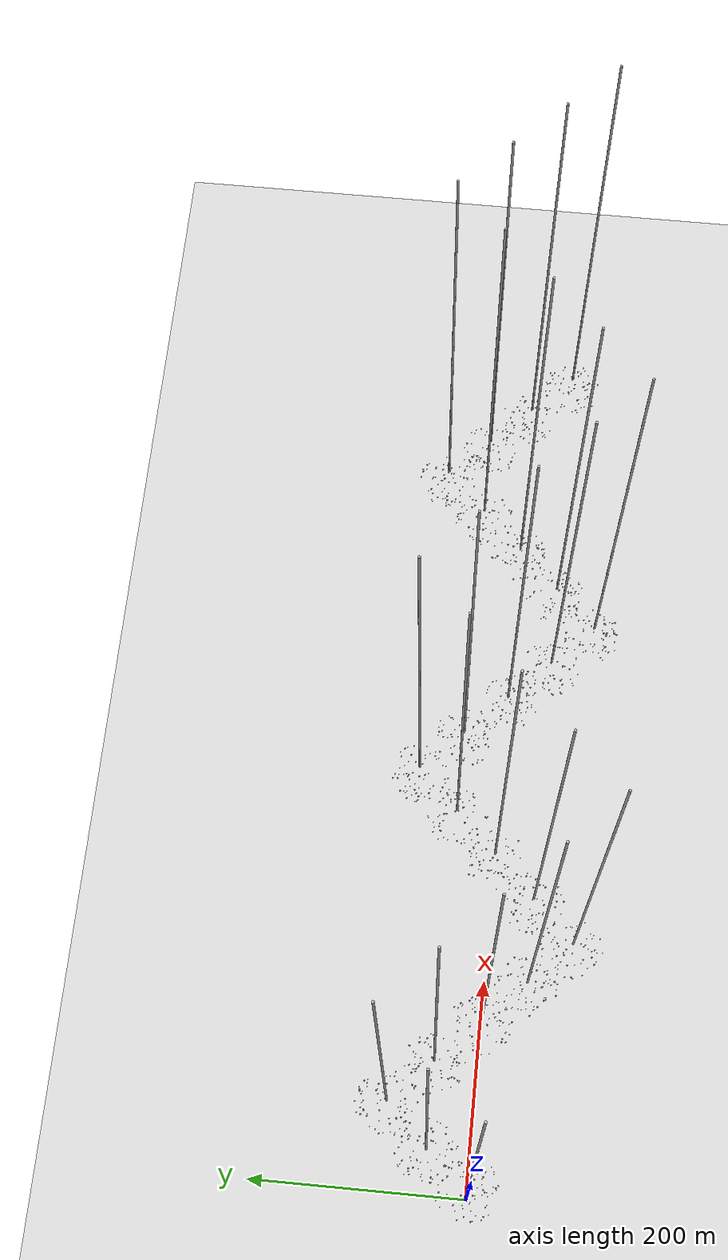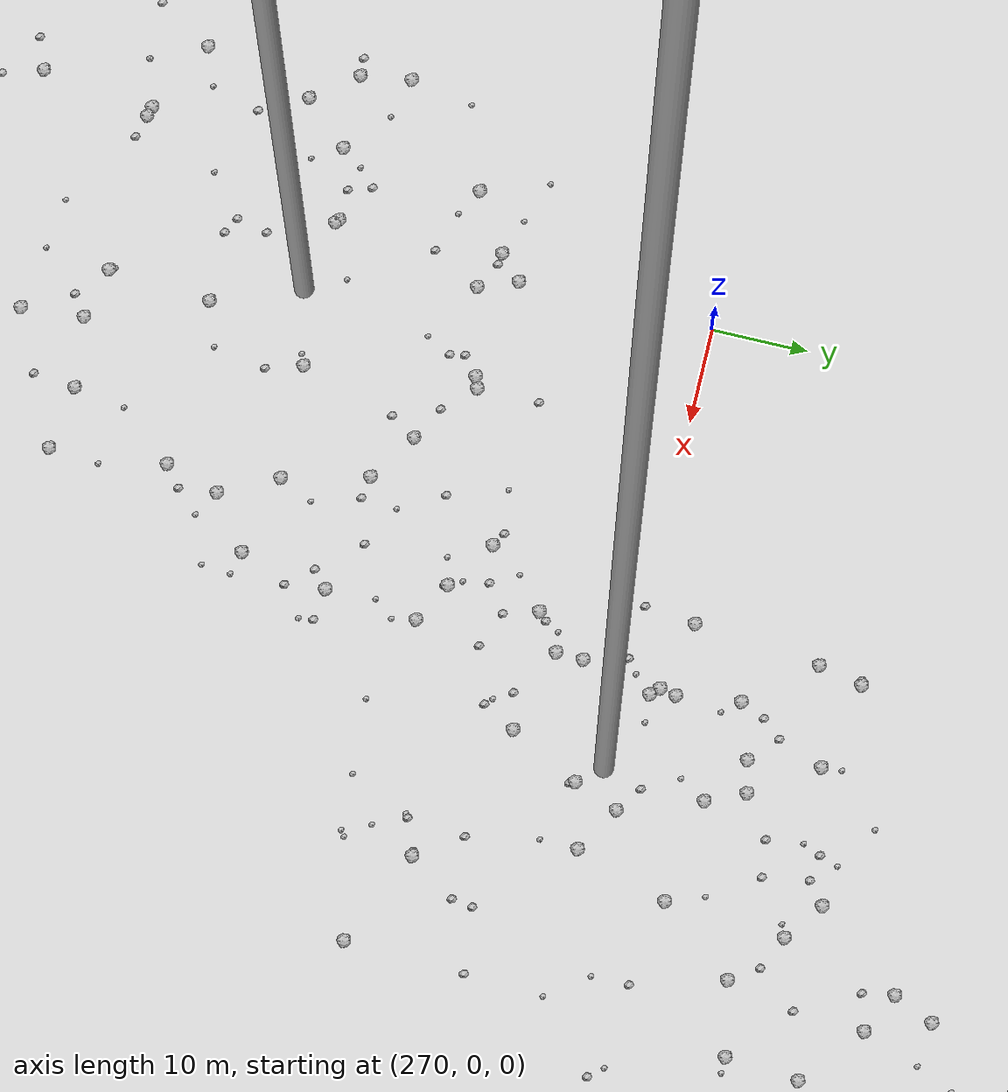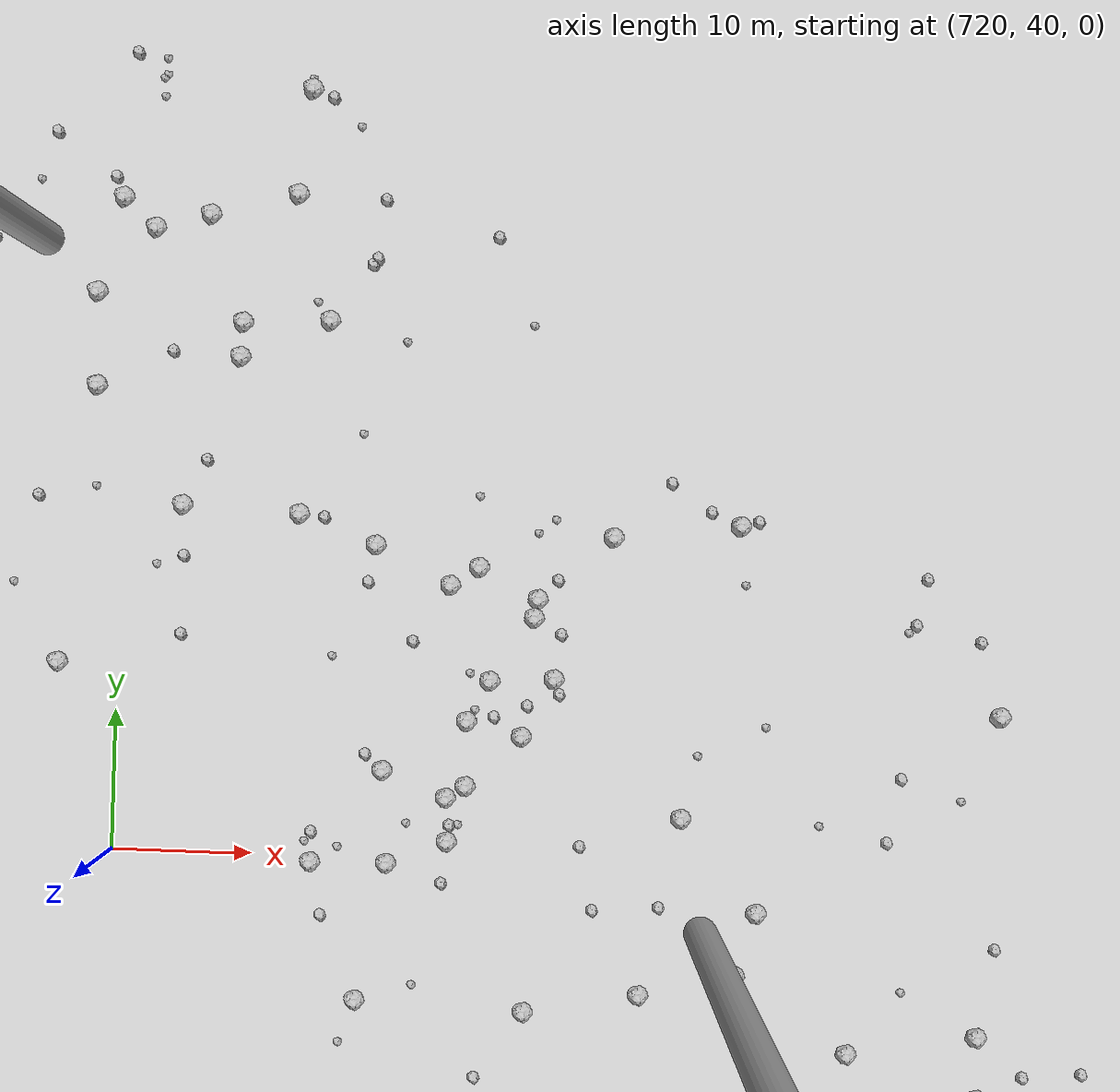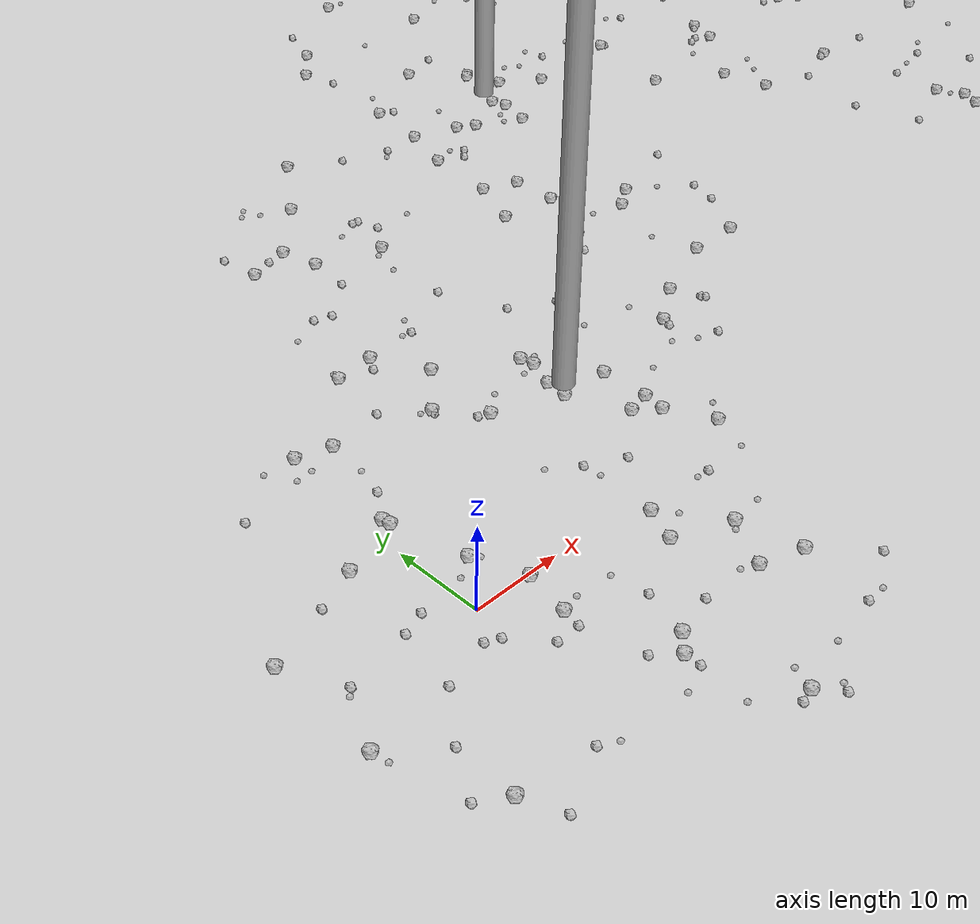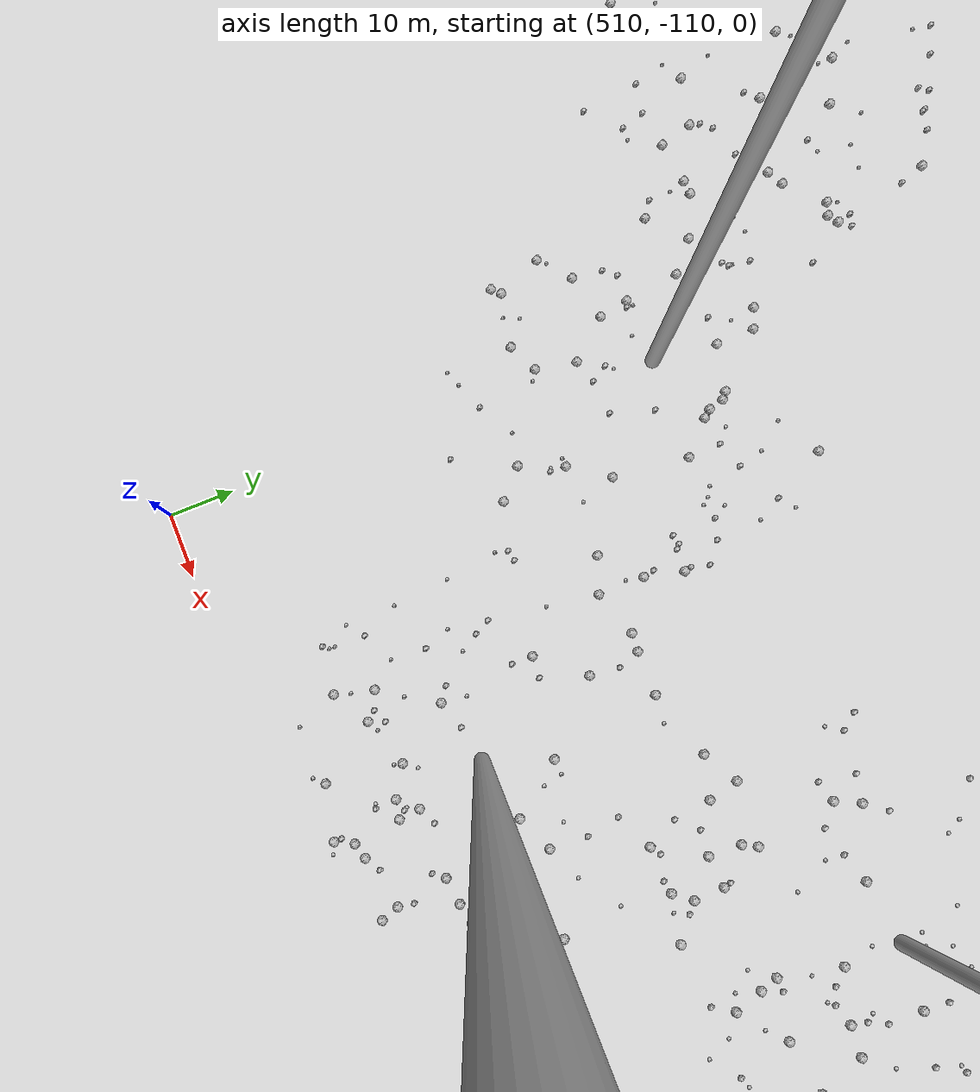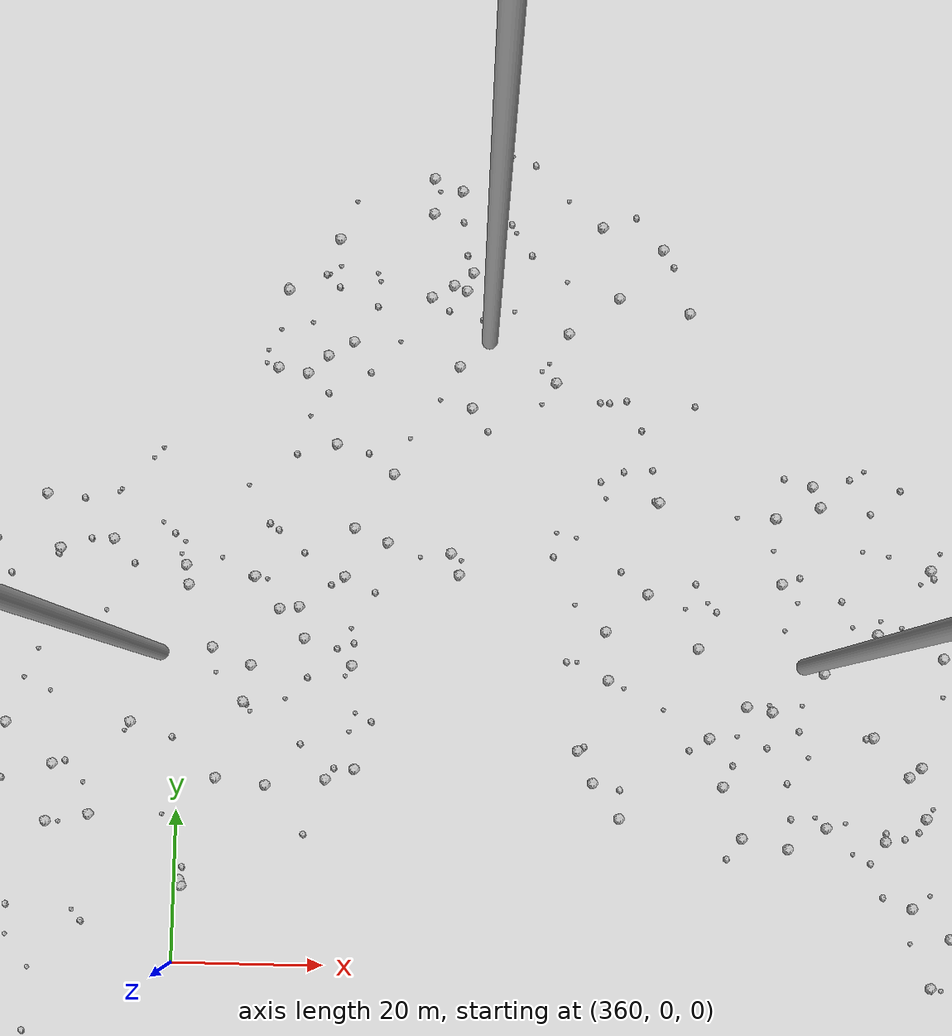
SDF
<sdf version="1.6">
 <world name="default">
  <include><uri>model://custom_ground</uri></include>
  <include><uri>model://sun</uri></include>
  <spherical_coordinates>
   <surface_model>EARTH_WGS84</surface_model>
   <latitude_deg>38.161479</latitude_deg>
   <longitude_deg>-122.454630</longitude_deg>
   <elevation>488.0</elevation>
   <heading_deg>90</heading_deg>
  </spherical_coordinates>
  <model name="rock1_0_0">
   <include><uri>model://rock1</uri><pose>10.76480044773539 -14.519050787894962 0.5 0 0 0</pose></include>
  </model>
  <model name="rock1_0_1">
   <include><uri>model://rock1</uri><pose>33.06195836401563 15.10946747772708 0.5 0 0 0</pose></include>
  </model>
  <model name="rock1_0_2">
   <include><uri>model://rock1</uri><pose>27.465079796704337 15.352225509414403 0.5 0 0 0</pose></include>
  </model>
  <model name="rock1_0_3">
   <include><uri>model://rock1</uri><pose>-17.648139051792754 -5.763978912970643 0.5 0 0 0</pose></include>
  </model>
  <model name="rock1_0_4">
   <include><uri>model://rock1</uri><pose>4.004186913027482 5.181848694438344 0.5 0 0 0</pose></include>
  </model>
  <model name="rock1_0_5">
   <include><uri>model://rock1</uri><pose>5.281465425138222 -5.597697707395589 0.5 0 0 0</pose></include>
  </model>
  <model name="rock1_0_6">
   <include><uri>model://rock1</uri><pose>25.256505618556943 -8.526130929072284 0.5 0 0 0</pose></include>
  </model>
  <model name="rock1_0_7">
   <include><uri>model://rock1</uri><pose>6.28953347170847 -0.4491067981379224 0.5 0 0 0</pose></include>
  </model>
  <model name="rock1_0_8">
   <include><uri>model://rock1</uri><pose>5.343381617421496 25.46748570395969 0.5 0 0 0</pose></include>
  </model>
  <model name="rock1_0_9">
   <include><uri>model://rock1</uri><pose>32.92392941730082 7.078824714255454 0.5 0 0 0</pose></include>
  </model>
  <model name="rock1_0_10">
   <include><uri>model://rock1</uri><pose>13.534564122198304 -26.355131266129057 0.5 0 0 0</pose></include>
  </model>
  <model name="rock1_0_11">
   <include><uri>model://rock1</uri><pose>28.892895212160617 21.10209977792256 0.5 0 0 0</pose></include>
  </model>
  <model name="rock1_0_12">
   <include><uri>model://rock1</uri><pose>26.906854882433116 -15.35020655182681 0.5 0 0 0</pose></include>
  </model>
  <model name="rock1_0_13">
   <include><uri>model://rock1</uri><pose>1.6873552517129617 14.263144841194027 0.5 0 0 0</pose></include>
  </model>
  <model name="rock1_0_14">
   <include><uri>model://rock1</uri><pose>1.8402296443715898 13.353641620052798 0.5 0 0 0</pose></include>
  </model>
  <model name="rock1_0_15">
   <include><uri>model://rock1</uri><pose>33.247907862744974 9.6299312936914 0.5 0 0 0</pose></include>
  </model>
  <model name="rock1_0_16">
   <include><uri>model://rock1</uri><pose>-17.293870249602538 6.8260220396823215 0.5 0 0 0</pose></include>
  </model>
  <model name="rock1_0_17">
   <include><uri>model://rock1</uri><pose>-5.006994627908041 11.18572720541487 0.5 0 0 0</pose></include>
  </model>
  <model name="rock1_0_18">
   <include><uri>model://rock1</uri><pose>20.605254216031817 27.73025578181509 0.5 0 0 0</pose></include>
  </model>
  <model name="rock1_0_19">
   <include><uri>model://rock1</uri><pose>35.592591728686536 2.0867974107488294 0.5 0 0 0</pose></include>
  </model>
  <model name="rock1_0_20">
   <include><uri>model://rock1</uri><pose>19.06015952909906 -5.9457298503283305 0.5 0 0 0</pose></include>
  </model>
  <model name="rock1_0_21">
   <include><uri>model://rock1</uri><pose>22.22339008630776 -13.81875291814626 0.5 0 0 0</pose></include>
  </model>
  <model name="rock1_0_22">
   <include><uri>model://rock1</uri><pose>-12.399637148103482 -17.038074408096627 0.5 0 0 0</pose></include>
  </model>
  <model name="rock1_0_23">
   <include><uri>model://rock1</uri><pose>8.929878219109668 -16.33080700918807 0.5 0 0 0</pose></include>
  </model>
  <model name="rock1_0_24">
   <include><uri>model://rock1</uri><pose>30.52635070297191 9.029674905241798 0.5 0 0 0</pose></include>
  </model>
  <model name="rock1_0_25">
   <include><uri>model://rock1</uri><pose>1.466350454593261 26.64638450726079 0.5 0 0 0</pose></include>
  </model>
  <model name="rock1_0_26">
   <include><uri>model://rock1</uri><pose>20.63441514956348 -2.219276297537011 0.5 0 0 0</pose></include>
  </model>
  <model name="rock2_0_0">
   <include><uri>model://rock2</uri><pose>3.9971496518919665 17.629929796145944 0.3 0 0 0</pose></include>
  </model>
  <model name="rock2_0_1">
   <include><uri>model://rock2</uri><pose>-9.9184758159727 9.434451177755406 0.3 0 0 0</pose></include>
  </model>
  <model name="rock2_0_2">
   <include><uri>model://rock2</uri><pose>15.504072479837944 -28.662854472520813 0.3 0 0 0</pose></include>
  </model>
  <model name="rock2_0_3">
   <include><uri>model://rock2</uri><pose>4.880004541024952 -7.658455418965254 0.3 0 0 0</pose></include>
  </model>
  <model name="rock2_0_4">
   <include><uri>model://rock2</uri><pose>15.426547392572083 -13.191846854689967 0.3 0 0 0</pose></include>
  </model>
  <model name="rock2_0_5">
   <include><uri>model://rock2</uri><pose>11.893351672653274 -26.722562229363408 0.3 0 0 0</pose></include>
  </model>
  <model name="rock2_0_6">
   <include><uri>model://rock2</uri><pose>6.594915837441679 -14.198509369171017 0.3 0 0 0</pose></include>
  </model>
  <model name="rock2_0_7">
   <include><uri>model://rock2</uri><pose>-15.414205866011317 -15.053569442249588 0.3 0 0 0</pose></include>
  </model>
  <model name="rock2_0_8">
   <include><uri>model://rock2</uri><pose>12.2201927708794 -9.313241756440128 0.3 0 0 0</pose></include>
  </model>
  <model name="rock2_0_9">
   <include><uri>model://rock2</uri><pose>24.881989781849512 4.536305210756673 0.3 0 0 0</pose></include>
  </model>
  <model name="rock2_0_10">
   <include><uri>model://rock2</uri><pose>-1.0045290857521252 -4.04800102653509 0.3 0 0 0</pose></include>
  </model>
  <model name="rock2_0_11">
   <include><uri>model://rock2</uri><pose>-12.317482771388931 -10.083883414678464 0.3 0 0 0</pose></include>
  </model>
  <model name="rock2_0_12">
   <include><uri>model://rock2</uri><pose>20.819505978926728 6.643690234724083 0.3 0 0 0</pose></include>
  </model>
  <model name="rock2_0_13">
   <include><uri>model://rock2</uri><pose>2.1493983516480526 -7.693854924969756 0.3 0 0 0</pose></include>
  </model>
  <model name="rock2_0_14">
   <include><uri>model://rock2</uri><pose>8.9254618442769 -18.097358367074136 0.3 0 0 0</pose></include>
  </model>
  <model name="rock2_0_15">
   <include><uri>model://rock2</uri><pose>-3.9452020760789672 3.0030816398988804 0.3 0 0 0</pose></include>
  </model>
  <model name="rock2_0_16">
   <include><uri>model://rock2</uri><pose>-7.726767510473442 22.91676300377741 0.3 0 0 0</pose></include>
  </model>
  <model name="rock2_0_17">
   <include><uri>model://rock2</uri><pose>-8.127993326845587 -4.919230912190159 0.3 0 0 0</pose></include>
  </model>
  <model name="rock2_0_18">
   <include><uri>model://rock2</uri><pose>11.803191258767363 26.402122513161125 0.3 0 0 0</pose></include>
  </model>
  <model name="rock2_0_19">
   <include><uri>model://rock2</uri><pose>-10.606624124302241 -21.25812503293311 0.3 0 0 0</pose></include>
  </model>
  <model name="rock2_0_20">
   <include><uri>model://rock2</uri><pose>25.601927659471542 -23.40298627604137 0.3 0 0 0</pose></include>
  </model>
  <model name="rock2_0_21">
   <include><uri>model://rock2</uri><pose>-2.5028324402574675 -3.3641615754239957 0.3 0 0 0</pose></include>
  </model>
  <model name="rock2_0_22">
   <include><uri>model://rock2</uri><pose>-14.159583992110766 0.7649787375658619 0.3 0 0 0</pose></include>
  </model>
  <model name="rock2_0_23">
   <include><uri>model://rock2</uri><pose>-6.669750528480234 2.0750016211739606 0.3 0 0 0</pose></include>
  </model>
  <model name="rock2_0_24">
   <include><uri>model://rock2</uri><pose>28.995577222422583 -2.1431506447855284 0.3 0 0 0</pose></include>
  </model>
  <model name="rock2_0_25">
   <include><uri>model://rock2</uri><pose>31.807285157436446 -20.520212351991603 0.3 0 0 0</pose></include>
  </model>
  <model name="rock2_0_26">
   <include><uri>model://rock2</uri><pose>-4.010760015110915 -17.96552164876872 0.3 0 0 0</pose></include>
  </model>
  <model name="rock3_0_0">
   <include><uri>model://rock3</uri><pose>19.730600775409997 -24.472040896494455 0.2 0 0 0</pose></include>
  </model>
  <model name="rock3_0_1">
   <include><uri>model://rock3</uri><pose>-0.3932560864076393 24.15078962738123 0.2 0 0 0</pose></include>
  </model>
  <model name="rock3_0_2">
   <include><uri>model://rock3</uri><pose>1.6611682361568896 3.7903401391874 0.2 0 0 0</pose></include>
  </model>
  <model name="rock3_0_3">
   <include><uri>model://rock3</uri><pose>-14.870930253772205 0.02851800202243382 0.2 0 0 0</pose></include>
  </model>
  <model name="rock3_0_4">
   <include><uri>model://rock3</uri><pose>4.876596891249193 4.504791862343524 0.2 0 0 0</pose></include>
  </model>
  <model name="rock3_0_5">
   <include><uri>model://rock3</uri><pose>7.491186232174179 -5.0129384632247636 0.2 0 0 0</pose></include>
  </model>
  <model name="rock3_0_6">
   <include><uri>model://rock3</uri><pose>-2.1803870333658466 27.014733961610276 0.2 0 0 0</pose></include>
  </model>
  <model name="rock3_0_7">
   <include><uri>model://rock3</uri><pose>27.573766047684437 -2.0397790989269566 0.2 0 0 0</pose></include>
  </model>
  <model name="rock3_0_8">
   <include><uri>model://rock3</uri><pose>16.134466904389953 -27.775506199466754 0.2 0 0 0</pose></include>
  </model>
  <model name="rock3_0_9">
   <include><uri>model://rock3</uri><pose>8.619025555847944 -23.47108161908018 0.2 0 0 0</pose></include>
  </model>
  <model name="rock3_0_10">
   <include><uri>model://rock3</uri><pose>24.424046558823626 -9.280820546685295 0.2 0 0 0</pose></include>
  </model>
  <model name="rock3_0_11">
   <include><uri>model://rock3</uri><pose>22.3488580247355 -4.1770004749165395 0.2 0 0 0</pose></include>
  </model>
  <model name="rock3_0_12">
   <include><uri>model://rock3</uri><pose>20.621678993557524 -12.939538160153255 0.2 0 0 0</pose></include>
  </model>
  <model name="rock3_0_13">
   <include><uri>model://rock3</uri><pose>27.890018504305118 -23.30987701527391 0.2 0 0 0</pose></include>
  </model>
  <model name="rock3_0_14">
   <include><uri>model://rock3</uri><pose>-2.1498530219526018 -18.963952273569454 0.2 0 0 0</pose></include>
  </model>
  <model name="rock3_0_15">
   <include><uri>model://rock3</uri><pose>21.058203051076276 4.580377338655403 0.2 0 0 0</pose></include>
  </model>
  <model name="rock3_0_16">
   <include><uri>model://rock3</uri><pose>29.148147397419834 -8.059175866725287 0.2 0 0 0</pose></include>
  </model>
  <model name="rock3_0_17">
   <include><uri>model://rock3</uri><pose>-17.2758885065772 -7.48752079326826 0.2 0 0 0</pose></include>
  </model>
  <model name="rock3_0_18">
   <include><uri>model://rock3</uri><pose>17.791202879629466 8.906493733353607 0.2 0 0 0</pose></include>
  </model>
  <model name="rock3_0_19">
   <include><uri>model://rock3</uri><pose>34.22754955201578 -1.9707237936352833 0.2 0 0 0</pose></include>
  </model>
  <model name="rock3_0_20">
   <include><uri>model://rock3</uri><pose>22.59857453408579 20.527271540526172 0.2 0 0 0</pose></include>
  </model>
  <model name="rock3_0_21">
   <include><uri>model://rock3</uri><pose>11.588501949492063 -5.347942433389171 0.2 0 0 0</pose></include>
  </model>
  <model name="rock3_0_22">
   <include><uri>model://rock3</uri><pose>14.520798038512133 -23.814647782868967 0.2 0 0 0</pose></include>
  </model>
  <model name="rock3_0_23">
   <include><uri>model://rock3</uri><pose>1.5594164474953587 24.300705168023583 0.2 0 0 0</pose></include>
  </model>
  <model name="rock3_0_24">
   <include><uri>model://rock3</uri><pose>37.41693978294529 4.308963089949216 0.2 0 0 0</pose></include>
  </model>
  <model name="rock3_0_25">
   <include><uri>model://rock3</uri><pose>4.986989977384695 20.968367051130997 0.2 0 0 0</pose></include>
  </model>
  <model name="rock3_0_26">
   <include><uri>model://rock3</uri><pose>5.838880975011861 -19.354950814915767 0.2 0 0 0</pose></include>
  </model>
  <model name="rock1_1_0">
   <include><uri>model://rock1</uri><pose>57.378788480999795 23.294818686975088 0.5 0 0 0</pose></include>
  </model>
  <model name="rock1_1_1">
   <include><uri>model://rock1</uri><pose>20.022966025373197 18.43863052207103 0.5 0 0 0</pose></include>
  </model>
  <model name="rock1_1_2">
   <include><uri>model://rock1</uri><pose>12.797822852528293 33.190283341780955 0.5 0 0 0</pose></include>
  </model>
  <model name="rock1_1_3">
   <include><uri>model://rock1</uri><pose>24.52077893004136 50.599845461594164 0.5 0 0 0</pose></include>
  </model>
  <model name="rock1_1_4">
   <include><uri>model://rock1</uri><pose>23.402529355569236 54.894052061806164 0.5 0 0 0</pose></include>
  </model>
  <model name="rock1_1_5">
   <include><uri>model://rock1</uri><pose>48.86560326380203 48.83055758115404 0.5 0 0 0</pose></include>
  </model>
  <model name="rock1_1_6">
   <include><uri>model://rock1</uri><pose>16.13342760163976 22.86489654056716 0.5 0 0 0</pose></include>
  </model>
  <model name="rock1_1_7">
   <include><uri>model://rock1</uri><pose>49.211931865534076 20.179589338759136 0.5 0 0 0</pose></include>
  </model>
  <model name="rock1_1_8">
   <include><uri>model://rock1</uri><pose>49.94641340954181 34.598255850640456 0.5 0 0 0</pose></include>
  </model>
  <model name="rock1_1_9">
   <include><uri>model://rock1</uri><pose>18.37689720098852 53.67638780786839 0.5 0 0 0</pose></include>
  </model>
  <model name="rock1_1_10">
   <include><uri>model://rock1</uri><pose>50.01779915934143 36.43532030344995 0.5 0 0 0</pose></include>
  </model>
  <model name="rock1_1_11">
   <include><uri>model://rock1</uri><pose>17.431840996080563 33.600140002116376 0.5 0 0 0</pose></include>
  </model>
  <model name="rock1_1_12">
   <include><uri>model://rock1</uri><pose>32.05814970401489 48.00491010268803 0.5 0 0 0</pose></include>
  </model>
  <model name="rock1_1_13">
   <include><uri>model://rock1</uri><pose>49.47664878180046 57.17823221710101 0.5 0 0 0</pose></include>
  </model>
  <model name="rock1_1_14">
   <include><uri>model://rock1</uri><pose>58.66233758839596 60.06114818152158 0.5 0 0 0</pose></include>
  </model>
  <model name="rock1_1_15">
   <include><uri>model://rock1</uri><pose>60.86925687247279 37.114379841354804 0.5 0 0 0</pose></include>
  </model>
  <model name="rock1_1_16">
   <include><uri>model://rock1</uri><pose>27.664618847020176 17.899455328614362 0.5 0 0 0</pose></include>
  </model>
  <model name="rock1_1_17">
   <include><uri>model://rock1</uri><pose>44.47045430174146 16.97571333149202 0.5 0 0 0</pose></include>
  </model>
  <model name="rock1_1_18">
   <include><uri>model://rock1</uri><pose>35.503155509312876 68.65586971971183 0.5 0 0 0</pose></include>
  </model>
  <model name="rock1_1_19">
   <include><uri>model://rock1</uri><pose>29.76406070473813 61.11688963657014 0.5 0 0 0</pose></include>
  </model>
  <model name="rock1_1_20">
   <include><uri>model://rock1</uri><pose>28.55274793760358 22.690332410208562 0.5 0 0 0</pose></include>
  </model>
  <model name="rock1_1_21">
   <include><uri>model://rock1</uri><pose>58.161888678389374 35.282468071192284 0.5 0 0 0</pose></include>
  </model>
  <model name="rock1_1_22">
   <include><uri>model://rock1</uri><pose>46.536840464769945 42.79788159753929 0.5 0 0 0</pose></include>
  </model>
  <model name="rock1_1_23">
   <include><uri>model://rock1</uri><pose>63.35164268474409 23.326755633022486 0.5 0 0 0</pose></include>
  </model>
  <model name="rock1_1_24">
   <include><uri>model://rock1</uri><pose>51.231465945710376 63.25731756936306 0.5 0 0 0</pose></include>
  </model>
  <model name="rock1_1_25">
   <include><uri>model://rock1</uri><pose>52.8671007423735 47.16044105159823 0.5 0 0 0</pose></include>
  </model>
  <model name="rock1_1_26">
   <include><uri>model://rock1</uri><pose>53.13477563622667 41.902979676178504 0.5 0 0 0</pose></include>
  </model>
  <model name="rock2_1_0">
   <include><uri>model://rock2</uri><pose>23.608136978368847 34.099284946050446 0.3 0 0 0</pose></include>
  </model>
  <model name="rock2_1_1">
   <include><uri>model://rock2</uri><pose>16.402413395069818 32.06934594063685 0.3 0 0 0</pose></include>
  </model>
  <model name="rock2_1_2">
   <include><uri>model://rock2</uri><pose>69.69822677788089 39.959663081938906 0.3 0 0 0</pose></include>
  </model>
  <model name="rock2_1_3">
   <include><uri>model://rock2</uri><pose>46.730944936918114 63.34379932663701 0.3 0 0 0</pose></include>
  </model>
  <model name="rock2_1_4">
   <include><uri>model://rock2</uri><pose>44.18057903233445 15.990425487177497 0.3 0 0 0</pose></include>
  </model>
  <model name="rock2_1_5">
   <include><uri>model://rock2</uri><pose>33.94167120639119 30.086740618517446 0.3 0 0 0</pose></include>
  </model>
  <model name="rock2_1_6">
   <include><uri>model://rock2</uri><pose>48.1366218768192 31.983788642591907 0.3 0 0 0</pose></include>
  </model>
  <model name="rock2_1_7">
   <include><uri>model://rock2</uri><pose>15.98297499485887 22.49724917346473 0.3 0 0 0</pose></include>
  </model>
  <model name="rock2_1_8">
   <include><uri>model://rock2</uri><pose>24.104576235526107 45.86286714229652 0.3 0 0 0</pose></include>
  </model>
  <model name="rock2_1_9">
   <include><uri>model://rock2</uri><pose>17.669121516394206 58.349437773049296 0.3 0 0 0</pose></include>
  </model>
  <model name="rock2_1_10">
   <include><uri>model://rock2</uri><pose>38.73331587629394 27.340412646496187 0.3 0 0 0</pose></include>
  </model>
  <model name="rock2_1_11">
   <include><uri>model://rock2</uri><pose>50.67889048591665 17.101137049008013 0.3 0 0 0</pose></include>
  </model>
  <model name="rock2_1_12">
   <include><uri>model://rock2</uri><pose>30.688051378701246 37.48822269406059 0.3 0 0 0</pose></include>
  </model>
  <model name="rock2_1_13">
   <include><uri>model://rock2</uri><pose>17.528289775569448 42.83557941390433 0.3 0 0 0</pose></include>
  </model>
  <model name="rock2_1_14">
   <include><uri>model://rock2</uri><pose>52.49973810069826 55.9197789283853 0.3 0 0 0</pose></include>
  </model>
  <model name="rock2_1_15">
   <include><uri>model://rock2</uri><pose>47.07555998873013 11.670178971453733 0.3 0 0 0</pose></include>
  </model>
  <model name="rock2_1_16">
   <include><uri>model://rock2</uri><pose>19.52705750498475 42.15727068673189 0.3 0 0 0</pose></include>
  </model>
  <model name="rock2_1_17">
   <include><uri>model://rock2</uri><pose>18.765896319405236 19.106541182941843 0.3 0 0 0</pose></include>
  </model>
  <model name="rock2_1_18">
   <include><uri>model://rock2</uri><pose>34.48011426159555 51.52967537644194 0.3 0 0 0</pose></include>
  </model>
  <model name="rock2_1_19">
   <include><uri>model://rock2</uri><pose>21.08748094716222 54.67427319031358 0.3 0 0 0</pose></include>
  </model>
  <model name="rock2_1_20">
   <include><uri>model://rock2</uri><pose>67.54627053620369 32.36814951608788 0.3 0 0 0</pose></include>
  </model>
  <model name="rock2_1_21">
   <include><uri>model://rock2</uri><pose>66.7436771543252 29.046105178701502 0.3 0 0 0</pose></include>
  </model>
  <model name="rock2_1_22">
   <include><uri>model://rock2</uri><pose>41.249988983032836 65.41160500356503 0.3 0 0 0</pose></include>
  </model>
  <model name="rock2_1_23">
   <include><uri>model://rock2</uri><pose>32.959000701786344 54.14554925088247 0.3 0 0 0</pose></include>
  </model>
  <model name="rock2_1_24">
   <include><uri>model://rock2</uri><pose>50.96979647540096 16.68309760730652 0.3 0 0 0</pose></include>
  </model>
  <model name="rock2_1_25">
   <include><uri>model://rock2</uri><pose>53.557267682543625 57.01374673852967 0.3 0 0 0</pose></include>
  </model>
  <model name="rock2_1_26">
   <include><uri>model://rock2</uri><pose>33.690933342337416 54.044183031417894 0.3 0 0 0</pose></include>
  </model>
  <model name="rock3_1_0">
   <include><uri>model://rock3</uri><pose>37.75709706072867 22.285872561661016 0.2 0 0 0</pose></include>
  </model>
  <model name="rock3_1_1">
   <include><uri>model://rock3</uri><pose>12.98109372360451 34.33324740585351 0.2 0 0 0</pose></include>
  </model>
  <model name="rock3_1_2">
   <include><uri>model://rock3</uri><pose>25.658068887403076 64.96437084886838 0.2 0 0 0</pose></include>
  </model>
  <model name="rock3_1_3">
   <include><uri>model://rock3</uri><pose>44.733656463890895 12.414819461636062 0.2 0 0 0</pose></include>
  </model>
  <model name="rock3_1_4">
   <include><uri>model://rock3</uri><pose>30.84691909113808 47.2650453477157 0.2 0 0 0</pose></include>
  </model>
  <model name="rock3_1_5">
   <include><uri>model://rock3</uri><pose>37.45166485226409 12.291613652348756 0.2 0 0 0</pose></include>
  </model>
  <model name="rock3_1_6">
   <include><uri>model://rock3</uri><pose>27.15038736995181 20.795833551145698 0.2 0 0 0</pose></include>
  </model>
  <model name="rock3_1_7">
   <include><uri>model://rock3</uri><pose>30.13478814812664 44.05795325720201 0.2 0 0 0</pose></include>
  </model>
  <model name="rock3_1_8">
   <include><uri>model://rock3</uri><pose>22.565931931803263 34.30279371240968 0.2 0 0 0</pose></include>
  </model>
  <model name="rock3_1_9">
   <include><uri>model://rock3</uri><pose>13.998737283772474 41.20873479569064 0.2 0 0 0</pose></include>
  </model>
  <model name="rock3_1_10">
   <include><uri>model://rock3</uri><pose>26.559959118764432 62.95344525613761 0.2 0 0 0</pose></include>
  </model>
  <model name="rock3_1_11">
   <include><uri>model://rock3</uri><pose>56.079175917458215 42.66873387313954 0.2 0 0 0</pose></include>
  </model>
  <model name="rock3_1_12">
   <include><uri>model://rock3</uri><pose>24.71630833526404 64.05398743052807 0.2 0 0 0</pose></include>
  </model>
  <model name="rock3_1_13">
   <include><uri>model://rock3</uri><pose>30.043079962173294 22.176061782004183 0.2 0 0 0</pose></include>
  </model>
  <model name="rock3_1_14">
   <include><uri>model://rock3</uri><pose>43.64777099016771 21.191511726008706 0.2 0 0 0</pose></include>
  </model>
  <model name="rock3_1_15">
   <include><uri>model://rock3</uri><pose>52.30840166638977 58.166370963413 0.2 0 0 0</pose></include>
  </model>
  <model name="rock3_1_16">
   <include><uri>model://rock3</uri><pose>55.74810944648189 28.566927082845204 0.2 0 0 0</pose></include>
  </model>
  <model name="rock3_1_17">
   <include><uri>model://rock3</uri><pose>62.07194877571349 58.61658969113597 0.2 0 0 0</pose></include>
  </model>
  <model name="rock3_1_18">
   <include><uri>model://rock3</uri><pose>45.76766977936281 62.39449951281227 0.2 0 0 0</pose></include>
  </model>
  <model name="rock3_1_19">
   <include><uri>model://rock3</uri><pose>54.4567958442992 36.45587516806242 0.2 0 0 0</pose></include>
  </model>
  <model name="rock3_1_20">
   <include><uri>model://rock3</uri><pose>38.97101191947252 51.4242997962583 0.2 0 0 0</pose></include>
  </model>
  <model name="rock3_1_21">
   <include><uri>model://rock3</uri><pose>30.40408087681236 53.016718002557056 0.2 0 0 0</pose></include>
  </model>
  <model name="rock3_1_22">
   <include><uri>model://rock3</uri><pose>49.272226860562284 56.90746068617608 0.2 0 0 0</pose></include>
  </model>
  <model name="rock3_1_23">
   <include><uri>model://rock3</uri><pose>42.30425207796713 13.932816644564898 0.2 0 0 0</pose></include>
  </model>
  <model name="rock3_1_24">
   <include><uri>model://rock3</uri><pose>15.04303664903757 23.440242345181208 0.2 0 0 0</pose></include>
  </model>
  <model name="rock3_1_25">
   <include><uri>model://rock3</uri><pose>24.587093839740383 36.21594741491204 0.2 0 0 0</pose></include>
  </model>
  <model name="rock3_1_26">
   <include><uri>model://rock3</uri><pose>64.257665843738 35.246666284536246 0.2 0 0 0</pose></include>
  </model>
  <model name="rock1_2_0">
   <include><uri>model://rock1</uri><pose>67.63768917966073 103.38919374291635 0.5 0 0 0</pose></include>
  </model>
  <model name="rock1_2_1">
   <include><uri>model://rock1</uri><pose>98.28279311148887 102.93554309418758 0.5 0 0 0</pose></include>
  </model>
  <model name="rock1_2_2">
   <include><uri>model://rock1</uri><pose>64.88824356422573 61.0650426080679 0.5 0 0 0</pose></include>
  </model>
  <model name="rock1_2_3">
   <include><uri>model://rock1</uri><pose>68.47422572177209 65.8030780841801 0.5 0 0 0</pose></include>
  </model>
  <model name="rock1_2_4">
   <include><uri>model://rock1</uri><pose>72.5599564599417 86.3850191941437 0.5 0 0 0</pose></include>
  </model>
  <model name="rock1_2_5">
   <include><uri>model://rock1</uri><pose>71.25920010330438 100.89143743546944 0.5 0 0 0</pose></include>
  </model>
  <model name="rock1_2_6">
   <include><uri>model://rock1</uri><pose>83.28733109999648 52.116786220218806 0.5 0 0 0</pose></include>
  </model>
  <model name="rock1_2_7">
   <include><uri>model://rock1</uri><pose>89.90470049171464 106.761359447626 0.5 0 0 0</pose></include>
  </model>
  <model name="rock1_2_8">
   <include><uri>model://rock1</uri><pose>96.67609879948026 89.29960727534419 0.5 0 0 0</pose></include>
  </model>
  <model name="rock1_2_9">
   <include><uri>model://rock1</uri><pose>72.97775893248621 62.62654497352436 0.5 0 0 0</pose></include>
  </model>
  <model name="rock1_2_10">
   <include><uri>model://rock1</uri><pose>64.32919731772705 62.87934123995814 0.5 0 0 0</pose></include>
  </model>
  <model name="rock1_2_11">
   <include><uri>model://rock1</uri><pose>85.29854743782465 63.603941321473755 0.5 0 0 0</pose></include>
  </model>
  <model name="rock1_2_12">
   <include><uri>model://rock1</uri><pose>69.02691437516009 107.40103705864578 0.5 0 0 0</pose></include>
  </model>
  <model name="rock1_2_13">
   <include><uri>model://rock1</uri><pose>90.48894558048002 91.04034337681712 0.5 0 0 0</pose></include>
  </model>
  <model name="rock1_2_14">
   <include><uri>model://rock1</uri><pose>98.62304972642252 58.590619441485714 0.5 0 0 0</pose></include>
  </model>
  <model name="rock1_2_15">
   <include><uri>model://rock1</uri><pose>88.52226340627311 106.09766097771907 0.5 0 0 0</pose></include>
  </model>
  <model name="rock1_2_16">
   <include><uri>model://rock1</uri><pose>66.43995683246912 97.091029750629 0.5 0 0 0</pose></include>
  </model>
  <model name="rock1_2_17">
   <include><uri>model://rock1</uri><pose>55.326543634480075 88.52631048883067 0.5 0 0 0</pose></include>
  </model>
  <model name="rock1_2_18">
   <include><uri>model://rock1</uri><pose>66.9744017098374 70.18007602923949 0.5 0 0 0</pose></include>
  </model>
  <model name="rock1_2_19">
   <include><uri>model://rock1</uri><pose>52.00519489173099 70.54813028731982 0.5 0 0 0</pose></include>
  </model>
  <model name="rock1_2_20">
   <include><uri>model://rock1</uri><pose>66.50638275272425 69.77805284298256 0.5 0 0 0</pose></include>
  </model>
  <model name="rock1_2_21">
   <include><uri>model://rock1</uri><pose>97.45386261488406 81.75606797198847 0.5 0 0 0</pose></include>
  </model>
  <model name="rock1_2_22">
   <include><uri>model://rock1</uri><pose>100.24240222824864 72.99566938689011 0.5 0 0 0</pose></include>
  </model>
  <model name="rock1_2_23">
   <include><uri>model://rock1</uri><pose>56.556043101009095 61.296857154736486 0.5 0 0 0</pose></include>
  </model>
  <model name="rock1_2_24">
   <include><uri>model://rock1</uri><pose>63.987585636551074 57.24721471335096 0.5 0 0 0</pose></include>
  </model>
  <model name="rock1_2_25">
   <include><uri>model://rock1</uri><pose>61.519686152352136 75.41228699119509 0.5 0 0 0</pose></include>
  </model>
  <model name="rock1_2_26">
   <include><uri>model://rock1</uri><pose>51.816703430688285 84.54316705320429 0.5 0 0 0</pose></include>
  </model>
  <model name="rock2_2_0">
   <include><uri>model://rock2</uri><pose>86.14055572451348 104.74313425462017 0.3 0 0 0</pose></include>
  </model>
  <model name="rock2_2_1">
   <include><uri>model://rock2</uri><pose>73.81011803961066 104.16864194061378 0.3 0 0 0</pose></include>
  </model>
  <model name="rock2_2_2">
   <include><uri>model://rock2</uri><pose>95.74799498005814 100.1409821736182 0.3 0 0 0</pose></include>
  </model>
  <model name="rock2_2_3">
   <include><uri>model://rock2</uri><pose>72.70750968523971 101.5076385645085 0.3 0 0 0</pose></include>
  </model>
  <model name="rock2_2_4">
   <include><uri>model://rock2</uri><pose>89.70135421296658 84.50027161988972 0.3 0 0 0</pose></include>
  </model>
  <model name="rock2_2_5">
   <include><uri>model://rock2</uri><pose>106.36572785150224 85.37783278365316 0.3 0 0 0</pose></include>
  </model>
  <model name="rock2_2_6">
   <include><uri>model://rock2</uri><pose>92.01268133747135 107.3301286718793 0.3 0 0 0</pose></include>
  </model>
  <model name="rock2_2_7">
   <include><uri>model://rock2</uri><pose>93.30871167778136 67.30007939499333 0.3 0 0 0</pose></include>
  </model>
  <model name="rock2_2_8">
   <include><uri>model://rock2</uri><pose>101.97433859591143 67.29255866285283 0.3 0 0 0</pose></include>
  </model>
  <model name="rock2_2_9">
   <include><uri>model://rock2</uri><pose>53.660872229435626 69.88271266982132 0.3 0 0 0</pose></include>
  </model>
  <model name="rock2_2_10">
   <include><uri>model://rock2</uri><pose>57.22495338062893 93.96042901257425 0.3 0 0 0</pose></include>
  </model>
  <model name="rock2_2_11">
   <include><uri>model://rock2</uri><pose>96.34802007479527 100.04642692976046 0.3 0 0 0</pose></include>
  </model>
  <model name="rock2_2_12">
   <include><uri>model://rock2</uri><pose>79.14175320049713 109.89087124036266 0.3 0 0 0</pose></include>
  </model>
  <model name="rock2_2_13">
   <include><uri>model://rock2</uri><pose>77.60925570939457 67.03583147590207 0.3 0 0 0</pose></include>
  </model>
  <model name="rock2_2_14">
   <include><uri>model://rock2</uri><pose>82.20520812328235 86.26183047684738 0.3 0 0 0</pose></include>
  </model>
  <model name="rock2_2_15">
   <include><uri>model://rock2</uri><pose>52.956611783184854 80.67201114806473 0.3 0 0 0</pose></include>
  </model>
  <model name="rock2_2_16">
   <include><uri>model://rock2</uri><pose>66.18087921292386 76.82584826873563 0.3 0 0 0</pose></include>
  </model>
  <model name="rock2_2_17">
   <include><uri>model://rock2</uri><pose>98.0842436139532 58.28035808223591 0.3 0 0 0</pose></include>
  </model>
  <model name="rock2_2_18">
   <include><uri>model://rock2</uri><pose>77.89828326650485 103.6232776536063 0.3 0 0 0</pose></include>
  </model>
  <model name="rock2_2_19">
   <include><uri>model://rock2</uri><pose>80.56398360977057 63.27302958912852 0.3 0 0 0</pose></include>
  </model>
  <model name="rock2_2_20">
   <include><uri>model://rock2</uri><pose>87.64330295392698 89.37814886829051 0.3 0 0 0</pose></include>
  </model>
  <model name="rock2_2_21">
   <include><uri>model://rock2</uri><pose>80.12839146401683 102.2508483798587 0.3 0 0 0</pose></include>
  </model>
  <model name="rock2_2_22">
   <include><uri>model://rock2</uri><pose>85.82657021836268 63.45286318113809 0.3 0 0 0</pose></include>
  </model>
  <model name="rock2_2_23">
   <include><uri>model://rock2</uri><pose>104.70692611066438 75.50766988072252 0.3 0 0 0</pose></include>
  </model>
  <model name="rock2_2_24">
   <include><uri>model://rock2</uri><pose>93.18791189708148 99.99225882110093 0.3 0 0 0</pose></include>
  </model>
  <model name="rock2_2_25">
   <include><uri>model://rock2</uri><pose>92.04421648710698 90.20590371569287 0.3 0 0 0</pose></include>
  </model>
  <model name="rock2_2_26">
   <include><uri>model://rock2</uri><pose>109.02528198692465 74.67743247531322 0.3 0 0 0</pose></include>
  </model>
  <model name="rock3_2_0">
   <include><uri>model://rock3</uri><pose>93.54234490530922 98.06276234602238 0.2 0 0 0</pose></include>
  </model>
  <model name="rock3_2_1">
   <include><uri>model://rock3</uri><pose>84.04229561650624 82.50576821649629 0.2 0 0 0</pose></include>
  </model>
  <model name="rock3_2_2">
   <include><uri>model://rock3</uri><pose>99.58840747484956 100.0457069990067 0.2 0 0 0</pose></include>
  </model>
  <model name="rock3_2_3">
   <include><uri>model://rock3</uri><pose>103.94510140614685 83.03124220074581 0.2 0 0 0</pose></include>
  </model>
  <model name="rock3_2_4">
   <include><uri>model://rock3</uri><pose>92.7109085019394 53.814241144200075 0.2 0 0 0</pose></include>
  </model>
  <model name="rock3_2_5">
   <include><uri>model://rock3</uri><pose>77.0223048470291 69.59337173337738 0.2 0 0 0</pose></include>
  </model>
  <model name="rock3_2_6">
   <include><uri>model://rock3</uri><pose>98.26741486530653 88.04401489862312 0.2 0 0 0</pose></include>
  </model>
  <model name="rock3_2_7">
   <include><uri>model://rock3</uri><pose>87.37464251640253 88.78049195981876 0.2 0 0 0</pose></include>
  </model>
  <model name="rock3_2_8">
   <include><uri>model://rock3</uri><pose>68.67044630101987 97.26573144781688 0.2 0 0 0</pose></include>
  </model>
  <model name="rock3_2_9">
   <include><uri>model://rock3</uri><pose>82.93313202556772 67.91034716702691 0.2 0 0 0</pose></include>
  </model>
  <model name="rock3_2_10">
   <include><uri>model://rock3</uri><pose>74.48865333160995 56.439318882312804 0.2 0 0 0</pose></include>
  </model>
  <model name="rock3_2_11">
   <include><uri>model://rock3</uri><pose>98.53071833998479 58.72242355557457 0.2 0 0 0</pose></include>
  </model>
  <model name="rock3_2_12">
   <include><uri>model://rock3</uri><pose>76.0937932062271 98.49721823108925 0.2 0 0 0</pose></include>
  </model>
  <model name="rock3_2_13">
   <include><uri>model://rock3</uri><pose>78.58672737520723 88.83516458198098 0.2 0 0 0</pose></include>
  </model>
  <model name="rock3_2_14">
   <include><uri>model://rock3</uri><pose>104.55070337115376 79.76570493604521 0.2 0 0 0</pose></include>
  </model>
  <model name="rock3_2_15">
   <include><uri>model://rock3</uri><pose>62.91154164846319 85.68272714365776 0.2 0 0 0</pose></include>
  </model>
  <model name="rock3_2_16">
   <include><uri>model://rock3</uri><pose>71.94541424813457 68.42230836173371 0.2 0 0 0</pose></include>
  </model>
  <model name="rock3_2_17">
   <include><uri>model://rock3</uri><pose>73.68450244427568 67.43264393916391 0.2 0 0 0</pose></include>
  </model>
  <model name="rock3_2_18">
   <include><uri>model://rock3</uri><pose>77.35693854526123 93.22596668893905 0.2 0 0 0</pose></include>
  </model>
  <model name="rock3_2_19">
   <include><uri>model://rock3</uri><pose>62.8991080583722 60.08832653699543 0.2 0 0 0</pose></include>
  </model>
  <model name="rock3_2_20">
   <include><uri>model://rock3</uri><pose>57.970896902631296 66.116469277678 0.2 0 0 0</pose></include>
  </model>
  <model name="rock3_2_21">
   <include><uri>model://rock3</uri><pose>105.2620676263904 86.093690188382 0.2 0 0 0</pose></include>
  </model>
  <model name="rock3_2_22">
   <include><uri>model://rock3</uri><pose>54.14626821356039 74.34468361163692 0.2 0 0 0</pose></include>
  </model>
  <model name="rock3_2_23">
   <include><uri>model://rock3</uri><pose>101.93424247615198 82.49800478124034 0.2 0 0 0</pose></include>
  </model>
  <model name="rock3_2_24">
   <include><uri>model://rock3</uri><pose>91.74842250997276 68.58113984200963 0.2 0 0 0</pose></include>
  </model>
  <model name="rock3_2_25">
   <include><uri>model://rock3</uri><pose>76.32531276528141 61.02656184134837 0.2 0 0 0</pose></include>
  </model>
  <model name="rock3_2_26">
   <include><uri>model://rock3</uri><pose>88.31947098342698 103.69710174657303 0.2 0 0 0</pose></include>
  </model>
  <model name="rock1_3_0">
   <include><uri>model://rock1</uri><pose>132.9951700592228 28.12306532577484 0.5 0 0 0</pose></include>
  </model>
  <model name="rock1_3_1">
   <include><uri>model://rock1</uri><pose>108.20988801502553 20.210191758917013 0.5 0 0 0</pose></include>
  </model>
  <model name="rock1_3_2">
   <include><uri>model://rock1</uri><pose>138.36796826322455 50.20124138705637 0.5 0 0 0</pose></include>
  </model>
  <model name="rock1_3_3">
   <include><uri>model://rock1</uri><pose>129.3753471531715 19.719888787328358 0.5 0 0 0</pose></include>
  </model>
  <model name="rock1_3_4">
   <include><uri>model://rock1</uri><pose>115.86219598260871 54.113229105819784 0.5 0 0 0</pose></include>
  </model>
  <model name="rock1_3_5">
   <include><uri>model://rock1</uri><pose>142.38291169093293 55.554942310428416 0.5 0 0 0</pose></include>
  </model>
  <model name="rock1_3_6">
   <include><uri>model://rock1</uri><pose>107.33610456420081 25.550706230944545 0.5 0 0 0</pose></include>
  </model>
  <model name="rock1_3_7">
   <include><uri>model://rock1</uri><pose>122.85838947158311 19.20588618111371 0.5 0 0 0</pose></include>
  </model>
  <model name="rock1_3_8">
   <include><uri>model://rock1</uri><pose>104.94201228038979 41.60040087559999 0.5 0 0 0</pose></include>
  </model>
  <model name="rock1_3_9">
   <include><uri>model://rock1</uri><pose>119.3589104034695 23.325543127696683 0.5 0 0 0</pose></include>
  </model>
  <model name="rock1_3_10">
   <include><uri>model://rock1</uri><pose>128.68592458258362 60.27230351734641 0.5 0 0 0</pose></include>
  </model>
  <model name="rock1_3_11">
   <include><uri>model://rock1</uri><pose>132.92213063699506 16.152752465891425 0.5 0 0 0</pose></include>
  </model>
  <model name="rock1_3_12">
   <include><uri>model://rock1</uri><pose>92.61272440390245 41.47448767947513 0.5 0 0 0</pose></include>
  </model>
  <model name="rock1_3_13">
   <include><uri>model://rock1</uri><pose>125.74625838248369 21.626330486538656 0.5 0 0 0</pose></include>
  </model>
  <model name="rock1_3_14">
   <include><uri>model://rock1</uri><pose>106.28506879995751 17.00444665047813 0.5 0 0 0</pose></include>
  </model>
  <model name="rock1_3_15">
   <include><uri>model://rock1</uri><pose>113.48659792831282 55.93146205936026 0.5 0 0 0</pose></include>
  </model>
  <model name="rock1_3_16">
   <include><uri>model://rock1</uri><pose>109.6392149620968 60.4196309079801 0.5 0 0 0</pose></include>
  </model>
  <model name="rock1_3_17">
   <include><uri>model://rock1</uri><pose>134.63650974053667 65.10846869067895 0.5 0 0 0</pose></include>
  </model>
  <model name="rock1_3_18">
   <include><uri>model://rock1</uri><pose>116.63978827311664 62.98040071002703 0.5 0 0 0</pose></include>
  </model>
  <model name="rock1_3_19">
   <include><uri>model://rock1</uri><pose>138.0450360713851 55.495963318746476 0.5 0 0 0</pose></include>
  </model>
  <model name="rock1_3_20">
   <include><uri>model://rock1</uri><pose>125.1398947524901 42.28935780606908 0.5 0 0 0</pose></include>
  </model>
  <model name="rock1_3_21">
   <include><uri>model://rock1</uri><pose>97.70963179400687 55.102172828244896 0.5 0 0 0</pose></include>
  </model>
  <model name="rock1_3_22">
   <include><uri>model://rock1</uri><pose>134.7695418553997 44.5130793001193 0.5 0 0 0</pose></include>
  </model>
  <model name="rock1_3_23">
   <include><uri>model://rock1</uri><pose>91.11566164977383 47.16176941562515 0.5 0 0 0</pose></include>
  </model>
  <model name="rock1_3_24">
   <include><uri>model://rock1</uri><pose>109.04662371725792 22.46303856008039 0.5 0 0 0</pose></include>
  </model>
  <model name="rock1_3_25">
   <include><uri>model://rock1</uri><pose>142.4575020555102 48.42941659994094 0.5 0 0 0</pose></include>
  </model>
  <model name="rock1_3_26">
   <include><uri>model://rock1</uri><pose>122.39543016845383 16.83723810028569 0.5 0 0 0</pose></include>
  </model>
  <model name="rock2_3_0">
   <include><uri>model://rock2</uri><pose>94.9460722787821 56.03086665122346 0.3 0 0 0</pose></include>
  </model>
  <model name="rock2_3_1">
   <include><uri>model://rock2</uri><pose>137.2886168040596 48.79009893796672 0.3 0 0 0</pose></include>
  </model>
  <model name="rock2_3_2">
   <include><uri>model://rock2</uri><pose>104.44962145825104 15.559427173424433 0.3 0 0 0</pose></include>
  </model>
  <model name="rock2_3_3">
   <include><uri>model://rock2</uri><pose>116.08653310529141 23.746584541574208 0.3 0 0 0</pose></include>
  </model>
  <model name="rock2_3_4">
   <include><uri>model://rock2</uri><pose>123.32153030881754 11.48794462200592 0.3 0 0 0</pose></include>
  </model>
  <model name="rock2_3_5">
   <include><uri>model://rock2</uri><pose>132.86491852744538 41.20461943891486 0.3 0 0 0</pose></include>
  </model>
  <model name="rock2_3_6">
   <include><uri>model://rock2</uri><pose>127.41163748752902 58.14819217407236 0.3 0 0 0</pose></include>
  </model>
  <model name="rock2_3_7">
   <include><uri>model://rock2</uri><pose>142.31953170373322 22.683445331865002 0.3 0 0 0</pose></include>
  </model>
  <model name="rock2_3_8">
   <include><uri>model://rock2</uri><pose>99.4968989008538 22.808583854897755 0.3 0 0 0</pose></include>
  </model>
  <model name="rock2_3_9">
   <include><uri>model://rock2</uri><pose>111.18330910759846 56.76284892158159 0.3 0 0 0</pose></include>
  </model>
  <model name="rock2_3_10">
   <include><uri>model://rock2</uri><pose>117.8262070426816 27.579585747956447 0.3 0 0 0</pose></include>
  </model>
  <model name="rock2_3_11">
   <include><uri>model://rock2</uri><pose>104.12081754257467 41.534016860028785 0.3 0 0 0</pose></include>
  </model>
  <model name="rock2_3_12">
   <include><uri>model://rock2</uri><pose>112.08231495467857 41.181224111050184 0.3 0 0 0</pose></include>
  </model>
  <model name="rock2_3_13">
   <include><uri>model://rock2</uri><pose>123.81138764204965 52.78772389736837 0.3 0 0 0</pose></include>
  </model>
  <model name="rock2_3_14">
   <include><uri>model://rock2</uri><pose>134.03173735303903 64.21795195733155 0.3 0 0 0</pose></include>
  </model>
  <model name="rock2_3_15">
   <include><uri>model://rock2</uri><pose>118.84250238033057 52.867881682934005 0.3 0 0 0</pose></include>
  </model>
  <model name="rock2_3_16">
   <include><uri>model://rock2</uri><pose>146.04789646370077 43.19206387504565 0.3 0 0 0</pose></include>
  </model>
  <model name="rock2_3_17">
   <include><uri>model://rock2</uri><pose>107.567514493389 31.84489212631764 0.3 0 0 0</pose></include>
  </model>
  <model name="rock2_3_18">
   <include><uri>model://rock2</uri><pose>106.40074191538648 15.10989277649957 0.3 0 0 0</pose></include>
  </model>
  <model name="rock2_3_19">
   <include><uri>model://rock2</uri><pose>142.99329081252395 49.155429921020314 0.3 0 0 0</pose></include>
  </model>
  <model name="rock2_3_20">
   <include><uri>model://rock2</uri><pose>96.10042910164566 56.38832740341926 0.3 0 0 0</pose></include>
  </model>
  <model name="rock2_3_21">
   <include><uri>model://rock2</uri><pose>98.60690002811201 39.34755511139189 0.3 0 0 0</pose></include>
  </model>
  <model name="rock2_3_22">
   <include><uri>model://rock2</uri><pose>96.72867145428377 30.445557747633593 0.3 0 0 0</pose></include>
  </model>
  <model name="rock2_3_23">
   <include><uri>model://rock2</uri><pose>133.16579581147943 28.23336761164818 0.3 0 0 0</pose></include>
  </model>
  <model name="rock2_3_24">
   <include><uri>model://rock2</uri><pose>114.03385306710115 33.20361712111943 0.3 0 0 0</pose></include>
  </model>
  <model name="rock2_3_25">
   <include><uri>model://rock2</uri><pose>122.75096754672381 22.509432885382736 0.3 0 0 0</pose></include>
  </model>
  <model name="rock2_3_26">
   <include><uri>model://rock2</uri><pose>124.41626142793667 58.44304753681459 0.3 0 0 0</pose></include>
  </model>
  <model name="rock3_3_0">
   <include><uri>model://rock3</uri><pose>116.7296910884007 34.94792814676073 0.2 0 0 0</pose></include>
  </model>
  <model name="rock3_3_1">
   <include><uri>model://rock3</uri><pose>112.8280217862665 59.50741630274121 0.2 0 0 0</pose></include>
  </model>
  <model name="rock3_3_2">
   <include><uri>model://rock3</uri><pose>126.69707168212645 66.08524967364909 0.2 0 0 0</pose></include>
  </model>
  <model name="rock3_3_3">
   <include><uri>model://rock3</uri><pose>127.3967557007451 25.076619117013127 0.2 0 0 0</pose></include>
  </model>
  <model name="rock3_3_4">
   <include><uri>model://rock3</uri><pose>127.02282329147192 18.823629174392046 0.2 0 0 0</pose></include>
  </model>
  <model name="rock3_3_5">
   <include><uri>model://rock3</uri><pose>122.88279210897323 52.52202571424566 0.2 0 0 0</pose></include>
  </model>
  <model name="rock3_3_6">
   <include><uri>model://rock3</uri><pose>112.0507237485787 65.79403698547947 0.2 0 0 0</pose></include>
  </model>
  <model name="rock3_3_7">
   <include><uri>model://rock3</uri><pose>122.51447202627259 63.17290990581998 0.2 0 0 0</pose></include>
  </model>
  <model name="rock3_3_8">
   <include><uri>model://rock3</uri><pose>117.63529376975525 57.862983962259094 0.2 0 0 0</pose></include>
  </model>
  <model name="rock3_3_9">
   <include><uri>model://rock3</uri><pose>115.22123737008877 67.23837960931314 0.2 0 0 0</pose></include>
  </model>
  <model name="rock3_3_10">
   <include><uri>model://rock3</uri><pose>112.9943365895343 57.78337187745256 0.2 0 0 0</pose></include>
  </model>
  <model name="rock3_3_11">
   <include><uri>model://rock3</uri><pose>120.52096314711372 50.284766463040185 0.2 0 0 0</pose></include>
  </model>
  <model name="rock3_3_12">
   <include><uri>model://rock3</uri><pose>138.9689075975237 20.153447431458183 0.2 0 0 0</pose></include>
  </model>
  <model name="rock3_3_13">
   <include><uri>model://rock3</uri><pose>146.8560022851925 45.67762072097271 0.2 0 0 0</pose></include>
  </model>
  <model name="rock3_3_14">
   <include><uri>model://rock3</uri><pose>138.81817132194865 54.22194434424013 0.2 0 0 0</pose></include>
  </model>
  <model name="rock3_3_15">
   <include><uri>model://rock3</uri><pose>124.19186980319807 35.238803876237085 0.2 0 0 0</pose></include>
  </model>
  <model name="rock3_3_16">
   <include><uri>model://rock3</uri><pose>146.68526530187034 27.660578995312342 0.2 0 0 0</pose></include>
  </model>
  <model name="rock3_3_17">
   <include><uri>model://rock3</uri><pose>120.15705556548237 18.296917399349674 0.2 0 0 0</pose></include>
  </model>
  <model name="rock3_3_18">
   <include><uri>model://rock3</uri><pose>129.03669419771924 57.90581632603979 0.2 0 0 0</pose></include>
  </model>
  <model name="rock3_3_19">
   <include><uri>model://rock3</uri><pose>110.85527403380524 32.5876286904051 0.2 0 0 0</pose></include>
  </model>
  <model name="rock3_3_20">
   <include><uri>model://rock3</uri><pose>117.60787595530294 69.84662779282989 0.2 0 0 0</pose></include>
  </model>
  <model name="rock3_3_21">
   <include><uri>model://rock3</uri><pose>108.20147829630415 24.001244106785222 0.2 0 0 0</pose></include>
  </model>
  <model name="rock3_3_22">
   <include><uri>model://rock3</uri><pose>96.65367523230346 47.86121569696444 0.2 0 0 0</pose></include>
  </model>
  <model name="rock3_3_23">
   <include><uri>model://rock3</uri><pose>143.50734611840332 32.94443463156936 0.2 0 0 0</pose></include>
  </model>
  <model name="rock3_3_24">
   <include><uri>model://rock3</uri><pose>137.01523104668553 46.99832405760204 0.2 0 0 0</pose></include>
  </model>
  <model name="rock3_3_25">
   <include><uri>model://rock3</uri><pose>136.16718915121274 31.449422540531565 0.2 0 0 0</pose></include>
  </model>
  <model name="rock3_3_26">
   <include><uri>model://rock3</uri><pose>95.1387499197977 45.506905002917875 0.2 0 0 0</pose></include>
  </model>
  <model name="rock1_4_0">
   <include><uri>model://rock1</uri><pose>151.47029701406973 21.01664765566308 0.5 0 0 0</pose></include>
  </model>
  <model name="rock1_4_1">
   <include><uri>model://rock1</uri><pose>183.11842933185585 6.712684882109727 0.5 0 0 0</pose></include>
  </model>
  <model name="rock1_4_2">
   <include><uri>model://rock1</uri><pose>157.20539760571606 9.890798535691005 0.5 0 0 0</pose></include>
  </model>
  <model name="rock1_4_3">
   <include><uri>model://rock1</uri><pose>145.3965714052293 -20.907007430821533 0.5 0 0 0</pose></include>
  </model>
  <model name="rock1_4_4">
   <include><uri>model://rock1</uri><pose>145.6179734705588 -24.791983513725754 0.5 0 0 0</pose></include>
  </model>
  <model name="rock1_4_5">
   <include><uri>model://rock1</uri><pose>164.86655041010167 -28.967815381065762 0.5 0 0 0</pose></include>
  </model>
  <model name="rock1_4_6">
   <include><uri>model://rock1</uri><pose>189.46577213071947 -3.113488268676573 0.5 0 0 0</pose></include>
  </model>
  <model name="rock1_4_7">
   <include><uri>model://rock1</uri><pose>174.15365068872904 26.060533082342694 0.5 0 0 0</pose></include>
  </model>
  <model name="rock1_4_8">
   <include><uri>model://rock1</uri><pose>175.9566475192942 -21.81131245353731 0.5 0 0 0</pose></include>
  </model>
  <model name="rock1_4_9">
   <include><uri>model://rock1</uri><pose>173.46041346976193 22.385763172546582 0.5 0 0 0</pose></include>
  </model>
  <model name="rock1_4_10">
   <include><uri>model://rock1</uri><pose>135.69196584013005 5.09342452013685 0.5 0 0 0</pose></include>
  </model>
  <model name="rock1_4_11">
   <include><uri>model://rock1</uri><pose>153.15540949099355 -27.621157942832454 0.5 0 0 0</pose></include>
  </model>
  <model name="rock1_4_12">
   <include><uri>model://rock1</uri><pose>178.12328587047338 19.994080557914884 0.5 0 0 0</pose></include>
  </model>
  <model name="rock1_4_13">
   <include><uri>model://rock1</uri><pose>184.1583543342375 10.074927219355303 0.5 0 0 0</pose></include>
  </model>
  <model name="rock1_4_14">
   <include><uri>model://rock1</uri><pose>160.02790828185533 -5.958219433465221 0.5 0 0 0</pose></include>
  </model>
  <model name="rock1_4_15">
   <include><uri>model://rock1</uri><pose>181.30901352430277 12.146558302669767 0.5 0 0 0</pose></include>
  </model>
  <model name="rock1_4_16">
   <include><uri>model://rock1</uri><pose>171.21984607954064 6.094747046434925 0.5 0 0 0</pose></include>
  </model>
  <model name="rock1_4_17">
   <include><uri>model://rock1</uri><pose>161.72530703130263 21.92780334393825 0.5 0 0 0</pose></include>
  </model>
  <model name="rock1_4_18">
   <include><uri>model://rock1</uri><pose>147.94820014877982 7.125162997318398 0.5 0 0 0</pose></include>
  </model>
  <model name="rock1_4_19">
   <include><uri>model://rock1</uri><pose>157.50593379061564 2.337284746298586 0.5 0 0 0</pose></include>
  </model>
  <model name="rock1_4_20">
   <include><uri>model://rock1</uri><pose>167.97773956031153 2.270267730151083 0.5 0 0 0</pose></include>
  </model>
  <model name="rock1_4_21">
   <include><uri>model://rock1</uri><pose>148.0232955053427 -21.17616177180158 0.5 0 0 0</pose></include>
  </model>
  <model name="rock1_4_22">
   <include><uri>model://rock1</uri><pose>167.9287631587917 -12.718067673057849 0.5 0 0 0</pose></include>
  </model>
  <model name="rock1_4_23">
   <include><uri>model://rock1</uri><pose>172.8830928345351 -16.585074612400962 0.5 0 0 0</pose></include>
  </model>
  <model name="rock1_4_24">
   <include><uri>model://rock1</uri><pose>162.95178134020176 -0.753299029259491 0.5 0 0 0</pose></include>
  </model>
  <model name="rock1_4_25">
   <include><uri>model://rock1</uri><pose>167.5593904440983 14.259311015990349 0.5 0 0 0</pose></include>
  </model>
  <model name="rock1_4_26">
   <include><uri>model://rock1</uri><pose>154.26827681750726 -24.019749820688265 0.5 0 0 0</pose></include>
  </model>
  <model name="rock2_4_0">
   <include><uri>model://rock2</uri><pose>160.74439515302896 -17.97760002853094 0.3 0 0 0</pose></include>
  </model>
  <model name="rock2_4_1">
   <include><uri>model://rock2</uri><pose>178.53940458068166 9.401624433245196 0.3 0 0 0</pose></include>
  </model>
  <model name="rock2_4_2">
   <include><uri>model://rock2</uri><pose>139.4784519577242 5.384108698596549 0.3 0 0 0</pose></include>
  </model>
  <model name="rock2_4_3">
   <include><uri>model://rock2</uri><pose>175.68524666860088 18.616409088996647 0.3 0 0 0</pose></include>
  </model>
  <model name="rock2_4_4">
   <include><uri>model://rock2</uri><pose>171.05118564110438 -11.243505256004223 0.3 0 0 0</pose></include>
  </model>
  <model name="rock2_4_5">
   <include><uri>model://rock2</uri><pose>165.94819886727112 21.964946155906595 0.3 0 0 0</pose></include>
  </model>
  <model name="rock2_4_6">
   <include><uri>model://rock2</uri><pose>160.8212589007718 9.851597166364293 0.3 0 0 0</pose></include>
  </model>
  <model name="rock2_4_7">
   <include><uri>model://rock2</uri><pose>163.5316277746741 -20.859988596910334 0.3 0 0 0</pose></include>
  </model>
  <model name="rock2_4_8">
   <include><uri>model://rock2</uri><pose>183.87911650312202 8.562793518249087 0.3 0 0 0</pose></include>
  </model>
  <model name="rock2_4_9">
   <include><uri>model://rock2</uri><pose>133.51359144827853 -10.352413592305261 0.3 0 0 0</pose></include>
  </model>
  <model name="rock2_4_10">
   <include><uri>model://rock2</uri><pose>164.36958811436284 -15.152764842956579 0.3 0 0 0</pose></include>
  </model>
  <model name="rock2_4_11">
   <include><uri>model://rock2</uri><pose>177.47699917274002 2.7411559085284267 0.3 0 0 0</pose></include>
  </model>
  <model name="rock2_4_12">
   <include><uri>model://rock2</uri><pose>164.35740415787436 20.22365111124836 0.3 0 0 0</pose></include>
  </model>
  <model name="rock2_4_13">
   <include><uri>model://rock2</uri><pose>163.83170369057746 -0.28262295172317664 0.3 0 0 0</pose></include>
  </model>
  <model name="rock2_4_14">
   <include><uri>model://rock2</uri><pose>152.21125371608463 21.303942547934184 0.3 0 0 0</pose></include>
  </model>
  <model name="rock2_4_15">
   <include><uri>model://rock2</uri><pose>165.7286257287506 -17.125518377019155 0.3 0 0 0</pose></include>
  </model>
  <model name="rock2_4_16">
   <include><uri>model://rock2</uri><pose>185.81925180145623 -6.445502410248874 0.3 0 0 0</pose></include>
  </model>
  <model name="rock2_4_17">
   <include><uri>model://rock2</uri><pose>178.67300860130325 -4.618580812134873 0.3 0 0 0</pose></include>
  </model>
  <model name="rock2_4_18">
   <include><uri>model://rock2</uri><pose>159.6870684363073 19.534321079922634 0.3 0 0 0</pose></include>
  </model>
  <model name="rock2_4_19">
   <include><uri>model://rock2</uri><pose>141.50043143162426 6.394295354040565 0.3 0 0 0</pose></include>
  </model>
  <model name="rock2_4_20">
   <include><uri>model://rock2</uri><pose>131.99824528919865 -2.4810185781843046 0.3 0 0 0</pose></include>
  </model>
  <model name="rock2_4_21">
   <include><uri>model://rock2</uri><pose>187.7113824175961 0.32365767127459577 0.3 0 0 0</pose></include>
  </model>
  <model name="rock2_4_22">
   <include><uri>model://rock2</uri><pose>182.13470351052283 -15.140452322370804 0.3 0 0 0</pose></include>
  </model>
  <model name="rock2_4_23">
   <include><uri>model://rock2</uri><pose>166.4057331356049 -7.213660891932019 0.3 0 0 0</pose></include>
  </model>
  <model name="rock2_4_24">
   <include><uri>model://rock2</uri><pose>164.8340915623649 -18.42483510940535 0.3 0 0 0</pose></include>
  </model>
  <model name="rock2_4_25">
   <include><uri>model://rock2</uri><pose>177.37519886975673 17.996885848171353 0.3 0 0 0</pose></include>
  </model>
  <model name="rock2_4_26">
   <include><uri>model://rock2</uri><pose>173.74360356876764 8.706932683006954 0.3 0 0 0</pose></include>
  </model>
  <model name="rock3_4_0">
   <include><uri>model://rock3</uri><pose>159.41953772212116 -6.896183713267252 0.2 0 0 0</pose></include>
  </model>
  <model name="rock3_4_1">
   <include><uri>model://rock3</uri><pose>182.59419881690604 -13.160481460537454 0.2 0 0 0</pose></include>
  </model>
  <model name="rock3_4_2">
   <include><uri>model://rock3</uri><pose>157.50820302188453 -20.686325971795316 0.2 0 0 0</pose></include>
  </model>
  <model name="rock3_4_3">
   <include><uri>model://rock3</uri><pose>154.6012160204368 15.533911764399 0.2 0 0 0</pose></include>
  </model>
  <model name="rock3_4_4">
   <include><uri>model://rock3</uri><pose>178.95756773836337 -10.25719031333901 0.2 0 0 0</pose></include>
  </model>
  <model name="rock3_4_5">
   <include><uri>model://rock3</uri><pose>144.7291693082107 1.0151130496086367 0.2 0 0 0</pose></include>
  </model>
  <model name="rock3_4_6">
   <include><uri>model://rock3</uri><pose>164.010378660483 -4.669657260952384 0.2 0 0 0</pose></include>
  </model>
  <model name="rock3_4_7">
   <include><uri>model://rock3</uri><pose>145.42849199074547 -15.896464856985679 0.2 0 0 0</pose></include>
  </model>
  <model name="rock3_4_8">
   <include><uri>model://rock3</uri><pose>163.552784176224 23.40950112370279 0.2 0 0 0</pose></include>
  </model>
  <model name="rock3_4_9">
   <include><uri>model://rock3</uri><pose>150.34296329660486 -7.529105713517637 0.2 0 0 0</pose></include>
  </model>
  <model name="rock3_4_10">
   <include><uri>model://rock3</uri><pose>141.08091260361667 0.007161143740262332 0.2 0 0 0</pose></include>
  </model>
  <model name="rock3_4_11">
   <include><uri>model://rock3</uri><pose>148.9229692397059 8.71721512949346 0.2 0 0 0</pose></include>
  </model>
  <model name="rock3_4_12">
   <include><uri>model://rock3</uri><pose>164.96343258706838 -21.70451079496285 0.2 0 0 0</pose></include>
  </model>
  <model name="rock3_4_13">
   <include><uri>model://rock3</uri><pose>155.68168407259816 0.21582166345282516 0.2 0 0 0</pose></include>
  </model>
  <model name="rock3_4_14">
   <include><uri>model://rock3</uri><pose>158.63353683020898 -2.777049578020005 0.2 0 0 0</pose></include>
  </model>
  <model name="rock3_4_15">
   <include><uri>model://rock3</uri><pose>176.76901565322837 -22.862354387062247 0.2 0 0 0</pose></include>
  </model>
  <model name="rock3_4_16">
   <include><uri>model://rock3</uri><pose>175.25023039051663 7.016809008887805 0.2 0 0 0</pose></include>
  </model>
  <model name="rock3_4_17">
   <include><uri>model://rock3</uri><pose>154.23571936215816 26.44907251677914 0.2 0 0 0</pose></include>
  </model>
  <model name="rock3_4_18">
   <include><uri>model://rock3</uri><pose>162.69547997272784 -26.345053177843152 0.2 0 0 0</pose></include>
  </model>
  <model name="rock3_4_19">
   <include><uri>model://rock3</uri><pose>185.4896469399123 7.793051430028207 0.2 0 0 0</pose></include>
  </model>
  <model name="rock3_4_20">
   <include><uri>model://rock3</uri><pose>178.05487116847252 5.910196017425356 0.2 0 0 0</pose></include>
  </model>
  <model name="rock3_4_21">
   <include><uri>model://rock3</uri><pose>165.18208858952272 -25.268723556034235 0.2 0 0 0</pose></include>
  </model>
  <model name="rock3_4_22">
   <include><uri>model://rock3</uri><pose>161.72440878965278 19.701843859769816 0.2 0 0 0</pose></include>
  </model>
  <model name="rock3_4_23">
   <include><uri>model://rock3</uri><pose>176.82324771757413 -0.2480702606674683 0.2 0 0 0</pose></include>
  </model>
  <model name="rock3_4_24">
   <include><uri>model://rock3</uri><pose>153.8526507855929 3.4094398607356595 0.2 0 0 0</pose></include>
  </model>
  <model name="rock3_4_25">
   <include><uri>model://rock3</uri><pose>169.5555005529533 -12.868850882114707 0.2 0 0 0</pose></include>
  </model>
  <model name="rock3_4_26">
   <include><uri>model://rock3</uri><pose>176.58993014776706 4.282830405754353 0.2 0 0 0</pose></include>
  </model>
  <model name="rock1_5_0">
   <include><uri>model://rock1</uri><pose>214.72664573579675 -55.82785019183291 0.5 0 0 0</pose></include>
  </model>
  <model name="rock1_5_1">
   <include><uri>model://rock1</uri><pose>193.37678287125377 -68.19178023982904 0.5 0 0 0</pose></include>
  </model>
  <model name="rock1_5_2">
   <include><uri>model://rock1</uri><pose>206.48800025499335 -66.05970949172452 0.5 0 0 0</pose></include>
  </model>
  <model name="rock1_5_3">
   <include><uri>model://rock1</uri><pose>198.26484529503634 -10.192191806559933 0.5 0 0 0</pose></include>
  </model>
  <model name="rock1_5_4">
   <include><uri>model://rock1</uri><pose>200.05996886748582 -54.38018184128877 0.5 0 0 0</pose></include>
  </model>
  <model name="rock1_5_5">
   <include><uri>model://rock1</uri><pose>187.75326662449655 -57.43190167674649 0.5 0 0 0</pose></include>
  </model>
  <model name="rock1_5_6">
   <include><uri>model://rock1</uri><pose>204.6590909203263 -56.335938072385105 0.5 0 0 0</pose></include>
  </model>
  <model name="rock1_5_7">
   <include><uri>model://rock1</uri><pose>226.26001268169006 -37.56539864071269 0.5 0 0 0</pose></include>
  </model>
  <model name="rock1_5_8">
   <include><uri>model://rock1</uri><pose>204.9172114738393 -48.31523909431067 0.5 0 0 0</pose></include>
  </model>
  <model name="rock1_5_9">
   <include><uri>model://rock1</uri><pose>172.39255165446394 -45.06064042912925 0.5 0 0 0</pose></include>
  </model>
  <model name="rock1_5_10">
   <include><uri>model://rock1</uri><pose>183.77197262014585 -20.437416725136963 0.5 0 0 0</pose></include>
  </model>
  <model name="rock1_5_11">
   <include><uri>model://rock1</uri><pose>203.05497076299775 -62.913641775462835 0.5 0 0 0</pose></include>
  </model>
  <model name="rock1_5_12">
   <include><uri>model://rock1</uri><pose>226.12996839115866 -26.85280336723374 0.5 0 0 0</pose></include>
  </model>
  <model name="rock1_5_13">
   <include><uri>model://rock1</uri><pose>181.2586934602317 -51.87475740300739 0.5 0 0 0</pose></include>
  </model>
  <model name="rock1_5_14">
   <include><uri>model://rock1</uri><pose>210.8976920720554 -36.50702108642041 0.5 0 0 0</pose></include>
  </model>
  <model name="rock1_5_15">
   <include><uri>model://rock1</uri><pose>210.0146423285547 -24.55990677664871 0.5 0 0 0</pose></include>
  </model>
  <model name="rock1_5_16">
   <include><uri>model://rock1</uri><pose>200.31649864176427 -34.629988394361526 0.5 0 0 0</pose></include>
  </model>
  <model name="rock1_5_17">
   <include><uri>model://rock1</uri><pose>202.9758861833946 -13.70530336325659 0.5 0 0 0</pose></include>
  </model>
  <model name="rock1_5_18">
   <include><uri>model://rock1</uri><pose>215.61830684193976 -48.60249723493081 0.5 0 0 0</pose></include>
  </model>
  <model name="rock1_5_19">
   <include><uri>model://rock1</uri><pose>208.56489950039554 -22.009837790205708 0.5 0 0 0</pose></include>
  </model>
  <model name="rock1_5_20">
   <include><uri>model://rock1</uri><pose>176.09113877222467 -23.273031145721212 0.5 0 0 0</pose></include>
  </model>
  <model name="rock1_5_21">
   <include><uri>model://rock1</uri><pose>219.32533547382403 -20.88852171753738 0.5 0 0 0</pose></include>
  </model>
  <model name="rock1_5_22">
   <include><uri>model://rock1</uri><pose>206.5229542775042 -12.67950543515861 0.5 0 0 0</pose></include>
  </model>
  <model name="rock1_5_23">
   <include><uri>model://rock1</uri><pose>204.4828977750504 -69.08477790348608 0.5 0 0 0</pose></include>
  </model>
  <model name="rock1_5_24">
   <include><uri>model://rock1</uri><pose>200.57524969142156 -54.971558903344516 0.5 0 0 0</pose></include>
  </model>
  <model name="rock1_5_25">
   <include><uri>model://rock1</uri><pose>212.75611862742434 -58.75443429665881 0.5 0 0 0</pose></include>
  </model>
  <model name="rock1_5_26">
   <include><uri>model://rock1</uri><pose>184.3383698620976 -40.648080868902326 0.5 0 0 0</pose></include>
  </model>
  <model name="rock2_5_0">
   <include><uri>model://rock2</uri><pose>186.76000904606244 -33.46983952084312 0.3 0 0 0</pose></include>
  </model>
  <model name="rock2_5_1">
   <include><uri>model://rock2</uri><pose>207.13176494171367 -15.428990129464665 0.3 0 0 0</pose></include>
  </model>
  <model name="rock2_5_2">
   <include><uri>model://rock2</uri><pose>225.54396562372688 -34.055609923056586 0.3 0 0 0</pose></include>
  </model>
  <model name="rock2_5_3">
   <include><uri>model://rock2</uri><pose>188.68855883542338 -59.15595988001111 0.3 0 0 0</pose></include>
  </model>
  <model name="rock2_5_4">
   <include><uri>model://rock2</uri><pose>196.62737971132094 -47.84675049222406 0.3 0 0 0</pose></include>
  </model>
  <model name="rock2_5_5">
   <include><uri>model://rock2</uri><pose>205.85882708471308 -66.90111234905736 0.3 0 0 0</pose></include>
  </model>
  <model name="rock2_5_6">
   <include><uri>model://rock2</uri><pose>194.20941443044285 -36.46420632238839 0.3 0 0 0</pose></include>
  </model>
  <model name="rock2_5_7">
   <include><uri>model://rock2</uri><pose>177.83602407199558 -33.614965811058696 0.3 0 0 0</pose></include>
  </model>
  <model name="rock2_5_8">
   <include><uri>model://rock2</uri><pose>190.25807695639924 -26.55931989890722 0.3 0 0 0</pose></include>
  </model>
  <model name="rock2_5_9">
   <include><uri>model://rock2</uri><pose>177.9983901626374 -22.549129143830882 0.3 0 0 0</pose></include>
  </model>
  <model name="rock2_5_10">
   <include><uri>model://rock2</uri><pose>194.7457066738464 -47.79813901221231 0.3 0 0 0</pose></include>
  </model>
  <model name="rock2_5_11">
   <include><uri>model://rock2</uri><pose>225.2360528716626 -37.939225299802615 0.3 0 0 0</pose></include>
  </model>
  <model name="rock2_5_12">
   <include><uri>model://rock2</uri><pose>192.10339357837896 -33.953026078984806 0.3 0 0 0</pose></include>
  </model>
  <model name="rock2_5_13">
   <include><uri>model://rock2</uri><pose>205.76380031814443 -63.00899583966776 0.3 0 0 0</pose></include>
  </model>
  <model name="rock2_5_14">
   <include><uri>model://rock2</uri><pose>204.41283149654979 -60.36213716463564 0.3 0 0 0</pose></include>
  </model>
  <model name="rock2_5_15">
   <include><uri>model://rock2</uri><pose>220.98060789862802 -51.781294736680834 0.3 0 0 0</pose></include>
  </model>
  <model name="rock2_5_16">
   <include><uri>model://rock2</uri><pose>198.76672254597662 -48.39634229931359 0.3 0 0 0</pose></include>
  </model>
  <model name="rock2_5_17">
   <include><uri>model://rock2</uri><pose>203.61745414868417 -33.65008124725598 0.3 0 0 0</pose></include>
  </model>
  <model name="rock2_5_18">
   <include><uri>model://rock2</uri><pose>178.5138399336999 -28.202757313782016 0.3 0 0 0</pose></include>
  </model>
  <model name="rock2_5_19">
   <include><uri>model://rock2</uri><pose>185.837213651377 -45.55241910352456 0.3 0 0 0</pose></include>
  </model>
  <model name="rock2_5_20">
   <include><uri>model://rock2</uri><pose>190.50818411696577 -58.85421003002756 0.3 0 0 0</pose></include>
  </model>
  <model name="rock2_5_21">
   <include><uri>model://rock2</uri><pose>190.49342572700934 -57.2713926988755 0.3 0 0 0</pose></include>
  </model>
  <model name="rock2_5_22">
   <include><uri>model://rock2</uri><pose>177.26458468366155 -36.96048148721743 0.3 0 0 0</pose></include>
  </model>
  <model name="rock2_5_23">
   <include><uri>model://rock2</uri><pose>178.11079870117652 -48.294639100735424 0.3 0 0 0</pose></include>
  </model>
  <model name="rock2_5_24">
   <include><uri>model://rock2</uri><pose>196.55109209785294 -36.3570898686802 0.3 0 0 0</pose></include>
  </model>
  <model name="rock2_5_25">
   <include><uri>model://rock2</uri><pose>224.3698172942336 -31.87596588646352 0.3 0 0 0</pose></include>
  </model>
  <model name="rock2_5_26">
   <include><uri>model://rock2</uri><pose>208.63479609293356 -31.399136342364322 0.3 0 0 0</pose></include>
  </model>
  <model name="rock3_5_0">
   <include><uri>model://rock3</uri><pose>185.34849190031142 -59.752551958430765 0.2 0 0 0</pose></include>
  </model>
  <model name="rock3_5_1">
   <include><uri>model://rock3</uri><pose>196.26184400367745 -34.75115173679561 0.2 0 0 0</pose></include>
  </model>
  <model name="rock3_5_2">
   <include><uri>model://rock3</uri><pose>183.69375252557506 -53.7700664338855 0.2 0 0 0</pose></include>
  </model>
  <model name="rock3_5_3">
   <include><uri>model://rock3</uri><pose>213.41868492612554 -44.77618375702533 0.2 0 0 0</pose></include>
  </model>
  <model name="rock3_5_4">
   <include><uri>model://rock3</uri><pose>224.33297084197375 -49.4724208241155 0.2 0 0 0</pose></include>
  </model>
  <model name="rock3_5_5">
   <include><uri>model://rock3</uri><pose>191.04426674995028 -13.231298532313517 0.2 0 0 0</pose></include>
  </model>
  <model name="rock3_5_6">
   <include><uri>model://rock3</uri><pose>189.46991223436999 -22.40008646901373 0.2 0 0 0</pose></include>
  </model>
  <model name="rock3_5_7">
   <include><uri>model://rock3</uri><pose>204.74550974846335 -56.9285833663769 0.2 0 0 0</pose></include>
  </model>
  <model name="rock3_5_8">
   <include><uri>model://rock3</uri><pose>221.31879582651027 -48.47576311618636 0.2 0 0 0</pose></include>
  </model>
  <model name="rock3_5_9">
   <include><uri>model://rock3</uri><pose>218.04878498356305 -35.08800368009945 0.2 0 0 0</pose></include>
  </model>
  <model name="rock3_5_10">
   <include><uri>model://rock3</uri><pose>208.23411467461167 -61.49536937179195 0.2 0 0 0</pose></include>
  </model>
  <model name="rock3_5_11">
   <include><uri>model://rock3</uri><pose>220.96272745437503 -46.37027959831094 0.2 0 0 0</pose></include>
  </model>
  <model name="rock3_5_12">
   <include><uri>model://rock3</uri><pose>216.87176574856875 -33.735243242846835 0.2 0 0 0</pose></include>
  </model>
  <model name="rock3_5_13">
   <include><uri>model://rock3</uri><pose>181.3667211444676 -48.482786953966645 0.2 0 0 0</pose></include>
  </model>
  <model name="rock3_5_14">
   <include><uri>model://rock3</uri><pose>215.27707603923426 -56.60677139751348 0.2 0 0 0</pose></include>
  </model>
  <model name="rock3_5_15">
   <include><uri>model://rock3</uri><pose>206.49742189558015 -57.7721161490947 0.2 0 0 0</pose></include>
  </model>
  <model name="rock3_5_16">
   <include><uri>model://rock3</uri><pose>177.75398900214066 -27.61310316850367 0.2 0 0 0</pose></include>
  </model>
  <model name="rock3_5_17">
   <include><uri>model://rock3</uri><pose>196.02714634775316 -28.7435079928117 0.2 0 0 0</pose></include>
  </model>
  <model name="rock3_5_18">
   <include><uri>model://rock3</uri><pose>178.2515217100667 -41.12504369267887 0.2 0 0 0</pose></include>
  </model>
  <model name="rock3_5_19">
   <include><uri>model://rock3</uri><pose>201.9022733769845 -69.81543137368762 0.2 0 0 0</pose></include>
  </model>
  <model name="rock3_5_20">
   <include><uri>model://rock3</uri><pose>184.54916958701628 -17.853316114884556 0.2 0 0 0</pose></include>
  </model>
  <model name="rock3_5_21">
   <include><uri>model://rock3</uri><pose>182.16266964390388 -30.29135160084951 0.2 0 0 0</pose></include>
  </model>
  <model name="rock3_5_22">
   <include><uri>model://rock3</uri><pose>188.70797058802202 -40.21623011496893 0.2 0 0 0</pose></include>
  </model>
  <model name="rock3_5_23">
   <include><uri>model://rock3</uri><pose>225.01666741136557 -28.975875306346403 0.2 0 0 0</pose></include>
  </model>
  <model name="rock3_5_24">
   <include><uri>model://rock3</uri><pose>216.53066423017785 -58.652270075256496 0.2 0 0 0</pose></include>
  </model>
  <model name="rock3_5_25">
   <include><uri>model://rock3</uri><pose>199.35282739041105 -68.3499188705766 0.2 0 0 0</pose></include>
  </model>
  <model name="rock3_5_26">
   <include><uri>model://rock3</uri><pose>209.29534646053364 -53.713151565602736 0.2 0 0 0</pose></include>
  </model>
  <model name="rock1_6_0">
   <include><uri>model://rock1</uri><pose>240.25287258865026 -101.97967186667111 0.5 0 0 0</pose></include>
  </model>
  <model name="rock1_6_1">
   <include><uri>model://rock1</uri><pose>257.0350235274231 -83.81845433940707 0.5 0 0 0</pose></include>
  </model>
  <model name="rock1_6_2">
   <include><uri>model://rock1</uri><pose>212.18567024129777 -81.60001177722908 0.5 0 0 0</pose></include>
  </model>
  <model name="rock1_6_3">
   <include><uri>model://rock1</uri><pose>238.6596105483152 -99.21017396646877 0.5 0 0 0</pose></include>
  </model>
  <model name="rock1_6_4">
   <include><uri>model://rock1</uri><pose>225.93599522721397 -70.72595964773379 0.5 0 0 0</pose></include>
  </model>
  <model name="rock1_6_5">
   <include><uri>model://rock1</uri><pose>259.32613484363003 -73.43031556457044 0.5 0 0 0</pose></include>
  </model>
  <model name="rock1_6_6">
   <include><uri>model://rock1</uri><pose>213.47160152434253 -68.0157806892211 0.5 0 0 0</pose></include>
  </model>
  <model name="rock1_6_7">
   <include><uri>model://rock1</uri><pose>243.46183756540273 -66.02679900772964 0.5 0 0 0</pose></include>
  </model>
  <model name="rock1_6_8">
   <include><uri>model://rock1</uri><pose>231.31120906257962 -66.30959527300458 0.5 0 0 0</pose></include>
  </model>
  <model name="rock1_6_9">
   <include><uri>model://rock1</uri><pose>252.9615129647056 -57.510256863744395 0.5 0 0 0</pose></include>
  </model>
  <model name="rock1_6_10">
   <include><uri>model://rock1</uri><pose>258.7434106679151 -85.76984526715276 0.5 0 0 0</pose></include>
  </model>
  <model name="rock1_6_11">
   <include><uri>model://rock1</uri><pose>247.60470244409947 -73.9988935972236 0.5 0 0 0</pose></include>
  </model>
  <model name="rock1_6_12">
   <include><uri>model://rock1</uri><pose>238.55243128522773 -75.1792856665095 0.5 0 0 0</pose></include>
  </model>
  <model name="rock1_6_13">
   <include><uri>model://rock1</uri><pose>240.6210060200841 -67.53979918390024 0.5 0 0 0</pose></include>
  </model>
  <model name="rock1_6_14">
   <include><uri>model://rock1</uri><pose>232.87749265792993 -99.53058213411786 0.5 0 0 0</pose></include>
  </model>
  <model name="rock1_6_15">
   <include><uri>model://rock1</uri><pose>223.25787859078255 -77.10165667129624 0.5 0 0 0</pose></include>
  </model>
  <model name="rock1_6_16">
   <include><uri>model://rock1</uri><pose>251.40075832216525 -106.47105393290055 0.5 0 0 0</pose></include>
  </model>
  <model name="rock1_6_17">
   <include><uri>model://rock1</uri><pose>234.57655450414384 -80.93707634021663 0.5 0 0 0</pose></include>
  </model>
  <model name="rock1_6_18">
   <include><uri>model://rock1</uri><pose>244.8907620832083 -88.61454104135441 0.5 0 0 0</pose></include>
  </model>
  <model name="rock1_6_19">
   <include><uri>model://rock1</uri><pose>260.5851937968348 -61.593914658718866 0.5 0 0 0</pose></include>
  </model>
  <model name="rock1_6_20">
   <include><uri>model://rock1</uri><pose>226.2017959387874 -102.22934378236948 0.5 0 0 0</pose></include>
  </model>
  <model name="rock1_6_21">
   <include><uri>model://rock1</uri><pose>229.96925670956517 -91.64056455954838 0.5 0 0 0</pose></include>
  </model>
  <model name="rock1_6_22">
   <include><uri>model://rock1</uri><pose>261.62215543357354 -61.85539841374406 0.5 0 0 0</pose></include>
  </model>
  <model name="rock1_6_23">
   <include><uri>model://rock1</uri><pose>210.92108362798308 -82.89793713144587 0.5 0 0 0</pose></include>
  </model>
  <model name="rock1_6_24">
   <include><uri>model://rock1</uri><pose>241.41883978448624 -50.47680297895404 0.5 0 0 0</pose></include>
  </model>
  <model name="rock1_6_25">
   <include><uri>model://rock1</uri><pose>232.92888954593553 -73.1876793411217 0.5 0 0 0</pose></include>
  </model>
  <model name="rock1_6_26">
   <include><uri>model://rock1</uri><pose>236.72690451415264 -52.5465488943953 0.5 0 0 0</pose></include>
  </model>
  <model name="rock2_6_0">
   <include><uri>model://rock2</uri><pose>229.31034052092306 -104.38844975989026 0.3 0 0 0</pose></include>
  </model>
  <model name="rock2_6_1">
   <include><uri>model://rock2</uri><pose>255.94693202124142 -74.68852042410616 0.3 0 0 0</pose></include>
  </model>
  <model name="rock2_6_2">
   <include><uri>model://rock2</uri><pose>222.3388129109241 -67.80580511916082 0.3 0 0 0</pose></include>
  </model>
  <model name="rock2_6_3">
   <include><uri>model://rock2</uri><pose>250.71362775095787 -93.52598308783368 0.3 0 0 0</pose></include>
  </model>
  <model name="rock2_6_4">
   <include><uri>model://rock2</uri><pose>234.7463463864699 -72.25185190238872 0.3 0 0 0</pose></include>
  </model>
  <model name="rock2_6_5">
   <include><uri>model://rock2</uri><pose>224.08680164095733 -83.80218885584878 0.3 0 0 0</pose></include>
  </model>
  <model name="rock2_6_6">
   <include><uri>model://rock2</uri><pose>218.75050364657758 -68.5580969570351 0.3 0 0 0</pose></include>
  </model>
  <model name="rock2_6_7">
   <include><uri>model://rock2</uri><pose>244.39317302449962 -60.44387549311879 0.3 0 0 0</pose></include>
  </model>
  <model name="rock2_6_8">
   <include><uri>model://rock2</uri><pose>222.6335723547918 -77.41118552709861 0.3 0 0 0</pose></include>
  </model>
  <model name="rock2_6_9">
   <include><uri>model://rock2</uri><pose>249.9187536727896 -68.89490651641597 0.3 0 0 0</pose></include>
  </model>
  <model name="rock2_6_10">
   <include><uri>model://rock2</uri><pose>255.30863368046627 -96.9550251528639 0.3 0 0 0</pose></include>
  </model>
  <model name="rock2_6_11">
   <include><uri>model://rock2</uri><pose>260.588350386199 -77.5766029725119 0.3 0 0 0</pose></include>
  </model>
  <model name="rock2_6_12">
   <include><uri>model://rock2</uri><pose>237.7589771691602 -104.6036006125891 0.3 0 0 0</pose></include>
  </model>
  <model name="rock2_6_13">
   <include><uri>model://rock2</uri><pose>235.089823798831 -72.7863539557161 0.3 0 0 0</pose></include>
  </model>
  <model name="rock2_6_14">
   <include><uri>model://rock2</uri><pose>222.42117528008896 -96.40441202634275 0.3 0 0 0</pose></include>
  </model>
  <model name="rock2_6_15">
   <include><uri>model://rock2</uri><pose>249.14429846624196 -52.81208498586648 0.3 0 0 0</pose></include>
  </model>
  <model name="rock2_6_16">
   <include><uri>model://rock2</uri><pose>228.19974886132823 -62.23763551467408 0.3 0 0 0</pose></include>
  </model>
  <model name="rock2_6_17">
   <include><uri>model://rock2</uri><pose>266.29481593625496 -86.71446639914481 0.3 0 0 0</pose></include>
  </model>
  <model name="rock2_6_18">
   <include><uri>model://rock2</uri><pose>242.4702495563552 -91.39640015644738 0.3 0 0 0</pose></include>
  </model>
  <model name="rock2_6_19">
   <include><uri>model://rock2</uri><pose>244.0107378279589 -92.89048832875159 0.3 0 0 0</pose></include>
  </model>
  <model name="rock2_6_20">
   <include><uri>model://rock2</uri><pose>258.52650396926026 -84.96992717584557 0.3 0 0 0</pose></include>
  </model>
  <model name="rock2_6_21">
   <include><uri>model://rock2</uri><pose>237.8353799234799 -109.46379769995045 0.3 0 0 0</pose></include>
  </model>
  <model name="rock2_6_22">
   <include><uri>model://rock2</uri><pose>237.55312465804047 -63.120782163950246 0.3 0 0 0</pose></include>
  </model>
  <model name="rock2_6_23">
   <include><uri>model://rock2</uri><pose>226.06579072668916 -89.61353061283381 0.3 0 0 0</pose></include>
  </model>
  <model name="rock2_6_24">
   <include><uri>model://rock2</uri><pose>214.78996184289227 -91.69389068027024 0.3 0 0 0</pose></include>
  </model>
  <model name="rock2_6_25">
   <include><uri>model://rock2</uri><pose>211.97737544227027 -75.33607858496347 0.3 0 0 0</pose></include>
  </model>
  <model name="rock2_6_26">
   <include><uri>model://rock2</uri><pose>249.43029425912695 -63.24754402550002 0.3 0 0 0</pose></include>
  </model>
  <model name="rock3_6_0">
   <include><uri>model://rock3</uri><pose>254.2188671638239 -100.42357140160459 0.2 0 0 0</pose></include>
  </model>
  <model name="rock3_6_1">
   <include><uri>model://rock3</uri><pose>255.44595939495184 -93.60667009667229 0.2 0 0 0</pose></include>
  </model>
  <model name="rock3_6_2">
   <include><uri>model://rock3</uri><pose>217.00217996492958 -68.11742334389136 0.2 0 0 0</pose></include>
  </model>
  <model name="rock3_6_3">
   <include><uri>model://rock3</uri><pose>259.79194666039945 -79.46296438705158 0.2 0 0 0</pose></include>
  </model>
  <model name="rock3_6_4">
   <include><uri>model://rock3</uri><pose>238.19143448944686 -65.37919393184987 0.2 0 0 0</pose></include>
  </model>
  <model name="rock3_6_5">
   <include><uri>model://rock3</uri><pose>265.66140836585225 -91.41031593919942 0.2 0 0 0</pose></include>
  </model>
  <model name="rock3_6_6">
   <include><uri>model://rock3</uri><pose>220.22426153318233 -65.84918016375258 0.2 0 0 0</pose></include>
  </model>
  <model name="rock3_6_7">
   <include><uri>model://rock3</uri><pose>220.38243737204925 -58.21826523623245 0.2 0 0 0</pose></include>
  </model>
  <model name="rock3_6_8">
   <include><uri>model://rock3</uri><pose>245.07898877487924 -105.52039771339702 0.2 0 0 0</pose></include>
  </model>
  <model name="rock3_6_9">
   <include><uri>model://rock3</uri><pose>244.25647431418943 -102.80935658098394 0.2 0 0 0</pose></include>
  </model>
  <model name="rock3_6_10">
   <include><uri>model://rock3</uri><pose>233.91878517687653 -53.40084428082316 0.2 0 0 0</pose></include>
  </model>
  <model name="rock3_6_11">
   <include><uri>model://rock3</uri><pose>251.27657025169904 -90.1719090518779 0.2 0 0 0</pose></include>
  </model>
  <model name="rock3_6_12">
   <include><uri>model://rock3</uri><pose>240.49170067372984 -95.79579614626246 0.2 0 0 0</pose></include>
  </model>
  <model name="rock3_6_13">
   <include><uri>model://rock3</uri><pose>258.30440355906046 -98.756344744508 0.2 0 0 0</pose></include>
  </model>
  <model name="rock3_6_14">
   <include><uri>model://rock3</uri><pose>261.6955844141511 -83.73273129611987 0.2 0 0 0</pose></include>
  </model>
  <model name="rock3_6_15">
   <include><uri>model://rock3</uri><pose>229.4560486592922 -52.3668931073329 0.2 0 0 0</pose></include>
  </model>
  <model name="rock3_6_16">
   <include><uri>model://rock3</uri><pose>251.63696944558336 -81.69185787147823 0.2 0 0 0</pose></include>
  </model>
  <model name="rock3_6_17">
   <include><uri>model://rock3</uri><pose>221.4614707364489 -86.7989349241386 0.2 0 0 0</pose></include>
  </model>
  <model name="rock3_6_18">
   <include><uri>model://rock3</uri><pose>255.54879278388972 -63.06403728734786 0.2 0 0 0</pose></include>
  </model>
  <model name="rock3_6_19">
   <include><uri>model://rock3</uri><pose>214.75408713508864 -92.73977343970745 0.2 0 0 0</pose></include>
  </model>
  <model name="rock3_6_20">
   <include><uri>model://rock3</uri><pose>255.51955588544251 -63.164003943206424 0.2 0 0 0</pose></include>
  </model>
  <model name="rock3_6_21">
   <include><uri>model://rock3</uri><pose>240.4770370666124 -106.55670967997852 0.2 0 0 0</pose></include>
  </model>
  <model name="rock3_6_22">
   <include><uri>model://rock3</uri><pose>246.84003332680965 -61.97393561921158 0.2 0 0 0</pose></include>
  </model>
  <model name="rock3_6_23">
   <include><uri>model://rock3</uri><pose>250.70041064100917 -98.96922836765096 0.2 0 0 0</pose></include>
  </model>
  <model name="rock3_6_24">
   <include><uri>model://rock3</uri><pose>216.63983669972984 -73.709945011339 0.2 0 0 0</pose></include>
  </model>
  <model name="rock3_6_25">
   <include><uri>model://rock3</uri><pose>259.4207994488998 -95.23810940742712 0.2 0 0 0</pose></include>
  </model>
  <model name="rock3_6_26">
   <include><uri>model://rock3</uri><pose>256.89647406579337 -56.026390806858 0.2 0 0 0</pose></include>
  </model>
  <model name="rock1_7_0">
   <include><uri>model://rock1</uri><pose>252.3456098408702 -41.43765225614776 0.5 0 0 0</pose></include>
  </model>
  <model name="rock1_7_1">
   <include><uri>model://rock1</uri><pose>296.75655887724116 -50.99649879448965 0.5 0 0 0</pose></include>
  </model>
  <model name="rock1_7_2">
   <include><uri>model://rock1</uri><pose>254.53750888667952 -50.15952136125418 0.5 0 0 0</pose></include>
  </model>
  <model name="rock1_7_3">
   <include><uri>model://rock1</uri><pose>283.771602725226 -63.00637890306227 0.5 0 0 0</pose></include>
  </model>
  <model name="rock1_7_4">
   <include><uri>model://rock1</uri><pose>255.87216137194156 -46.047329319802685 0.5 0 0 0</pose></include>
  </model>
  <model name="rock1_7_5">
   <include><uri>model://rock1</uri><pose>293.2187480524999 -30.45985378543636 0.5 0 0 0</pose></include>
  </model>
  <model name="rock1_7_6">
   <include><uri>model://rock1</uri><pose>269.83287538109823 -20.454630627774243 0.5 0 0 0</pose></include>
  </model>
  <model name="rock1_7_7">
   <include><uri>model://rock1</uri><pose>305.65842017042604 -32.18900651820616 0.5 0 0 0</pose></include>
  </model>
  <model name="rock1_7_8">
   <include><uri>model://rock1</uri><pose>280.5450651715523 -22.46606733360531 0.5 0 0 0</pose></include>
  </model>
  <model name="rock1_7_9">
   <include><uri>model://rock1</uri><pose>284.2942734312537 -69.55313615346058 0.5 0 0 0</pose></include>
  </model>
  <model name="rock1_7_10">
   <include><uri>model://rock1</uri><pose>267.7664995137623 -39.98068253541961 0.5 0 0 0</pose></include>
  </model>
  <model name="rock1_7_11">
   <include><uri>model://rock1</uri><pose>271.3695752476065 -24.49840979969546 0.5 0 0 0</pose></include>
  </model>
  <model name="rock1_7_12">
   <include><uri>model://rock1</uri><pose>268.1167646939524 -40.29198212519614 0.5 0 0 0</pose></include>
  </model>
  <model name="rock1_7_13">
   <include><uri>model://rock1</uri><pose>278.340903498807 -61.72162566641828 0.5 0 0 0</pose></include>
  </model>
  <model name="rock1_7_14">
   <include><uri>model://rock1</uri><pose>261.43880595998235 -26.593779110261103 0.5 0 0 0</pose></include>
  </model>
  <model name="rock1_7_15">
   <include><uri>model://rock1</uri><pose>291.16875125074574 -62.12526374185677 0.5 0 0 0</pose></include>
  </model>
  <model name="rock1_7_16">
   <include><uri>model://rock1</uri><pose>279.1390755514279 -50.8912789559444 0.5 0 0 0</pose></include>
  </model>
  <model name="rock1_7_17">
   <include><uri>model://rock1</uri><pose>303.88061218677484 -41.37332533192671 0.5 0 0 0</pose></include>
  </model>
  <model name="rock1_7_18">
   <include><uri>model://rock1</uri><pose>260.24484207860445 -41.35512027527102 0.5 0 0 0</pose></include>
  </model>
  <model name="rock1_7_19">
   <include><uri>model://rock1</uri><pose>283.52378839039915 -39.87954222643744 0.5 0 0 0</pose></include>
  </model>
  <model name="rock1_7_20">
   <include><uri>model://rock1</uri><pose>267.3261679934699 -22.810263332443476 0.5 0 0 0</pose></include>
  </model>
  <model name="rock1_7_21">
   <include><uri>model://rock1</uri><pose>281.7488118992814 -22.014606804398305 0.5 0 0 0</pose></include>
  </model>
  <model name="rock1_7_22">
   <include><uri>model://rock1</uri><pose>295.4795739273708 -39.35321210099164 0.5 0 0 0</pose></include>
  </model>
  <model name="rock1_7_23">
   <include><uri>model://rock1</uri><pose>251.56216671112432 -36.1928471198978 0.5 0 0 0</pose></include>
  </model>
  <model name="rock1_7_24">
   <include><uri>model://rock1</uri><pose>298.47236133453566 -45.330990263762956 0.5 0 0 0</pose></include>
  </model>
  <model name="rock1_7_25">
   <include><uri>model://rock1</uri><pose>297.9071745263666 -63.117939719700466 0.5 0 0 0</pose></include>
  </model>
  <model name="rock1_7_26">
   <include><uri>model://rock1</uri><pose>288.24782130511306 -27.093260571063595 0.5 0 0 0</pose></include>
  </model>
  <model name="rock2_7_0">
   <include><uri>model://rock2</uri><pose>270.0015745021238 -50.17131137194217 0.3 0 0 0</pose></include>
  </model>
  <model name="rock2_7_1">
   <include><uri>model://rock2</uri><pose>278.58037401141723 -24.01565286810863 0.3 0 0 0</pose></include>
  </model>
  <model name="rock2_7_2">
   <include><uri>model://rock2</uri><pose>250.40080856132826 -41.5336086579996 0.3 0 0 0</pose></include>
  </model>
  <model name="rock2_7_3">
   <include><uri>model://rock2</uri><pose>298.8890973677668 -49.26220188254248 0.3 0 0 0</pose></include>
  </model>
  <model name="rock2_7_4">
   <include><uri>model://rock2</uri><pose>293.2554851032702 -22.475888140077522 0.3 0 0 0</pose></include>
  </model>
  <model name="rock2_7_5">
   <include><uri>model://rock2</uri><pose>281.5823262324327 -64.5048518337285 0.3 0 0 0</pose></include>
  </model>
  <model name="rock2_7_6">
   <include><uri>model://rock2</uri><pose>270.7307700671981 -46.879959195750416 0.3 0 0 0</pose></include>
  </model>
  <model name="rock2_7_7">
   <include><uri>model://rock2</uri><pose>286.4693072353296 -29.80784766496835 0.3 0 0 0</pose></include>
  </model>
  <model name="rock2_7_8">
   <include><uri>model://rock2</uri><pose>281.66560936925123 -15.4934376434856 0.3 0 0 0</pose></include>
  </model>
  <model name="rock2_7_9">
   <include><uri>model://rock2</uri><pose>308.92649592691765 -32.61977112609646 0.3 0 0 0</pose></include>
  </model>
  <model name="rock2_7_10">
   <include><uri>model://rock2</uri><pose>303.8347977821354 -33.69970003244899 0.3 0 0 0</pose></include>
  </model>
  <model name="rock2_7_11">
   <include><uri>model://rock2</uri><pose>263.9710178267979 -62.49686577733022 0.3 0 0 0</pose></include>
  </model>
  <model name="rock2_7_12">
   <include><uri>model://rock2</uri><pose>284.6643772777719 -43.64985135130243 0.3 0 0 0</pose></include>
  </model>
  <model name="rock2_7_13">
   <include><uri>model://rock2</uri><pose>284.66485945899234 -25.12782304204702 0.3 0 0 0</pose></include>
  </model>
  <model name="rock2_7_14">
   <include><uri>model://rock2</uri><pose>271.7082906160281 -51.10760021667599 0.3 0 0 0</pose></include>
  </model>
  <model name="rock2_7_15">
   <include><uri>model://rock2</uri><pose>302.3976946907144 -20.46934362443438 0.3 0 0 0</pose></include>
  </model>
  <model name="rock2_7_16">
   <include><uri>model://rock2</uri><pose>278.8698780580211 -25.57641050449807 0.3 0 0 0</pose></include>
  </model>
  <model name="rock2_7_17">
   <include><uri>model://rock2</uri><pose>263.6019505955429 -37.39307949039415 0.3 0 0 0</pose></include>
  </model>
  <model name="rock2_7_18">
   <include><uri>model://rock2</uri><pose>306.0947625143261 -36.361980696889354 0.3 0 0 0</pose></include>
  </model>
  <model name="rock2_7_19">
   <include><uri>model://rock2</uri><pose>268.5455539525007 -29.571855030462103 0.3 0 0 0</pose></include>
  </model>
  <model name="rock2_7_20">
   <include><uri>model://rock2</uri><pose>264.4177557623765 -39.8365782215969 0.3 0 0 0</pose></include>
  </model>
  <model name="rock2_7_21">
   <include><uri>model://rock2</uri><pose>295.525447147762 -30.829820682363604 0.3 0 0 0</pose></include>
  </model>
  <model name="rock2_7_22">
   <include><uri>model://rock2</uri><pose>300.1343019422352 -29.39997379657421 0.3 0 0 0</pose></include>
  </model>
  <model name="rock2_7_23">
   <include><uri>model://rock2</uri><pose>290.6546323438228 -66.57206861864991 0.3 0 0 0</pose></include>
  </model>
  <model name="rock2_7_24">
   <include><uri>model://rock2</uri><pose>268.8889054835326 -44.26079582403618 0.3 0 0 0</pose></include>
  </model>
  <model name="rock2_7_25">
   <include><uri>model://rock2</uri><pose>258.35180196384675 -50.841431362009715 0.3 0 0 0</pose></include>
  </model>
  <model name="rock2_7_26">
   <include><uri>model://rock2</uri><pose>268.4861962014017 -22.97107452610566 0.3 0 0 0</pose></include>
  </model>
  <model name="rock3_7_0">
   <include><uri>model://rock3</uri><pose>277.4990598907754 -28.210638624424668 0.2 0 0 0</pose></include>
  </model>
  <model name="rock3_7_1">
   <include><uri>model://rock3</uri><pose>263.43945919813393 -21.4049620575705 0.2 0 0 0</pose></include>
  </model>
  <model name="rock3_7_2">
   <include><uri>model://rock3</uri><pose>291.9939333635261 -56.734556431928084 0.2 0 0 0</pose></include>
  </model>
  <model name="rock3_7_3">
   <include><uri>model://rock3</uri><pose>264.2104446688187 -28.20132578405041 0.2 0 0 0</pose></include>
  </model>
  <model name="rock3_7_4">
   <include><uri>model://rock3</uri><pose>261.79240253256734 -39.15450002432763 0.2 0 0 0</pose></include>
  </model>
  <model name="rock3_7_5">
   <include><uri>model://rock3</uri><pose>306.28701658119917 -42.02039241085296 0.2 0 0 0</pose></include>
  </model>
  <model name="rock3_7_6">
   <include><uri>model://rock3</uri><pose>278.10621020101723 -61.483919039471765 0.2 0 0 0</pose></include>
  </model>
  <model name="rock3_7_7">
   <include><uri>model://rock3</uri><pose>298.27673823866803 -57.891067796931054 0.2 0 0 0</pose></include>
  </model>
  <model name="rock3_7_8">
   <include><uri>model://rock3</uri><pose>309.1193072022294 -34.16506682862293 0.2 0 0 0</pose></include>
  </model>
  <model name="rock3_7_9">
   <include><uri>model://rock3</uri><pose>265.7447485649739 -53.71522588845173 0.2 0 0 0</pose></include>
  </model>
  <model name="rock3_7_10">
   <include><uri>model://rock3</uri><pose>295.8084400000076 -27.08093355079223 0.2 0 0 0</pose></include>
  </model>
  <model name="rock3_7_11">
   <include><uri>model://rock3</uri><pose>273.6279899494673 -37.70998588479535 0.2 0 0 0</pose></include>
  </model>
  <model name="rock3_7_12">
   <include><uri>model://rock3</uri><pose>258.9481691439264 -19.670697343196032 0.2 0 0 0</pose></include>
  </model>
  <model name="rock3_7_13">
   <include><uri>model://rock3</uri><pose>255.8125522104295 -37.38906756989573 0.2 0 0 0</pose></include>
  </model>
  <model name="rock3_7_14">
   <include><uri>model://rock3</uri><pose>283.6833128297683 -49.299150028640184 0.2 0 0 0</pose></include>
  </model>
  <model name="rock3_7_15">
   <include><uri>model://rock3</uri><pose>306.0132152334126 -45.08356798060343 0.2 0 0 0</pose></include>
  </model>
  <model name="rock3_7_16">
   <include><uri>model://rock3</uri><pose>282.2887504921587 -40.375354664345366 0.2 0 0 0</pose></include>
  </model>
  <model name="rock3_7_17">
   <include><uri>model://rock3</uri><pose>277.99833543532577 -61.15991726713225 0.2 0 0 0</pose></include>
  </model>
  <model name="rock3_7_18">
   <include><uri>model://rock3</uri><pose>252.6624416807454 -29.55913615239362 0.2 0 0 0</pose></include>
  </model>
  <model name="rock3_7_19">
   <include><uri>model://rock3</uri><pose>272.13658547389633 -67.89000773813166 0.2 0 0 0</pose></include>
  </model>
  <model name="rock3_7_20">
   <include><uri>model://rock3</uri><pose>301.1120192229703 -46.93678277635678 0.2 0 0 0</pose></include>
  </model>
  <model name="rock3_7_21">
   <include><uri>model://rock3</uri><pose>277.5061676447584 -68.61083105612634 0.2 0 0 0</pose></include>
  </model>
  <model name="rock3_7_22">
   <include><uri>model://rock3</uri><pose>261.9959610084356 -44.34661746765874 0.2 0 0 0</pose></include>
  </model>
  <model name="rock3_7_23">
   <include><uri>model://rock3</uri><pose>297.0677537502815 -35.80715149493053 0.2 0 0 0</pose></include>
  </model>
  <model name="rock3_7_24">
   <include><uri>model://rock3</uri><pose>305.3877514210998 -26.968078757903136 0.2 0 0 0</pose></include>
  </model>
  <model name="rock3_7_25">
   <include><uri>model://rock3</uri><pose>299.4759282346417 -20.888633793965198 0.2 0 0 0</pose></include>
  </model>
  <model name="rock3_7_26">
   <include><uri>model://rock3</uri><pose>291.23352436900035 -16.425596809524016 0.2 0 0 0</pose></include>
  </model>
  <model name="rock1_8_0">
   <include><uri>model://rock1</uri><pose>307.1731852874777 11.598199795486849 0.5 0 0 0</pose></include>
  </model>
  <model name="rock1_8_1">
   <include><uri>model://rock1</uri><pose>325.592155309047 24.22449709657232 0.5 0 0 0</pose></include>
  </model>
  <model name="rock1_8_2">
   <include><uri>model://rock1</uri><pose>316.166312605162 14.248659548823035 0.5 0 0 0</pose></include>
  </model>
  <model name="rock1_8_3">
   <include><uri>model://rock1</uri><pose>330.20295519469346 -17.174651503190063 0.5 0 0 0</pose></include>
  </model>
  <model name="rock1_8_4">
   <include><uri>model://rock1</uri><pose>306.66241591669984 -5.002842590766846 0.5 0 0 0</pose></include>
  </model>
  <model name="rock1_8_5">
   <include><uri>model://rock1</uri><pose>311.855378233129 20.98807953715793 0.5 0 0 0</pose></include>
  </model>
  <model name="rock1_8_6">
   <include><uri>model://rock1</uri><pose>308.5652072691106 2.3588543582813912 0.5 0 0 0</pose></include>
  </model>
  <model name="rock1_8_7">
   <include><uri>model://rock1</uri><pose>317.9394539228037 10.231781296043302 0.5 0 0 0</pose></include>
  </model>
  <model name="rock1_8_8">
   <include><uri>model://rock1</uri><pose>307.7295003837792 3.2767136876637792 0.5 0 0 0</pose></include>
  </model>
  <model name="rock1_8_9">
   <include><uri>model://rock1</uri><pose>301.6820650691728 18.43618125912647 0.5 0 0 0</pose></include>
  </model>
  <model name="rock1_8_10">
   <include><uri>model://rock1</uri><pose>328.821797156137 8.65825510836688 0.5 0 0 0</pose></include>
  </model>
  <model name="rock1_8_11">
   <include><uri>model://rock1</uri><pose>320.90441769913247 1.791573658627577 0.5 0 0 0</pose></include>
  </model>
  <model name="rock1_8_12">
   <include><uri>model://rock1</uri><pose>306.5638009647181 -7.855747958374572 0.5 0 0 0</pose></include>
  </model>
  <model name="rock1_8_13">
   <include><uri>model://rock1</uri><pose>319.0602337523888 -2.892322891936111 0.5 0 0 0</pose></include>
  </model>
  <model name="rock1_8_14">
   <include><uri>model://rock1</uri><pose>300.43346040573556 5.217315942010465 0.5 0 0 0</pose></include>
  </model>
  <model name="rock1_8_15">
   <include><uri>model://rock1</uri><pose>302.3411259805106 -20.160281001137392 0.5 0 0 0</pose></include>
  </model>
  <model name="rock1_8_16">
   <include><uri>model://rock1</uri><pose>308.0958102867432 4.9827301792570395 0.5 0 0 0</pose></include>
  </model>
  <model name="rock1_8_17">
   <include><uri>model://rock1</uri><pose>312.83745053771963 13.524950286613496 0.5 0 0 0</pose></include>
  </model>
  <model name="rock1_8_18">
   <include><uri>model://rock1</uri><pose>315.30258809240104 -10.245242518966108 0.5 0 0 0</pose></include>
  </model>
  <model name="rock1_8_19">
   <include><uri>model://rock1</uri><pose>302.8520926121683 -10.465489926669893 0.5 0 0 0</pose></include>
  </model>
  <model name="rock1_8_20">
   <include><uri>model://rock1</uri><pose>329.6215553310617 21.216292162625756 0.5 0 0 0</pose></include>
  </model>
  <model name="rock1_8_21">
   <include><uri>model://rock1</uri><pose>340.1577631790048 -21.830606340718553 0.5 0 0 0</pose></include>
  </model>
  <model name="rock1_8_22">
   <include><uri>model://rock1</uri><pose>325.6689287982356 -1.0873214385585754 0.5 0 0 0</pose></include>
  </model>
  <model name="rock1_8_23">
   <include><uri>model://rock1</uri><pose>335.1147611810753 16.616194429877332 0.5 0 0 0</pose></include>
  </model>
  <model name="rock1_8_24">
   <include><uri>model://rock1</uri><pose>302.6950469865454 23.082941815810912 0.5 0 0 0</pose></include>
  </model>
  <model name="rock1_8_25">
   <include><uri>model://rock1</uri><pose>297.26421578932997 -16.65960926719945 0.5 0 0 0</pose></include>
  </model>
  <model name="rock1_8_26">
   <include><uri>model://rock1</uri><pose>306.5881257781505 -22.470681236273442 0.5 0 0 0</pose></include>
  </model>
  <model name="rock2_8_0">
   <include><uri>model://rock2</uri><pose>311.54394934045274 -11.06339903439245 0.3 0 0 0</pose></include>
  </model>
  <model name="rock2_8_1">
   <include><uri>model://rock2</uri><pose>301.109201225405 -16.068728777172517 0.3 0 0 0</pose></include>
  </model>
  <model name="rock2_8_2">
   <include><uri>model://rock2</uri><pose>329.7122027612622 -17.186698108881323 0.3 0 0 0</pose></include>
  </model>
  <model name="rock2_8_3">
   <include><uri>model://rock2</uri><pose>323.3197890103128 22.457993143493553 0.3 0 0 0</pose></include>
  </model>
  <model name="rock2_8_4">
   <include><uri>model://rock2</uri><pose>337.82941077577476 7.12449647940123 0.3 0 0 0</pose></include>
  </model>
  <model name="rock2_8_5">
   <include><uri>model://rock2</uri><pose>309.9767429693479 16.221887211626758 0.3 0 0 0</pose></include>
  </model>
  <model name="rock2_8_6">
   <include><uri>model://rock2</uri><pose>303.88071659931313 -14.027404082677034 0.3 0 0 0</pose></include>
  </model>
  <model name="rock2_8_7">
   <include><uri>model://rock2</uri><pose>313.3806365213029 -13.680656489553538 0.3 0 0 0</pose></include>
  </model>
  <model name="rock2_8_8">
   <include><uri>model://rock2</uri><pose>333.4997537501871 -12.233603164106391 0.3 0 0 0</pose></include>
  </model>
  <model name="rock2_8_9">
   <include><uri>model://rock2</uri><pose>302.15968149816956 23.00576370264779 0.3 0 0 0</pose></include>
  </model>
  <model name="rock2_8_10">
   <include><uri>model://rock2</uri><pose>324.12455501326673 17.66418742863192 0.3 0 0 0</pose></include>
  </model>
  <model name="rock2_8_11">
   <include><uri>model://rock2</uri><pose>303.60895965109205 -9.585460642553404 0.3 0 0 0</pose></include>
  </model>
  <model name="rock2_8_12">
   <include><uri>model://rock2</uri><pose>308.2505946010179 14.238935001393564 0.3 0 0 0</pose></include>
  </model>
  <model name="rock2_8_13">
   <include><uri>model://rock2</uri><pose>319.2602196546111 -3.4278733554547856 0.3 0 0 0</pose></include>
  </model>
  <model name="rock2_8_14">
   <include><uri>model://rock2</uri><pose>333.14984586638866 19.56983916792082 0.3 0 0 0</pose></include>
  </model>
  <model name="rock2_8_15">
   <include><uri>model://rock2</uri><pose>307.6574772199222 -15.592891757531493 0.3 0 0 0</pose></include>
  </model>
  <model name="rock2_8_16">
   <include><uri>model://rock2</uri><pose>305.40859793866923 -0.5006848240735415 0.3 0 0 0</pose></include>
  </model>
  <model name="rock2_8_17">
   <include><uri>model://rock2</uri><pose>320.2986829126628 17.196345566903716 0.3 0 0 0</pose></include>
  </model>
  <model name="rock2_8_18">
   <include><uri>model://rock2</uri><pose>347.82301315036057 5.157089943162006 0.3 0 0 0</pose></include>
  </model>
  <model name="rock2_8_19">
   <include><uri>model://rock2</uri><pose>326.4973848565545 -18.521973654124352 0.3 0 0 0</pose></include>
  </model>
  <model name="rock2_8_20">
   <include><uri>model://rock2</uri><pose>340.60041130685715 -9.285728134278582 0.3 0 0 0</pose></include>
  </model>
  <model name="rock2_8_21">
   <include><uri>model://rock2</uri><pose>299.7747847887062 -0.10051768942287964 0.3 0 0 0</pose></include>
  </model>
  <model name="rock2_8_22">
   <include><uri>model://rock2</uri><pose>320.59865365372616 22.88423210605312 0.3 0 0 0</pose></include>
  </model>
  <model name="rock2_8_23">
   <include><uri>model://rock2</uri><pose>318.18839105650846 3.739587117963211 0.3 0 0 0</pose></include>
  </model>
  <model name="rock2_8_24">
   <include><uri>model://rock2</uri><pose>333.82969298585226 -10.044677892322195 0.3 0 0 0</pose></include>
  </model>
  <model name="rock2_8_25">
   <include><uri>model://rock2</uri><pose>295.7895944255644 -15.784583663456846 0.3 0 0 0</pose></include>
  </model>
  <model name="rock2_8_26">
   <include><uri>model://rock2</uri><pose>327.02442248712384 -12.431998929699336 0.3 0 0 0</pose></include>
  </model>
  <model name="rock3_8_0">
   <include><uri>model://rock3</uri><pose>321.2548417629392 24.83277800468069 0.2 0 0 0</pose></include>
  </model>
  <model name="rock3_8_1">
   <include><uri>model://rock3</uri><pose>337.8469355181218 3.1832948223824786 0.2 0 0 0</pose></include>
  </model>
  <model name="rock3_8_2">
   <include><uri>model://rock3</uri><pose>316.19206144479176 7.432452695378245 0.2 0 0 0</pose></include>
  </model>
  <model name="rock3_8_3">
   <include><uri>model://rock3</uri><pose>290.42426958983685 -4.098426493799664 0.2 0 0 0</pose></include>
  </model>
  <model name="rock3_8_4">
   <include><uri>model://rock3</uri><pose>304.42480454008484 -8.147137285602597 0.2 0 0 0</pose></include>
  </model>
  <model name="rock3_8_5">
   <include><uri>model://rock3</uri><pose>323.38926508855786 -25.001671421853025 0.2 0 0 0</pose></include>
  </model>
  <model name="rock3_8_6">
   <include><uri>model://rock3</uri><pose>311.4316946608505 2.558691650927557 0.2 0 0 0</pose></include>
  </model>
  <model name="rock3_8_7">
   <include><uri>model://rock3</uri><pose>329.8342390380483 -24.351949642068885 0.2 0 0 0</pose></include>
  </model>
  <model name="rock3_8_8">
   <include><uri>model://rock3</uri><pose>312.6301481906342 -12.997266762232385 0.2 0 0 0</pose></include>
  </model>
  <model name="rock3_8_9">
   <include><uri>model://rock3</uri><pose>319.79150115864155 20.981359515040396 0.2 0 0 0</pose></include>
  </model>
  <model name="rock3_8_10">
   <include><uri>model://rock3</uri><pose>301.56046353929014 -18.788904183446682 0.2 0 0 0</pose></include>
  </model>
  <model name="rock3_8_11">
   <include><uri>model://rock3</uri><pose>316.7654855216024 27.682089607971328 0.2 0 0 0</pose></include>
  </model>
  <model name="rock3_8_12">
   <include><uri>model://rock3</uri><pose>306.9940364127521 -24.940294117495284 0.2 0 0 0</pose></include>
  </model>
  <model name="rock3_8_13">
   <include><uri>model://rock3</uri><pose>340.96063028293753 -1.0568743174692337 0.2 0 0 0</pose></include>
  </model>
  <model name="rock3_8_14">
   <include><uri>model://rock3</uri><pose>315.60668757203064 -25.49399123582298 0.2 0 0 0</pose></include>
  </model>
  <model name="rock3_8_15">
   <include><uri>model://rock3</uri><pose>327.3590513668761 12.571874947021016 0.2 0 0 0</pose></include>
  </model>
  <model name="rock3_8_16">
   <include><uri>model://rock3</uri><pose>346.5638072211035 6.598437385986237 0.2 0 0 0</pose></include>
  </model>
  <model name="rock3_8_17">
   <include><uri>model://rock3</uri><pose>311.6208540682721 23.094374106739927 0.2 0 0 0</pose></include>
  </model>
  <model name="rock3_8_18">
   <include><uri>model://rock3</uri><pose>308.61395135830867 9.812279359433752 0.2 0 0 0</pose></include>
  </model>
  <model name="rock3_8_19">
   <include><uri>model://rock3</uri><pose>328.27996958178 20.671446688675474 0.2 0 0 0</pose></include>
  </model>
  <model name="rock3_8_20">
   <include><uri>model://rock3</uri><pose>306.797585282333 0.5532401327478844 0.2 0 0 0</pose></include>
  </model>
  <model name="rock3_8_21">
   <include><uri>model://rock3</uri><pose>327.9697632033752 -21.899277980031034 0.2 0 0 0</pose></include>
  </model>
  <model name="rock3_8_22">
   <include><uri>model://rock3</uri><pose>329.24342664221564 -24.80047524987123 0.2 0 0 0</pose></include>
  </model>
  <model name="rock3_8_23">
   <include><uri>model://rock3</uri><pose>299.5561774966945 -13.290576677318661 0.2 0 0 0</pose></include>
  </model>
  <model name="rock3_8_24">
   <include><uri>model://rock3</uri><pose>325.5364439648141 -5.062245628098882 0.2 0 0 0</pose></include>
  </model>
  <model name="rock3_8_25">
   <include><uri>model://rock3</uri><pose>307.537615614486 -2.0953011603634977 0.2 0 0 0</pose></include>
  </model>
  <model name="rock3_8_26">
   <include><uri>model://rock3</uri><pose>326.1070217697128 -18.817352336212657 0.2 0 0 0</pose></include>
  </model>
  <model name="rock1_9_0">
   <include><uri>model://rock1</uri><pose>369.35003082103515 39.41578794151702 0.5 0 0 0</pose></include>
  </model>
  <model name="rock1_9_1">
   <include><uri>model://rock1</uri><pose>343.3603383686523 25.77716937444252 0.5 0 0 0</pose></include>
  </model>
  <model name="rock1_9_2">
   <include><uri>model://rock1</uri><pose>343.43839632458054 54.51552898860426 0.5 0 0 0</pose></include>
  </model>
  <model name="rock1_9_3">
   <include><uri>model://rock1</uri><pose>360.3287552571331 52.6105708680079 0.5 0 0 0</pose></include>
  </model>
  <model name="rock1_9_4">
   <include><uri>model://rock1</uri><pose>341.4268364637188 61.77059282099071 0.5 0 0 0</pose></include>
  </model>
  <model name="rock1_9_5">
   <include><uri>model://rock1</uri><pose>376.37989531594036 43.13698603270349 0.5 0 0 0</pose></include>
  </model>
  <model name="rock1_9_6">
   <include><uri>model://rock1</uri><pose>360.968038691817 10.090054730684322 0.5 0 0 0</pose></include>
  </model>
  <model name="rock1_9_7">
   <include><uri>model://rock1</uri><pose>381.5356560315955 51.47788773154643 0.5 0 0 0</pose></include>
  </model>
  <model name="rock1_9_8">
   <include><uri>model://rock1</uri><pose>348.41012645504003 19.181268457503162 0.5 0 0 0</pose></include>
  </model>
  <model name="rock1_9_9">
   <include><uri>model://rock1</uri><pose>342.7292342264381 18.14745806385902 0.5 0 0 0</pose></include>
  </model>
  <model name="rock1_9_10">
   <include><uri>model://rock1</uri><pose>332.7205383370926 33.32623633886428 0.5 0 0 0</pose></include>
  </model>
  <model name="rock1_9_11">
   <include><uri>model://rock1</uri><pose>382.79097501297065 39.63721874253362 0.5 0 0 0</pose></include>
  </model>
  <model name="rock1_9_12">
   <include><uri>model://rock1</uri><pose>372.9455044528627 47.01679705708348 0.5 0 0 0</pose></include>
  </model>
  <model name="rock1_9_13">
   <include><uri>model://rock1</uri><pose>369.58366007506 51.28457056488938 0.5 0 0 0</pose></include>
  </model>
  <model name="rock1_9_14">
   <include><uri>model://rock1</uri><pose>368.41130698224026 34.52022814034442 0.5 0 0 0</pose></include>
  </model>
  <model name="rock1_9_15">
   <include><uri>model://rock1</uri><pose>334.582601352002 37.541398930141156 0.5 0 0 0</pose></include>
  </model>
  <model name="rock1_9_16">
   <include><uri>model://rock1</uri><pose>336.9965092358115 31.121822694480525 0.5 0 0 0</pose></include>
  </model>
  <model name="rock1_9_17">
   <include><uri>model://rock1</uri><pose>379.6588475264606 24.44492963432706 0.5 0 0 0</pose></include>
  </model>
  <model name="rock1_9_18">
   <include><uri>model://rock1</uri><pose>383.46418355218196 25.89663835533758 0.5 0 0 0</pose></include>
  </model>
  <model name="rock1_9_19">
   <include><uri>model://rock1</uri><pose>350.569602385801 55.88793362912598 0.5 0 0 0</pose></include>
  </model>
  <model name="rock1_9_20">
   <include><uri>model://rock1</uri><pose>365.069789863665 24.343632169396408 0.5 0 0 0</pose></include>
  </model>
  <model name="rock1_9_21">
   <include><uri>model://rock1</uri><pose>364.14311614664035 41.66465269174923 0.5 0 0 0</pose></include>
  </model>
  <model name="rock1_9_22">
   <include><uri>model://rock1</uri><pose>360.7358481972544 49.994301614302934 0.5 0 0 0</pose></include>
  </model>
  <model name="rock1_9_23">
   <include><uri>model://rock1</uri><pose>375.54296412313994 47.3423678117311 0.5 0 0 0</pose></include>
  </model>
  <model name="rock1_9_24">
   <include><uri>model://rock1</uri><pose>371.6935045037508 23.540144844351147 0.5 0 0 0</pose></include>
  </model>
  <model name="rock1_9_25">
   <include><uri>model://rock1</uri><pose>353.5200906923684 31.511745668698243 0.5 0 0 0</pose></include>
  </model>
  <model name="rock1_9_26">
   <include><uri>model://rock1</uri><pose>360.66102230872133 10.830576402694144 0.5 0 0 0</pose></include>
  </model>
  <model name="rock2_9_0">
   <include><uri>model://rock2</uri><pose>382.98361923312484 42.60879710692049 0.3 0 0 0</pose></include>
  </model>
  <model name="rock2_9_1">
   <include><uri>model://rock2</uri><pose>343.209188201934 53.78961932026382 0.3 0 0 0</pose></include>
  </model>
  <model name="rock2_9_2">
   <include><uri>model://rock2</uri><pose>371.360323108398 58.473492161261014 0.3 0 0 0</pose></include>
  </model>
  <model name="rock2_9_3">
   <include><uri>model://rock2</uri><pose>335.01649312922126 55.74941095566232 0.3 0 0 0</pose></include>
  </model>
  <model name="rock2_9_4">
   <include><uri>model://rock2</uri><pose>385.6157959884316 49.441774783029544 0.3 0 0 0</pose></include>
  </model>
  <model name="rock2_9_5">
   <include><uri>model://rock2</uri><pose>347.52691190673715 55.889871088298214 0.3 0 0 0</pose></include>
  </model>
  <model name="rock2_9_6">
   <include><uri>model://rock2</uri><pose>372.54029759300846 57.57948281857772 0.3 0 0 0</pose></include>
  </model>
  <model name="rock2_9_7">
   <include><uri>model://rock2</uri><pose>334.6822129755553 46.820413828460985 0.3 0 0 0</pose></include>
  </model>
  <model name="rock2_9_8">
   <include><uri>model://rock2</uri><pose>376.889187161069 17.151968029198493 0.3 0 0 0</pose></include>
  </model>
  <model name="rock2_9_9">
   <include><uri>model://rock2</uri><pose>360.98498446235726 12.49852170962222 0.3 0 0 0</pose></include>
  </model>
  <model name="rock2_9_10">
   <include><uri>model://rock2</uri><pose>358.6749303541561 56.815194701750706 0.3 0 0 0</pose></include>
  </model>
  <model name="rock2_9_11">
   <include><uri>model://rock2</uri><pose>380.75981931373576 41.85395696135815 0.3 0 0 0</pose></include>
  </model>
  <model name="rock2_9_12">
   <include><uri>model://rock2</uri><pose>368.79097335393226 34.24128277178984 0.3 0 0 0</pose></include>
  </model>
  <model name="rock2_9_13">
   <include><uri>model://rock2</uri><pose>385.56975946756455 32.21628573740725 0.3 0 0 0</pose></include>
  </model>
  <model name="rock2_9_14">
   <include><uri>model://rock2</uri><pose>359.1396801177407 29.611203065431123 0.3 0 0 0</pose></include>
  </model>
  <model name="rock2_9_15">
   <include><uri>model://rock2</uri><pose>336.61040826837313 23.765328240122912 0.3 0 0 0</pose></include>
  </model>
  <model name="rock2_9_16">
   <include><uri>model://rock2</uri><pose>336.9785804661047 51.07325569047599 0.3 0 0 0</pose></include>
  </model>
  <model name="rock2_9_17">
   <include><uri>model://rock2</uri><pose>353.38200307538955 52.6804645125795 0.3 0 0 0</pose></include>
  </model>
  <model name="rock2_9_18">
   <include><uri>model://rock2</uri><pose>345.0419007702269 26.19154722739608 0.3 0 0 0</pose></include>
  </model>
  <model name="rock2_9_19">
   <include><uri>model://rock2</uri><pose>376.20885263013304 29.073397270735498 0.3 0 0 0</pose></include>
  </model>
  <model name="rock2_9_20">
   <include><uri>model://rock2</uri><pose>369.0514219798845 51.212544430105766 0.3 0 0 0</pose></include>
  </model>
  <model name="rock2_9_21">
   <include><uri>model://rock2</uri><pose>376.05123607635335 54.588829841649854 0.3 0 0 0</pose></include>
  </model>
  <model name="rock2_9_22">
   <include><uri>model://rock2</uri><pose>380.750862268178 25.96258599476929 0.3 0 0 0</pose></include>
  </model>
  <model name="rock2_9_23">
   <include><uri>model://rock2</uri><pose>346.4403220990589 61.2935128729387 0.3 0 0 0</pose></include>
  </model>
  <model name="rock2_9_24">
   <include><uri>model://rock2</uri><pose>333.2486835364764 30.085945539051544 0.3 0 0 0</pose></include>
  </model>
  <model name="rock2_9_25">
   <include><uri>model://rock2</uri><pose>376.9125418173635 37.91068396381155 0.3 0 0 0</pose></include>
  </model>
  <model name="rock2_9_26">
   <include><uri>model://rock2</uri><pose>379.7569706716178 50.36269858295648 0.3 0 0 0</pose></include>
  </model>
  <model name="rock3_9_0">
   <include><uri>model://rock3</uri><pose>365.05233506866523 53.703069685194635 0.2 0 0 0</pose></include>
  </model>
  <model name="rock3_9_1">
   <include><uri>model://rock3</uri><pose>382.5332072556103 44.58757077635647 0.2 0 0 0</pose></include>
  </model>
  <model name="rock3_9_2">
   <include><uri>model://rock3</uri><pose>364.6710933563588 38.33810623039983 0.2 0 0 0</pose></include>
  </model>
  <model name="rock3_9_3">
   <include><uri>model://rock3</uri><pose>339.41858980417857 46.73501593557906 0.2 0 0 0</pose></include>
  </model>
  <model name="rock3_9_4">
   <include><uri>model://rock3</uri><pose>339.1391450985263 37.11165665963495 0.2 0 0 0</pose></include>
  </model>
  <model name="rock3_9_5">
   <include><uri>model://rock3</uri><pose>356.73668677591786 68.32043319858543 0.2 0 0 0</pose></include>
  </model>
  <model name="rock3_9_6">
   <include><uri>model://rock3</uri><pose>349.80556439468785 46.32560195215879 0.2 0 0 0</pose></include>
  </model>
  <model name="rock3_9_7">
   <include><uri>model://rock3</uri><pose>369.3349546351732 33.262473786980486 0.2 0 0 0</pose></include>
  </model>
  <model name="rock3_9_8">
   <include><uri>model://rock3</uri><pose>373.9970457007453 34.999315166635185 0.2 0 0 0</pose></include>
  </model>
  <model name="rock3_9_9">
   <include><uri>model://rock3</uri><pose>371.17820810243313 50.93911763940224 0.2 0 0 0</pose></include>
  </model>
  <model name="rock3_9_10">
   <include><uri>model://rock3</uri><pose>383.36641011476877 33.31366951830408 0.2 0 0 0</pose></include>
  </model>
  <model name="rock3_9_11">
   <include><uri>model://rock3</uri><pose>344.33303713745266 18.120738447010957 0.2 0 0 0</pose></include>
  </model>
  <model name="rock3_9_12">
   <include><uri>model://rock3</uri><pose>359.6193318758293 54.06774239164657 0.2 0 0 0</pose></include>
  </model>
  <model name="rock3_9_13">
   <include><uri>model://rock3</uri><pose>355.48680080119226 66.94817339411773 0.2 0 0 0</pose></include>
  </model>
  <model name="rock3_9_14">
   <include><uri>model://rock3</uri><pose>340.900140721723 40.977501220458606 0.2 0 0 0</pose></include>
  </model>
  <model name="rock3_9_15">
   <include><uri>model://rock3</uri><pose>371.10625175643094 58.189427386606184 0.2 0 0 0</pose></include>
  </model>
  <model name="rock3_9_16">
   <include><uri>model://rock3</uri><pose>347.4503399813945 23.371697788206042 0.2 0 0 0</pose></include>
  </model>
  <model name="rock3_9_17">
   <include><uri>model://rock3</uri><pose>342.6885143678547 35.43454856129196 0.2 0 0 0</pose></include>
  </model>
  <model name="rock3_9_18">
   <include><uri>model://rock3</uri><pose>351.3191191638955 62.62070379608205 0.2 0 0 0</pose></include>
  </model>
  <model name="rock3_9_19">
   <include><uri>model://rock3</uri><pose>360.04402883362536 55.72753339162081 0.2 0 0 0</pose></include>
  </model>
  <model name="rock3_9_20">
   <include><uri>model://rock3</uri><pose>381.89515785549276 38.21796150401863 0.2 0 0 0</pose></include>
  </model>
  <model name="rock3_9_21">
   <include><uri>model://rock3</uri><pose>357.0170246381582 58.2858436812402 0.2 0 0 0</pose></include>
  </model>
  <model name="rock3_9_22">
   <include><uri>model://rock3</uri><pose>368.3322152311224 63.518485702236106 0.2 0 0 0</pose></include>
  </model>
  <model name="rock3_9_23">
   <include><uri>model://rock3</uri><pose>350.9977169617801 62.20825517379106 0.2 0 0 0</pose></include>
  </model>
  <model name="rock3_9_24">
   <include><uri>model://rock3</uri><pose>382.59382354662466 30.846967020435734 0.2 0 0 0</pose></include>
  </model>
  <model name="rock3_9_25">
   <include><uri>model://rock3</uri><pose>352.74738073040254 30.356597405951852 0.2 0 0 0</pose></include>
  </model>
  <model name="rock3_9_26">
   <include><uri>model://rock3</uri><pose>358.07084285924725 19.388685939920308 0.2 0 0 0</pose></include>
  </model>
  <model name="rock1_10_0">
   <include><uri>model://rock1</uri><pose>395.66603145939223 54.921650852877775 0.5 0 0 0</pose></include>
  </model>
  <model name="rock1_10_1">
   <include><uri>model://rock1</uri><pose>378.53509813538614 81.29540020629605 0.5 0 0 0</pose></include>
  </model>
  <model name="rock1_10_2">
   <include><uri>model://rock1</uri><pose>397.81219268578934 93.02606357995984 0.5 0 0 0</pose></include>
  </model>
  <model name="rock1_10_3">
   <include><uri>model://rock1</uri><pose>379.70991633803595 97.27122134992362 0.5 0 0 0</pose></include>
  </model>
  <model name="rock1_10_4">
   <include><uri>model://rock1</uri><pose>382.71221331318463 58.04128060185917 0.5 0 0 0</pose></include>
  </model>
  <model name="rock1_10_5">
   <include><uri>model://rock1</uri><pose>381.94681468101874 83.24952166254602 0.5 0 0 0</pose></include>
  </model>
  <model name="rock1_10_6">
   <include><uri>model://rock1</uri><pose>395.2503341400099 91.24032028400225 0.5 0 0 0</pose></include>
  </model>
  <model name="rock1_10_7">
   <include><uri>model://rock1</uri><pose>371.86936929402356 79.54748706445426 0.5 0 0 0</pose></include>
  </model>
  <model name="rock1_10_8">
   <include><uri>model://rock1</uri><pose>396.98331505347437 90.53326270325721 0.5 0 0 0</pose></include>
  </model>
  <model name="rock1_10_9">
   <include><uri>model://rock1</uri><pose>375.8708027130938 78.85220436908034 0.5 0 0 0</pose></include>
  </model>
  <model name="rock1_10_10">
   <include><uri>model://rock1</uri><pose>423.4077419172872 96.73548394010811 0.5 0 0 0</pose></include>
  </model>
  <model name="rock1_10_11">
   <include><uri>model://rock1</uri><pose>396.79442576127366 52.04689759895293 0.5 0 0 0</pose></include>
  </model>
  <model name="rock1_10_12">
   <include><uri>model://rock1</uri><pose>427.0997731923321 88.12431573034254 0.5 0 0 0</pose></include>
  </model>
  <model name="rock1_10_13">
   <include><uri>model://rock1</uri><pose>392.3005543626858 105.86498398019052 0.5 0 0 0</pose></include>
  </model>
  <model name="rock1_10_14">
   <include><uri>model://rock1</uri><pose>392.27006357913456 89.564704103998 0.5 0 0 0</pose></include>
  </model>
  <model name="rock1_10_15">
   <include><uri>model://rock1</uri><pose>387.167959624767 56.158729130512555 0.5 0 0 0</pose></include>
  </model>
  <model name="rock1_10_16">
   <include><uri>model://rock1</uri><pose>417.58295590131803 89.96628904964089 0.5 0 0 0</pose></include>
  </model>
  <model name="rock1_10_17">
   <include><uri>model://rock1</uri><pose>372.9857799315144 90.16563933544936 0.5 0 0 0</pose></include>
  </model>
  <model name="rock1_10_18">
   <include><uri>model://rock1</uri><pose>396.1015928583009 104.20908362518657 0.5 0 0 0</pose></include>
  </model>
  <model name="rock1_10_19">
   <include><uri>model://rock1</uri><pose>410.855839283349 84.99431955794398 0.5 0 0 0</pose></include>
  </model>
  <model name="rock1_10_20">
   <include><uri>model://rock1</uri><pose>380.002806722879 69.30594278632017 0.5 0 0 0</pose></include>
  </model>
  <model name="rock1_10_21">
   <include><uri>model://rock1</uri><pose>392.3201978369476 101.0470519679427 0.5 0 0 0</pose></include>
  </model>
  <model name="rock1_10_22">
   <include><uri>model://rock1</uri><pose>409.27992371973824 78.26567292024741 0.5 0 0 0</pose></include>
  </model>
  <model name="rock1_10_23">
   <include><uri>model://rock1</uri><pose>415.1489203847854 99.627423494543 0.5 0 0 0</pose></include>
  </model>
  <model name="rock1_10_24">
   <include><uri>model://rock1</uri><pose>396.2784817665911 80.18387287404677 0.5 0 0 0</pose></include>
  </model>
  <model name="rock1_10_25">
   <include><uri>model://rock1</uri><pose>387.77127101896025 65.40509037344489 0.5 0 0 0</pose></include>
  </model>
  <model name="rock1_10_26">
   <include><uri>model://rock1</uri><pose>398.023994448563 74.57645975265646 0.5 0 0 0</pose></include>
  </model>
  <model name="rock2_10_0">
   <include><uri>model://rock2</uri><pose>399.2814080794176 86.62892646094795 0.3 0 0 0</pose></include>
  </model>
  <model name="rock2_10_1">
   <include><uri>model://rock2</uri><pose>416.4949239956208 75.72679751834322 0.3 0 0 0</pose></include>
  </model>
  <model name="rock2_10_2">
   <include><uri>model://rock2</uri><pose>396.9407540293738 95.44742262195804 0.3 0 0 0</pose></include>
  </model>
  <model name="rock2_10_3">
   <include><uri>model://rock2</uri><pose>420.8440009401639 72.06897621956445 0.3 0 0 0</pose></include>
  </model>
  <model name="rock2_10_4">
   <include><uri>model://rock2</uri><pose>418.5668384287055 66.43343929970112 0.3 0 0 0</pose></include>
  </model>
  <model name="rock2_10_5">
   <include><uri>model://rock2</uri><pose>402.8324238099539 99.83847607084124 0.3 0 0 0</pose></include>
  </model>
  <model name="rock2_10_6">
   <include><uri>model://rock2</uri><pose>400.20979225954267 71.4896905677061 0.3 0 0 0</pose></include>
  </model>
  <model name="rock2_10_7">
   <include><uri>model://rock2</uri><pose>415.25972198410574 75.75188417312005 0.3 0 0 0</pose></include>
  </model>
  <model name="rock2_10_8">
   <include><uri>model://rock2</uri><pose>405.64340914232946 95.61187517645612 0.3 0 0 0</pose></include>
  </model>
  <model name="rock2_10_9">
   <include><uri>model://rock2</uri><pose>422.4325861796125 66.73818792022591 0.3 0 0 0</pose></include>
  </model>
  <model name="rock2_10_10">
   <include><uri>model://rock2</uri><pose>415.4846733959927 65.04005965277354 0.3 0 0 0</pose></include>
  </model>
  <model name="rock2_10_11">
   <include><uri>model://rock2</uri><pose>409.3447360107307 54.78676344232059 0.3 0 0 0</pose></include>
  </model>
  <model name="rock2_10_12">
   <include><uri>model://rock2</uri><pose>379.79746497112205 90.70421679531671 0.3 0 0 0</pose></include>
  </model>
  <model name="rock2_10_13">
   <include><uri>model://rock2</uri><pose>384.99320789365385 88.16195945929883 0.3 0 0 0</pose></include>
  </model>
  <model name="rock2_10_14">
   <include><uri>model://rock2</uri><pose>374.6941856390413 67.85891179064336 0.3 0 0 0</pose></include>
  </model>
  <model name="rock2_10_15">
   <include><uri>model://rock2</uri><pose>377.9578970565928 92.40785546253417 0.3 0 0 0</pose></include>
  </model>
  <model name="rock2_10_16">
   <include><uri>model://rock2</uri><pose>396.3164750018582 99.98949456295207 0.3 0 0 0</pose></include>
  </model>
  <model name="rock2_10_17">
   <include><uri>model://rock2</uri><pose>384.3102741128774 79.14213096701076 0.3 0 0 0</pose></include>
  </model>
  <model name="rock2_10_18">
   <include><uri>model://rock2</uri><pose>419.6531078911311 101.11698205149564 0.3 0 0 0</pose></include>
  </model>
  <model name="rock2_10_19">
   <include><uri>model://rock2</uri><pose>418.7738498071739 76.05640352833295 0.3 0 0 0</pose></include>
  </model>
  <model name="rock2_10_20">
   <include><uri>model://rock2</uri><pose>384.30123450691246 68.15894192438827 0.3 0 0 0</pose></include>
  </model>
  <model name="rock2_10_21">
   <include><uri>model://rock2</uri><pose>405.928529005485 108.03921365054511 0.3 0 0 0</pose></include>
  </model>
  <model name="rock2_10_22">
   <include><uri>model://rock2</uri><pose>394.63225334884277 87.77513677720378 0.3 0 0 0</pose></include>
  </model>
  <model name="rock2_10_23">
   <include><uri>model://rock2</uri><pose>424.85338088929495 94.43315971647257 0.3 0 0 0</pose></include>
  </model>
  <model name="rock2_10_24">
   <include><uri>model://rock2</uri><pose>372.8893489419809 90.7063564994482 0.3 0 0 0</pose></include>
  </model>
  <model name="rock2_10_25">
   <include><uri>model://rock2</uri><pose>427.9859471749226 75.50286149688351 0.3 0 0 0</pose></include>
  </model>
  <model name="rock2_10_26">
   <include><uri>model://rock2</uri><pose>378.68192299614066 76.20519536126763 0.3 0 0 0</pose></include>
  </model>
  <model name="rock3_10_0">
   <include><uri>model://rock3</uri><pose>407.35083128367853 75.36515077911423 0.2 0 0 0</pose></include>
  </model>
  <model name="rock3_10_1">
   <include><uri>model://rock3</uri><pose>393.7106222701121 75.63762027808373 0.2 0 0 0</pose></include>
  </model>
  <model name="rock3_10_2">
   <include><uri>model://rock3</uri><pose>389.7840573627983 70.29668676963618 0.2 0 0 0</pose></include>
  </model>
  <model name="rock3_10_3">
   <include><uri>model://rock3</uri><pose>410.51577966773345 103.19969500326255 0.2 0 0 0</pose></include>
  </model>
  <model name="rock3_10_4">
   <include><uri>model://rock3</uri><pose>379.86476656665786 93.60753671841645 0.2 0 0 0</pose></include>
  </model>
  <model name="rock3_10_5">
   <include><uri>model://rock3</uri><pose>388.16410828409806 83.4783419079028 0.2 0 0 0</pose></include>
  </model>
  <model name="rock3_10_6">
   <include><uri>model://rock3</uri><pose>376.29481511851293 73.06942429309785 0.2 0 0 0</pose></include>
  </model>
  <model name="rock3_10_7">
   <include><uri>model://rock3</uri><pose>416.2168718476066 62.81672852407554 0.2 0 0 0</pose></include>
  </model>
  <model name="rock3_10_8">
   <include><uri>model://rock3</uri><pose>370.20324742982547 80.15958911968318 0.2 0 0 0</pose></include>
  </model>
  <model name="rock3_10_9">
   <include><uri>model://rock3</uri><pose>372.0458624482031 84.7678161906069 0.2 0 0 0</pose></include>
  </model>
  <model name="rock3_10_10">
   <include><uri>model://rock3</uri><pose>381.8340680010686 102.52758791970876 0.2 0 0 0</pose></include>
  </model>
  <model name="rock3_10_11">
   <include><uri>model://rock3</uri><pose>385.2593260687126 91.64095337142614 0.2 0 0 0</pose></include>
  </model>
  <model name="rock3_10_12">
   <include><uri>model://rock3</uri><pose>393.0438641005991 104.1454510804356 0.2 0 0 0</pose></include>
  </model>
  <model name="rock3_10_13">
   <include><uri>model://rock3</uri><pose>407.2945068196807 79.82692682649724 0.2 0 0 0</pose></include>
  </model>
  <model name="rock3_10_14">
   <include><uri>model://rock3</uri><pose>403.4455330814164 87.89033720337675 0.2 0 0 0</pose></include>
  </model>
  <model name="rock3_10_15">
   <include><uri>model://rock3</uri><pose>409.6795431532102 58.03416157923326 0.2 0 0 0</pose></include>
  </model>
  <model name="rock3_10_16">
   <include><uri>model://rock3</uri><pose>403.4712992702299 98.69313278375711 0.2 0 0 0</pose></include>
  </model>
  <model name="rock3_10_17">
   <include><uri>model://rock3</uri><pose>370.3877260860188 81.93815151331103 0.2 0 0 0</pose></include>
  </model>
  <model name="rock3_10_18">
   <include><uri>model://rock3</uri><pose>397.01611980129996 53.997367467833534 0.2 0 0 0</pose></include>
  </model>
  <model name="rock3_10_19">
   <include><uri>model://rock3</uri><pose>402.7891842096116 109.22078193546534 0.2 0 0 0</pose></include>
  </model>
  <model name="rock3_10_20">
   <include><uri>model://rock3</uri><pose>384.89274540439277 92.72957173479568 0.2 0 0 0</pose></include>
  </model>
  <model name="rock3_10_21">
   <include><uri>model://rock3</uri><pose>391.5044912497407 54.32383811004463 0.2 0 0 0</pose></include>
  </model>
  <model name="rock3_10_22">
   <include><uri>model://rock3</uri><pose>376.28625973738724 85.81999605708782 0.2 0 0 0</pose></include>
  </model>
  <model name="rock3_10_23">
   <include><uri>model://rock3</uri><pose>410.47557647940835 92.09183588654435 0.2 0 0 0</pose></include>
  </model>
  <model name="rock3_10_24">
   <include><uri>model://rock3</uri><pose>412.3428571614887 57.428432467613916 0.2 0 0 0</pose></include>
  </model>
  <model name="rock3_10_25">
   <include><uri>model://rock3</uri><pose>378.39108000883004 92.4959657210513 0.2 0 0 0</pose></include>
  </model>
  <model name="rock3_10_26">
   <include><uri>model://rock3</uri><pose>408.28260895402013 80.91357833227855 0.2 0 0 0</pose></include>
  </model>
  <model name="rock1_11_0">
   <include><uri>model://rock1</uri><pose>416.53318972882056 44.8974757967415 0.5 0 0 0</pose></include>
  </model>
  <model name="rock1_11_1">
   <include><uri>model://rock1</uri><pose>428.898991674303 42.93094025013676 0.5 0 0 0</pose></include>
  </model>
  <model name="rock1_11_2">
   <include><uri>model://rock1</uri><pose>418.71841310547086 20.15096172756756 0.5 0 0 0</pose></include>
  </model>
  <model name="rock1_11_3">
   <include><uri>model://rock1</uri><pose>454.0518732539418 17.927138896717807 0.5 0 0 0</pose></include>
  </model>
  <model name="rock1_11_4">
   <include><uri>model://rock1</uri><pose>416.9724573163953 38.45537992514873 0.5 0 0 0</pose></include>
  </model>
  <model name="rock1_11_5">
   <include><uri>model://rock1</uri><pose>458.788322718999 27.805215903769202 0.5 0 0 0</pose></include>
  </model>
  <model name="rock1_11_6">
   <include><uri>model://rock1</uri><pose>413.0401407326542 28.9924060437191 0.5 0 0 0</pose></include>
  </model>
  <model name="rock1_11_7">
   <include><uri>model://rock1</uri><pose>461.61267750242996 42.32494662746653 0.5 0 0 0</pose></include>
  </model>
  <model name="rock1_11_8">
   <include><uri>model://rock1</uri><pose>432.4288851192068 24.689293014824244 0.5 0 0 0</pose></include>
  </model>
  <model name="rock1_11_9">
   <include><uri>model://rock1</uri><pose>441.1393330880043 16.68369432262505 0.5 0 0 0</pose></include>
  </model>
  <model name="rock1_11_10">
   <include><uri>model://rock1</uri><pose>459.81055393091117 54.06718115884799 0.5 0 0 0</pose></include>
  </model>
  <model name="rock1_11_11">
   <include><uri>model://rock1</uri><pose>445.73363667859553 39.99318980747067 0.5 0 0 0</pose></include>
  </model>
  <model name="rock1_11_12">
   <include><uri>model://rock1</uri><pose>439.01673819439117 60.62055525189701 0.5 0 0 0</pose></include>
  </model>
  <model name="rock1_11_13">
   <include><uri>model://rock1</uri><pose>446.19928458275615 19.574778980268942 0.5 0 0 0</pose></include>
  </model>
  <model name="rock1_11_14">
   <include><uri>model://rock1</uri><pose>457.15307300105195 26.503257587057877 0.5 0 0 0</pose></include>
  </model>
  <model name="rock1_11_15">
   <include><uri>model://rock1</uri><pose>443.896606660147 65.00324752191597 0.5 0 0 0</pose></include>
  </model>
  <model name="rock1_11_16">
   <include><uri>model://rock1</uri><pose>423.37924653372664 62.37993592627771 0.5 0 0 0</pose></include>
  </model>
  <model name="rock1_11_17">
   <include><uri>model://rock1</uri><pose>444.9883332842311 62.223530499045346 0.5 0 0 0</pose></include>
  </model>
  <model name="rock1_11_18">
   <include><uri>model://rock1</uri><pose>415.1191731359699 24.763047063572404 0.5 0 0 0</pose></include>
  </model>
  <model name="rock1_11_19">
   <include><uri>model://rock1</uri><pose>422.07337968828 50.030568333986245 0.5 0 0 0</pose></include>
  </model>
  <model name="rock1_11_20">
   <include><uri>model://rock1</uri><pose>452.81077093623713 45.36210803517718 0.5 0 0 0</pose></include>
  </model>
  <model name="rock1_11_21">
   <include><uri>model://rock1</uri><pose>438.8835014217271 34.73983671300207 0.5 0 0 0</pose></include>
  </model>
  <model name="rock1_11_22">
   <include><uri>model://rock1</uri><pose>430.54343996139943 31.035353540438127 0.5 0 0 0</pose></include>
  </model>
  <model name="rock1_11_23">
   <include><uri>model://rock1</uri><pose>452.3772140593834 31.62915532339713 0.5 0 0 0</pose></include>
  </model>
  <model name="rock1_11_24">
   <include><uri>model://rock1</uri><pose>435.0158780077317 17.943291520225923 0.5 0 0 0</pose></include>
  </model>
  <model name="rock1_11_25">
   <include><uri>model://rock1</uri><pose>439.94050157492376 51.82127659444867 0.5 0 0 0</pose></include>
  </model>
  <model name="rock1_11_26">
   <include><uri>model://rock1</uri><pose>435.47011288246557 35.33674608122976 0.5 0 0 0</pose></include>
  </model>
  <model name="rock2_11_0">
   <include><uri>model://rock2</uri><pose>455.6800036882695 64.72820192637175 0.3 0 0 0</pose></include>
  </model>
  <model name="rock2_11_1">
   <include><uri>model://rock2</uri><pose>439.3384039838908 60.46822524343186 0.3 0 0 0</pose></include>
  </model>
  <model name="rock2_11_2">
   <include><uri>model://rock2</uri><pose>413.9085257137486 29.512989374003414 0.3 0 0 0</pose></include>
  </model>
  <model name="rock2_11_3">
   <include><uri>model://rock2</uri><pose>433.67655781302346 27.494937552806995 0.3 0 0 0</pose></include>
  </model>
  <model name="rock2_11_4">
   <include><uri>model://rock2</uri><pose>418.4310454024044 52.98598486969526 0.3 0 0 0</pose></include>
  </model>
  <model name="rock2_11_5">
   <include><uri>model://rock2</uri><pose>469.44690546056967 37.0877733958537 0.3 0 0 0</pose></include>
  </model>
  <model name="rock2_11_6">
   <include><uri>model://rock2</uri><pose>452.0981037512265 15.024579258130048 0.3 0 0 0</pose></include>
  </model>
  <model name="rock2_11_7">
   <include><uri>model://rock2</uri><pose>428.45158511781756 51.55896834202389 0.3 0 0 0</pose></include>
  </model>
  <model name="rock2_11_8">
   <include><uri>model://rock2</uri><pose>441.49399406236074 20.63393493205361 0.3 0 0 0</pose></include>
  </model>
  <model name="rock2_11_9">
   <include><uri>model://rock2</uri><pose>433.00623556705676 15.18282242649175 0.3 0 0 0</pose></include>
  </model>
  <model name="rock2_11_10">
   <include><uri>model://rock2</uri><pose>451.38586381114936 31.478002819911858 0.3 0 0 0</pose></include>
  </model>
  <model name="rock2_11_11">
   <include><uri>model://rock2</uri><pose>448.83526272864543 66.03710861074075 0.3 0 0 0</pose></include>
  </model>
  <model name="rock2_11_12">
   <include><uri>model://rock2</uri><pose>418.7545649216303 23.949226867769827 0.3 0 0 0</pose></include>
  </model>
  <model name="rock2_11_13">
   <include><uri>model://rock2</uri><pose>431.2765386214673 47.87803372453982 0.3 0 0 0</pose></include>
  </model>
  <model name="rock2_11_14">
   <include><uri>model://rock2</uri><pose>440.9397816817256 25.302282483479495 0.3 0 0 0</pose></include>
  </model>
  <model name="rock2_11_15">
   <include><uri>model://rock2</uri><pose>427.894230859686 29.379974571200783 0.3 0 0 0</pose></include>
  </model>
  <model name="rock2_11_16">
   <include><uri>model://rock2</uri><pose>454.1523143710674 19.0196383073322 0.3 0 0 0</pose></include>
  </model>
  <model name="rock2_11_17">
   <include><uri>model://rock2</uri><pose>442.4579938412629 32.24288148653767 0.3 0 0 0</pose></include>
  </model>
  <model name="rock2_11_18">
   <include><uri>model://rock2</uri><pose>422.7713088979057 62.52955071145451 0.3 0 0 0</pose></include>
  </model>
  <model name="rock2_11_19">
   <include><uri>model://rock2</uri><pose>460.2551946082812 53.01237504131335 0.3 0 0 0</pose></include>
  </model>
  <model name="rock2_11_20">
   <include><uri>model://rock2</uri><pose>442.3435166494684 52.7080538748893 0.3 0 0 0</pose></include>
  </model>
  <model name="rock2_11_21">
   <include><uri>model://rock2</uri><pose>411.37132242783855 40.78450217514251 0.3 0 0 0</pose></include>
  </model>
  <model name="rock2_11_22">
   <include><uri>model://rock2</uri><pose>440.0795461235894 65.99646048995672 0.3 0 0 0</pose></include>
  </model>
  <model name="rock2_11_23">
   <include><uri>model://rock2</uri><pose>438.2264131613852 29.938507311927456 0.3 0 0 0</pose></include>
  </model>
  <model name="rock2_11_24">
   <include><uri>model://rock2</uri><pose>446.0331835572899 40.06752175016855 0.3 0 0 0</pose></include>
  </model>
  <model name="rock2_11_25">
   <include><uri>model://rock2</uri><pose>447.95932947432493 49.70081604640018 0.3 0 0 0</pose></include>
  </model>
  <model name="rock2_11_26">
   <include><uri>model://rock2</uri><pose>451.7092763809204 61.47606190462121 0.3 0 0 0</pose></include>
  </model>
  <model name="rock3_11_0">
   <include><uri>model://rock3</uri><pose>412.734138438964 40.75754594706472 0.2 0 0 0</pose></include>
  </model>
  <model name="rock3_11_1">
   <include><uri>model://rock3</uri><pose>449.7129667702454 16.181398332385015 0.2 0 0 0</pose></include>
  </model>
  <model name="rock3_11_2">
   <include><uri>model://rock3</uri><pose>430.075779269062 49.07122775790725 0.2 0 0 0</pose></include>
  </model>
  <model name="rock3_11_3">
   <include><uri>model://rock3</uri><pose>438.4856543258972 35.61041852939013 0.2 0 0 0</pose></include>
  </model>
  <model name="rock3_11_4">
   <include><uri>model://rock3</uri><pose>419.0672016645243 37.399761267630396 0.2 0 0 0</pose></include>
  </model>
  <model name="rock3_11_5">
   <include><uri>model://rock3</uri><pose>461.07403254600206 56.37663376797073 0.2 0 0 0</pose></include>
  </model>
  <model name="rock3_11_6">
   <include><uri>model://rock3</uri><pose>430.55419184387534 30.55539727181966 0.2 0 0 0</pose></include>
  </model>
  <model name="rock3_11_7">
   <include><uri>model://rock3</uri><pose>454.20548624580175 55.82798089587659 0.2 0 0 0</pose></include>
  </model>
  <model name="rock3_11_8">
   <include><uri>model://rock3</uri><pose>412.3395363367565 48.40163880315601 0.2 0 0 0</pose></include>
  </model>
  <model name="rock3_11_9">
   <include><uri>model://rock3</uri><pose>461.57123655562725 37.21651173104594 0.2 0 0 0</pose></include>
  </model>
  <model name="rock3_11_10">
   <include><uri>model://rock3</uri><pose>424.3645359719359 34.70149351270024 0.2 0 0 0</pose></include>
  </model>
  <model name="rock3_11_11">
   <include><uri>model://rock3</uri><pose>433.85703424376163 60.62642512916584 0.2 0 0 0</pose></include>
  </model>
  <model name="rock3_11_12">
   <include><uri>model://rock3</uri><pose>456.0240484140206 46.31145007787802 0.2 0 0 0</pose></include>
  </model>
  <model name="rock3_11_13">
   <include><uri>model://rock3</uri><pose>440.42934593915453 45.59600598264965 0.2 0 0 0</pose></include>
  </model>
  <model name="rock3_11_14">
   <include><uri>model://rock3</uri><pose>453.1964058750404 47.16996911726254 0.2 0 0 0</pose></include>
  </model>
  <model name="rock3_11_15">
   <include><uri>model://rock3</uri><pose>449.45904536419783 46.248889791730186 0.2 0 0 0</pose></include>
  </model>
  <model name="rock3_11_16">
   <include><uri>model://rock3</uri><pose>438.79358551722083 56.267277357023495 0.2 0 0 0</pose></include>
  </model>
  <model name="rock3_11_17">
   <include><uri>model://rock3</uri><pose>434.2428022027629 31.392043754311835 0.2 0 0 0</pose></include>
  </model>
  <model name="rock3_11_18">
   <include><uri>model://rock3</uri><pose>427.097376954067 48.22519176756559 0.2 0 0 0</pose></include>
  </model>
  <model name="rock3_11_19">
   <include><uri>model://rock3</uri><pose>450.76076753501013 67.21145931706327 0.2 0 0 0</pose></include>
  </model>
  <model name="rock3_11_20">
   <include><uri>model://rock3</uri><pose>458.488093869361 52.22271730412965 0.2 0 0 0</pose></include>
  </model>
  <model name="rock3_11_21">
   <include><uri>model://rock3</uri><pose>444.70300131759785 20.88166022149671 0.2 0 0 0</pose></include>
  </model>
  <model name="rock3_11_22">
   <include><uri>model://rock3</uri><pose>442.8351386860507 35.67098586936417 0.2 0 0 0</pose></include>
  </model>
  <model name="rock3_11_23">
   <include><uri>model://rock3</uri><pose>448.73569630802996 20.21826270705004 0.2 0 0 0</pose></include>
  </model>
  <model name="rock3_11_24">
   <include><uri>model://rock3</uri><pose>442.0895389099086 49.36179070445447 0.2 0 0 0</pose></include>
  </model>
  <model name="rock3_11_25">
   <include><uri>model://rock3</uri><pose>450.6954119413191 56.413339252512245 0.2 0 0 0</pose></include>
  </model>
  <model name="rock3_11_26">
   <include><uri>model://rock3</uri><pose>443.7338336245421 28.796023901856795 0.2 0 0 0</pose></include>
  </model>
  <model name="rock1_12_0">
   <include><uri>model://rock1</uri><pose>482.0243622788222 -2.4280339585374087 0.5 0 0 0</pose></include>
  </model>
  <model name="rock1_12_1">
   <include><uri>model://rock1</uri><pose>482.0840477694442 -14.337076076098281 0.5 0 0 0</pose></include>
  </model>
  <model name="rock1_12_2">
   <include><uri>model://rock1</uri><pose>472.8265695057557 4.2259620974578525 0.5 0 0 0</pose></include>
  </model>
  <model name="rock1_12_3">
   <include><uri>model://rock1</uri><pose>496.1627525103648 -4.759699716060414 0.5 0 0 0</pose></include>
  </model>
  <model name="rock1_12_4">
   <include><uri>model://rock1</uri><pose>490.2062143196415 -18.700968598108577 0.5 0 0 0</pose></include>
  </model>
  <model name="rock1_12_5">
   <include><uri>model://rock1</uri><pose>501.4549899424696 16.396454321442093 0.5 0 0 0</pose></include>
  </model>
  <model name="rock1_12_6">
   <include><uri>model://rock1</uri><pose>505.00325694952096 0.7342420382960313 0.5 0 0 0</pose></include>
  </model>
  <model name="rock1_12_7">
   <include><uri>model://rock1</uri><pose>459.64341861287977 -8.121148503444847 0.5 0 0 0</pose></include>
  </model>
  <model name="rock1_12_8">
   <include><uri>model://rock1</uri><pose>486.93964552731916 7.258587141857909 0.5 0 0 0</pose></include>
  </model>
  <model name="rock1_12_9">
   <include><uri>model://rock1</uri><pose>493.5515907439777 -26.549570357155332 0.5 0 0 0</pose></include>
  </model>
  <model name="rock1_12_10">
   <include><uri>model://rock1</uri><pose>503.4705130715303 -0.3200989762396169 0.5 0 0 0</pose></include>
  </model>
  <model name="rock1_12_11">
   <include><uri>model://rock1</uri><pose>460.09819584658504 -1.088539378688619 0.5 0 0 0</pose></include>
  </model>
  <model name="rock1_12_12">
   <include><uri>model://rock1</uri><pose>501.43878927645756 0.4118019365166141 0.5 0 0 0</pose></include>
  </model>
  <model name="rock1_12_13">
   <include><uri>model://rock1</uri><pose>471.4402526167289 14.126730752029971 0.5 0 0 0</pose></include>
  </model>
  <model name="rock1_12_14">
   <include><uri>model://rock1</uri><pose>457.6415731303632 9.245047071729658 0.5 0 0 0</pose></include>
  </model>
  <model name="rock1_12_15">
   <include><uri>model://rock1</uri><pose>492.4193491674404 -18.5820087044504 0.5 0 0 0</pose></include>
  </model>
  <model name="rock1_12_16">
   <include><uri>model://rock1</uri><pose>474.5275449340871 -12.569311438113846 0.5 0 0 0</pose></include>
  </model>
  <model name="rock1_12_17">
   <include><uri>model://rock1</uri><pose>458.8720898777329 -17.946280103573066 0.5 0 0 0</pose></include>
  </model>
  <model name="rock1_12_18">
   <include><uri>model://rock1</uri><pose>480.06803629073266 10.66084683510816 0.5 0 0 0</pose></include>
  </model>
  <model name="rock1_12_19">
   <include><uri>model://rock1</uri><pose>462.72786673582465 5.3886100079162205 0.5 0 0 0</pose></include>
  </model>
  <model name="rock1_12_20">
   <include><uri>model://rock1</uri><pose>498.97714756830294 -21.58281503929529 0.5 0 0 0</pose></include>
  </model>
  <model name="rock1_12_21">
   <include><uri>model://rock1</uri><pose>493.68810805624764 -6.082538396990188 0.5 0 0 0</pose></include>
  </model>
  <model name="rock1_12_22">
   <include><uri>model://rock1</uri><pose>498.01355418398276 -14.141461040048359 0.5 0 0 0</pose></include>
  </model>
  <model name="rock1_12_23">
   <include><uri>model://rock1</uri><pose>483.5635795502443 -19.497343307527295 0.5 0 0 0</pose></include>
  </model>
  <model name="rock1_12_24">
   <include><uri>model://rock1</uri><pose>459.4594625575836 21.07047108916865 0.5 0 0 0</pose></include>
  </model>
  <model name="rock1_12_25">
   <include><uri>model://rock1</uri><pose>468.80906219080555 25.317912988286338 0.5 0 0 0</pose></include>
  </model>
  <model name="rock1_12_26">
   <include><uri>model://rock1</uri><pose>466.3516593227754 5.273683975808275 0.5 0 0 0</pose></include>
  </model>
  <model name="rock2_12_0">
   <include><uri>model://rock2</uri><pose>478.6482620951655 -23.993058062802348 0.3 0 0 0</pose></include>
  </model>
  <model name="rock2_12_1">
   <include><uri>model://rock2</uri><pose>498.5209052056182 -14.529770911582084 0.3 0 0 0</pose></include>
  </model>
  <model name="rock2_12_2">
   <include><uri>model://rock2</uri><pose>456.63818376232086 18.30809221560895 0.3 0 0 0</pose></include>
  </model>
  <model name="rock2_12_3">
   <include><uri>model://rock2</uri><pose>490.4371550962444 22.72851755343421 0.3 0 0 0</pose></include>
  </model>
  <model name="rock2_12_4">
   <include><uri>model://rock2</uri><pose>483.78397994703846 -11.036081224067487 0.3 0 0 0</pose></include>
  </model>
  <model name="rock2_12_5">
   <include><uri>model://rock2</uri><pose>506.23567299615576 2.582771813694812 0.3 0 0 0</pose></include>
  </model>
  <model name="rock2_12_6">
   <include><uri>model://rock2</uri><pose>483.43652883578136 2.546302146497908 0.3 0 0 0</pose></include>
  </model>
  <model name="rock2_12_7">
   <include><uri>model://rock2</uri><pose>496.289701263009 19.711511456015295 0.3 0 0 0</pose></include>
  </model>
  <model name="rock2_12_8">
   <include><uri>model://rock2</uri><pose>504.39437556139706 3.101616394637759 0.3 0 0 0</pose></include>
  </model>
  <model name="rock2_12_9">
   <include><uri>model://rock2</uri><pose>493.2486095605749 20.395365897223954 0.3 0 0 0</pose></include>
  </model>
  <model name="rock2_12_10">
   <include><uri>model://rock2</uri><pose>482.39794670250603 -12.61705572973499 0.3 0 0 0</pose></include>
  </model>
  <model name="rock2_12_11">
   <include><uri>model://rock2</uri><pose>470.3639023405686 0.632314682756622 0.3 0 0 0</pose></include>
  </model>
  <model name="rock2_12_12">
   <include><uri>model://rock2</uri><pose>453.74943218010554 10.605394093234054 0.3 0 0 0</pose></include>
  </model>
  <model name="rock2_12_13">
   <include><uri>model://rock2</uri><pose>488.976083715902 -9.460146942101616 0.3 0 0 0</pose></include>
  </model>
  <model name="rock2_12_14">
   <include><uri>model://rock2</uri><pose>509.4376538757217 -5.3230713435325825 0.3 0 0 0</pose></include>
  </model>
  <model name="rock2_12_15">
   <include><uri>model://rock2</uri><pose>493.0491074337898 20.750639005796486 0.3 0 0 0</pose></include>
  </model>
  <model name="rock2_12_16">
   <include><uri>model://rock2</uri><pose>458.50581451300116 19.23819205284385 0.3 0 0 0</pose></include>
  </model>
  <model name="rock2_12_17">
   <include><uri>model://rock2</uri><pose>489.4710183757874 21.2886519562894 0.3 0 0 0</pose></include>
  </model>
  <model name="rock2_12_18">
   <include><uri>model://rock2</uri><pose>485.03746014402043 25.3491698918698 0.3 0 0 0</pose></include>
  </model>
  <model name="rock2_12_19">
   <include><uri>model://rock2</uri><pose>472.66915454686597 -19.346065704469765 0.3 0 0 0</pose></include>
  </model>
  <model name="rock2_12_20">
   <include><uri>model://rock2</uri><pose>502.71398211931574 12.57661871629081 0.3 0 0 0</pose></include>
  </model>
  <model name="rock2_12_21">
   <include><uri>model://rock2</uri><pose>473.8214489342963 -28.61423584478796 0.3 0 0 0</pose></include>
  </model>
  <model name="rock2_12_22">
   <include><uri>model://rock2</uri><pose>480.1368655992992 -4.2572754789812635 0.3 0 0 0</pose></include>
  </model>
  <model name="rock2_12_23">
   <include><uri>model://rock2</uri><pose>491.00734640074563 -24.7487785412005 0.3 0 0 0</pose></include>
  </model>
  <model name="rock2_12_24">
   <include><uri>model://rock2</uri><pose>490.9643362868212 1.8558075696338143 0.3 0 0 0</pose></include>
  </model>
  <model name="rock2_12_25">
   <include><uri>model://rock2</uri><pose>477.4972607164852 -20.285228879229294 0.3 0 0 0</pose></include>
  </model>
  <model name="rock2_12_26">
   <include><uri>model://rock2</uri><pose>480.65507420806046 27.414287999650213 0.3 0 0 0</pose></include>
  </model>
  <model name="rock3_12_0">
   <include><uri>model://rock3</uri><pose>461.19343520500865 -11.274512623901604 0.2 0 0 0</pose></include>
  </model>
  <model name="rock3_12_1">
   <include><uri>model://rock3</uri><pose>484.91791143594617 -3.270645913872386 0.2 0 0 0</pose></include>
  </model>
  <model name="rock3_12_2">
   <include><uri>model://rock3</uri><pose>500.97510998679786 -12.98550678901108 0.2 0 0 0</pose></include>
  </model>
  <model name="rock3_12_3">
   <include><uri>model://rock3</uri><pose>472.3500222922253 -7.066561921443778 0.2 0 0 0</pose></include>
  </model>
  <model name="rock3_12_4">
   <include><uri>model://rock3</uri><pose>478.31501900641103 14.158684334358952 0.2 0 0 0</pose></include>
  </model>
  <model name="rock3_12_5">
   <include><uri>model://rock3</uri><pose>460.3357142350097 22.31396650419162 0.2 0 0 0</pose></include>
  </model>
  <model name="rock3_12_6">
   <include><uri>model://rock3</uri><pose>476.3023661721728 8.317917022540655 0.2 0 0 0</pose></include>
  </model>
  <model name="rock3_12_7">
   <include><uri>model://rock3</uri><pose>494.04442524939253 7.78490963962404 0.2 0 0 0</pose></include>
  </model>
  <model name="rock3_12_8">
   <include><uri>model://rock3</uri><pose>497.9736714158405 7.401508233557479 0.2 0 0 0</pose></include>
  </model>
  <model name="rock3_12_9">
   <include><uri>model://rock3</uri><pose>489.88228854087254 11.417546559979492 0.2 0 0 0</pose></include>
  </model>
  <model name="rock3_12_10">
   <include><uri>model://rock3</uri><pose>469.6864328955075 -3.694295295644558 0.2 0 0 0</pose></include>
  </model>
  <model name="rock3_12_11">
   <include><uri>model://rock3</uri><pose>479.9500802801364 8.4607860282823 0.2 0 0 0</pose></include>
  </model>
  <model name="rock3_12_12">
   <include><uri>model://rock3</uri><pose>467.14953505459374 24.083590337803194 0.2 0 0 0</pose></include>
  </model>
  <model name="rock3_12_13">
   <include><uri>model://rock3</uri><pose>493.1851720821944 2.555388052177385 0.2 0 0 0</pose></include>
  </model>
  <model name="rock3_12_14">
   <include><uri>model://rock3</uri><pose>471.1417442046708 -14.315276351339708 0.2 0 0 0</pose></include>
  </model>
  <model name="rock3_12_15">
   <include><uri>model://rock3</uri><pose>460.00690339857897 10.960993076912395 0.2 0 0 0</pose></include>
  </model>
  <model name="rock3_12_16">
   <include><uri>model://rock3</uri><pose>463.8932055440419 6.752308867969148 0.2 0 0 0</pose></include>
  </model>
  <model name="rock3_12_17">
   <include><uri>model://rock3</uri><pose>480.64830334119426 -24.07025725448487 0.2 0 0 0</pose></include>
  </model>
  <model name="rock3_12_18">
   <include><uri>model://rock3</uri><pose>472.52199373206685 27.605156043653764 0.2 0 0 0</pose></include>
  </model>
  <model name="rock3_12_19">
   <include><uri>model://rock3</uri><pose>457.39118225828474 4.6375263685455295 0.2 0 0 0</pose></include>
  </model>
  <model name="rock3_12_20">
   <include><uri>model://rock3</uri><pose>480.1431029455923 24.497692315563732 0.2 0 0 0</pose></include>
  </model>
  <model name="rock3_12_21">
   <include><uri>model://rock3</uri><pose>463.4333443947453 -15.849201478804048 0.2 0 0 0</pose></include>
  </model>
  <model name="rock3_12_22">
   <include><uri>model://rock3</uri><pose>461.49827908718277 -1.423591263879306 0.2 0 0 0</pose></include>
  </model>
  <model name="rock3_12_23">
   <include><uri>model://rock3</uri><pose>474.0830029735905 6.294664304799305 0.2 0 0 0</pose></include>
  </model>
  <model name="rock3_12_24">
   <include><uri>model://rock3</uri><pose>501.85810573953734 2.0954370974111 0.2 0 0 0</pose></include>
  </model>
  <model name="rock3_12_25">
   <include><uri>model://rock3</uri><pose>499.4979473872863 -18.21073603322287 0.2 0 0 0</pose></include>
  </model>
  <model name="rock3_12_26">
   <include><uri>model://rock3</uri><pose>490.7964730412806 -21.178640781802123 0.2 0 0 0</pose></include>
  </model>
  <model name="rock1_13_0">
   <include><uri>model://rock1</uri><pose>493.627940696554 -44.490941726617834 0.5 0 0 0</pose></include>
  </model>
  <model name="rock1_13_1">
   <include><uri>model://rock1</uri><pose>524.8409059115589 -29.069126140212894 0.5 0 0 0</pose></include>
  </model>
  <model name="rock1_13_2">
   <include><uri>model://rock1</uri><pose>536.7963356419767 -16.4388223191538 0.5 0 0 0</pose></include>
  </model>
  <model name="rock1_13_3">
   <include><uri>model://rock1</uri><pose>522.298916914381 -59.162612643244564 0.5 0 0 0</pose></include>
  </model>
  <model name="rock1_13_4">
   <include><uri>model://rock1</uri><pose>498.24405747669914 -40.54183668304809 0.5 0 0 0</pose></include>
  </model>
  <model name="rock1_13_5">
   <include><uri>model://rock1</uri><pose>496.53211599014924 -51.49256245535092 0.5 0 0 0</pose></include>
  </model>
  <model name="rock1_13_6">
   <include><uri>model://rock1</uri><pose>529.1104385892636 -46.61096951204442 0.5 0 0 0</pose></include>
  </model>
  <model name="rock1_13_7">
   <include><uri>model://rock1</uri><pose>523.2050830497212 -25.81352758300578 0.5 0 0 0</pose></include>
  </model>
  <model name="rock1_13_8">
   <include><uri>model://rock1</uri><pose>525.0160937749436 -52.48225042198266 0.5 0 0 0</pose></include>
  </model>
  <model name="rock1_13_9">
   <include><uri>model://rock1</uri><pose>509.44853992357105 -51.17742249497417 0.5 0 0 0</pose></include>
  </model>
  <model name="rock1_13_10">
   <include><uri>model://rock1</uri><pose>544.6920145826878 -48.06778848451851 0.5 0 0 0</pose></include>
  </model>
  <model name="rock1_13_11">
   <include><uri>model://rock1</uri><pose>525.8287342851174 -30.325018170343284 0.5 0 0 0</pose></include>
  </model>
  <model name="rock1_13_12">
   <include><uri>model://rock1</uri><pose>524.2005074929301 -26.679902273653795 0.5 0 0 0</pose></include>
  </model>
  <model name="rock1_13_13">
   <include><uri>model://rock1</uri><pose>512.6973266163593 -16.666481715471534 0.5 0 0 0</pose></include>
  </model>
  <model name="rock1_13_14">
   <include><uri>model://rock1</uri><pose>539.1959514509314 -53.20037361820236 0.5 0 0 0</pose></include>
  </model>
  <model name="rock1_13_15">
   <include><uri>model://rock1</uri><pose>495.36560713547084 -52.70511615149397 0.5 0 0 0</pose></include>
  </model>
  <model name="rock1_13_16">
   <include><uri>model://rock1</uri><pose>504.88213525453307 -53.25835241023823 0.5 0 0 0</pose></include>
  </model>
  <model name="rock1_13_17">
   <include><uri>model://rock1</uri><pose>526.5317004200668 -63.09243850437693 0.5 0 0 0</pose></include>
  </model>
  <model name="rock1_13_18">
   <include><uri>model://rock1</uri><pose>515.7926611217022 -18.052551950357355 0.5 0 0 0</pose></include>
  </model>
  <model name="rock1_13_19">
   <include><uri>model://rock1</uri><pose>503.54365076853776 -25.562627543113685 0.5 0 0 0</pose></include>
  </model>
  <model name="rock1_13_20">
   <include><uri>model://rock1</uri><pose>544.666275536644 -55.22496723038513 0.5 0 0 0</pose></include>
  </model>
  <model name="rock1_13_21">
   <include><uri>model://rock1</uri><pose>530.509047411863 -34.810893421091194 0.5 0 0 0</pose></include>
  </model>
  <model name="rock1_13_22">
   <include><uri>model://rock1</uri><pose>510.69386610538174 -44.85024497576155 0.5 0 0 0</pose></include>
  </model>
  <model name="rock1_13_23">
   <include><uri>model://rock1</uri><pose>546.1343932987535 -42.10975861137557 0.5 0 0 0</pose></include>
  </model>
  <model name="rock1_13_24">
   <include><uri>model://rock1</uri><pose>515.9523495839197 -24.116804774559938 0.5 0 0 0</pose></include>
  </model>
  <model name="rock1_13_25">
   <include><uri>model://rock1</uri><pose>504.62268549438716 -34.206656510698274 0.5 0 0 0</pose></include>
  </model>
  <model name="rock1_13_26">
   <include><uri>model://rock1</uri><pose>505.48238682187815 -38.844485930309006 0.5 0 0 0</pose></include>
  </model>
  <model name="rock2_13_0">
   <include><uri>model://rock2</uri><pose>511.51824568805694 -23.641903628689562 0.3 0 0 0</pose></include>
  </model>
  <model name="rock2_13_1">
   <include><uri>model://rock2</uri><pose>504.31115452479133 -18.261904866220682 0.3 0 0 0</pose></include>
  </model>
  <model name="rock2_13_2">
   <include><uri>model://rock2</uri><pose>534.50356674624 -28.168207523551786 0.3 0 0 0</pose></include>
  </model>
  <model name="rock2_13_3">
   <include><uri>model://rock2</uri><pose>530.2883710948963 -29.65908317512926 0.3 0 0 0</pose></include>
  </model>
  <model name="rock2_13_4">
   <include><uri>model://rock2</uri><pose>521.8609740902008 -36.64545259741863 0.3 0 0 0</pose></include>
  </model>
  <model name="rock2_13_5">
   <include><uri>model://rock2</uri><pose>545.876205830062 -40.930577683461195 0.3 0 0 0</pose></include>
  </model>
  <model name="rock2_13_6">
   <include><uri>model://rock2</uri><pose>498.7173937938939 -35.74463505918556 0.3 0 0 0</pose></include>
  </model>
  <model name="rock2_13_7">
   <include><uri>model://rock2</uri><pose>500.29606375856906 -33.8787399864045 0.3 0 0 0</pose></include>
  </model>
  <model name="rock2_13_8">
   <include><uri>model://rock2</uri><pose>542.6441207673614 -41.82461453622871 0.3 0 0 0</pose></include>
  </model>
  <model name="rock2_13_9">
   <include><uri>model://rock2</uri><pose>542.0202512641632 -41.24896333176271 0.3 0 0 0</pose></include>
  </model>
  <model name="rock2_13_10">
   <include><uri>model://rock2</uri><pose>540.4090706993977 -34.73304895724158 0.3 0 0 0</pose></include>
  </model>
  <model name="rock2_13_11">
   <include><uri>model://rock2</uri><pose>519.8155247324835 -43.20424279296188 0.3 0 0 0</pose></include>
  </model>
  <model name="rock2_13_12">
   <include><uri>model://rock2</uri><pose>540.5227072577756 -41.579988302833044 0.3 0 0 0</pose></include>
  </model>
  <model name="rock2_13_13">
   <include><uri>model://rock2</uri><pose>524.8093044305922 -54.839006328089226 0.3 0 0 0</pose></include>
  </model>
  <model name="rock2_13_14">
   <include><uri>model://rock2</uri><pose>505.1053123580487 -17.49272900176657 0.3 0 0 0</pose></include>
  </model>
  <model name="rock2_13_15">
   <include><uri>model://rock2</uri><pose>514.3376177079044 -43.62568401607244 0.3 0 0 0</pose></include>
  </model>
  <model name="rock2_13_16">
   <include><uri>model://rock2</uri><pose>543.5579187014387 -35.721413020073584 0.3 0 0 0</pose></include>
  </model>
  <model name="rock2_13_17">
   <include><uri>model://rock2</uri><pose>525.3235168383018 -29.555561711677733 0.3 0 0 0</pose></include>
  </model>
  <model name="rock2_13_18">
   <include><uri>model://rock2</uri><pose>541.0910962818486 -24.75861845001355 0.3 0 0 0</pose></include>
  </model>
  <model name="rock2_13_19">
   <include><uri>model://rock2</uri><pose>517.5632503167623 -68.03690686668807 0.3 0 0 0</pose></include>
  </model>
  <model name="rock2_13_20">
   <include><uri>model://rock2</uri><pose>533.6118115724595 -65.1890365107515 0.3 0 0 0</pose></include>
  </model>
  <model name="rock2_13_21">
   <include><uri>model://rock2</uri><pose>505.59810997028205 -14.130689434438594 0.3 0 0 0</pose></include>
  </model>
  <model name="rock2_13_22">
   <include><uri>model://rock2</uri><pose>505.4728500628816 -34.426710670344725 0.3 0 0 0</pose></include>
  </model>
  <model name="rock2_13_23">
   <include><uri>model://rock2</uri><pose>544.2862379369259 -46.265001361042465 0.3 0 0 0</pose></include>
  </model>
  <model name="rock2_13_24">
   <include><uri>model://rock2</uri><pose>511.76608407661683 -61.03305917352638 0.3 0 0 0</pose></include>
  </model>
  <model name="rock2_13_25">
   <include><uri>model://rock2</uri><pose>546.6139897082091 -38.16842647785822 0.3 0 0 0</pose></include>
  </model>
  <model name="rock2_13_26">
   <include><uri>model://rock2</uri><pose>512.7546810028825 -41.06344870243354 0.3 0 0 0</pose></include>
  </model>
  <model name="rock3_13_0">
   <include><uri>model://rock3</uri><pose>507.36456334196004 -62.75417451334871 0.2 0 0 0</pose></include>
  </model>
  <model name="rock3_13_1">
   <include><uri>model://rock3</uri><pose>501.08065108098634 -50.291496218543244 0.2 0 0 0</pose></include>
  </model>
  <model name="rock3_13_2">
   <include><uri>model://rock3</uri><pose>513.6025688378774 -40.02859588914344 0.2 0 0 0</pose></include>
  </model>
  <model name="rock3_13_3">
   <include><uri>model://rock3</uri><pose>505.10434310443196 -16.928334893926035 0.2 0 0 0</pose></include>
  </model>
  <model name="rock3_13_4">
   <include><uri>model://rock3</uri><pose>504.9325968185611 -63.60703739990718 0.2 0 0 0</pose></include>
  </model>
  <model name="rock3_13_5">
   <include><uri>model://rock3</uri><pose>523.5802216134673 -52.46685626123855 0.2 0 0 0</pose></include>
  </model>
  <model name="rock3_13_6">
   <include><uri>model://rock3</uri><pose>510.89830257874877 -52.121786202959754 0.2 0 0 0</pose></include>
  </model>
  <model name="rock3_13_7">
   <include><uri>model://rock3</uri><pose>517.2013292107306 -57.96619679651907 0.2 0 0 0</pose></include>
  </model>
  <model name="rock3_13_8">
   <include><uri>model://rock3</uri><pose>544.1540300451079 -50.68784128962217 0.2 0 0 0</pose></include>
  </model>
  <model name="rock3_13_9">
   <include><uri>model://rock3</uri><pose>530.9130647581189 -52.05482306213263 0.2 0 0 0</pose></include>
  </model>
  <model name="rock3_13_10">
   <include><uri>model://rock3</uri><pose>535.6043420986895 -33.58873514565646 0.2 0 0 0</pose></include>
  </model>
  <model name="rock3_13_11">
   <include><uri>model://rock3</uri><pose>507.62568090813375 -26.055498075155846 0.2 0 0 0</pose></include>
  </model>
  <model name="rock3_13_12">
   <include><uri>model://rock3</uri><pose>524.3291146278935 -54.630107101915705 0.2 0 0 0</pose></include>
  </model>
  <model name="rock3_13_13">
   <include><uri>model://rock3</uri><pose>494.4971490808952 -43.25528761334054 0.2 0 0 0</pose></include>
  </model>
  <model name="rock3_13_14">
   <include><uri>model://rock3</uri><pose>528.1626687990558 -27.79103459966518 0.2 0 0 0</pose></include>
  </model>
  <model name="rock3_13_15">
   <include><uri>model://rock3</uri><pose>502.6480117803791 -19.48408748562636 0.2 0 0 0</pose></include>
  </model>
  <model name="rock3_13_16">
   <include><uri>model://rock3</uri><pose>533.5172046256267 -24.26763071632589 0.2 0 0 0</pose></include>
  </model>
  <model name="rock3_13_17">
   <include><uri>model://rock3</uri><pose>543.145028342042 -28.53269118297134 0.2 0 0 0</pose></include>
  </model>
  <model name="rock3_13_18">
   <include><uri>model://rock3</uri><pose>543.3383405134883 -22.9091446928184 0.2 0 0 0</pose></include>
  </model>
  <model name="rock3_13_19">
   <include><uri>model://rock3</uri><pose>509.86299444490567 -35.42228674247499 0.2 0 0 0</pose></include>
  </model>
  <model name="rock3_13_20">
   <include><uri>model://rock3</uri><pose>513.2034522015372 -20.52739669395197 0.2 0 0 0</pose></include>
  </model>
  <model name="rock3_13_21">
   <include><uri>model://rock3</uri><pose>537.0484682897775 -34.475012199957746 0.2 0 0 0</pose></include>
  </model>
  <model name="rock3_13_22">
   <include><uri>model://rock3</uri><pose>500.02269170894795 -52.605576836591126 0.2 0 0 0</pose></include>
  </model>
  <model name="rock3_13_23">
   <include><uri>model://rock3</uri><pose>530.1724248292713 -20.07830565674452 0.2 0 0 0</pose></include>
  </model>
  <model name="rock3_13_24">
   <include><uri>model://rock3</uri><pose>539.1326038338443 -32.636858704236495 0.2 0 0 0</pose></include>
  </model>
  <model name="rock3_13_25">
   <include><uri>model://rock3</uri><pose>537.9260748603681 -35.526866231644036 0.2 0 0 0</pose></include>
  </model>
  <model name="rock3_13_26">
   <include><uri>model://rock3</uri><pose>505.49542202823926 -33.47775090437115 0.2 0 0 0</pose></include>
  </model>
  <model name="rock1_14_0">
   <include><uri>model://rock1</uri><pose>576.1347494302864 -75.80350542958014 0.5 0 0 0</pose></include>
  </model>
  <model name="rock1_14_1">
   <include><uri>model://rock1</uri><pose>574.4553811039857 -91.11130133281509 0.5 0 0 0</pose></include>
  </model>
  <model name="rock1_14_2">
   <include><uri>model://rock1</uri><pose>555.5716149183869 -102.40903049633611 0.5 0 0 0</pose></include>
  </model>
  <model name="rock1_14_3">
   <include><uri>model://rock1</uri><pose>556.9690440687866 -91.01067004172907 0.5 0 0 0</pose></include>
  </model>
  <model name="rock1_14_4">
   <include><uri>model://rock1</uri><pose>549.4960625104501 -67.74508274685341 0.5 0 0 0</pose></include>
  </model>
  <model name="rock1_14_5">
   <include><uri>model://rock1</uri><pose>570.5740770563696 -78.17095274838944 0.5 0 0 0</pose></include>
  </model>
  <model name="rock1_14_6">
   <include><uri>model://rock1</uri><pose>550.9137269491172 -82.634849883569 0.5 0 0 0</pose></include>
  </model>
  <model name="rock1_14_7">
   <include><uri>model://rock1</uri><pose>565.1145591111077 -101.539921278046 0.5 0 0 0</pose></include>
  </model>
  <model name="rock1_14_8">
   <include><uri>model://rock1</uri><pose>543.9706183046466 -96.79229376154093 0.5 0 0 0</pose></include>
  </model>
  <model name="rock1_14_9">
   <include><uri>model://rock1</uri><pose>561.3665570942197 -53.1459881749848 0.5 0 0 0</pose></include>
  </model>
  <model name="rock1_14_10">
   <include><uri>model://rock1</uri><pose>576.5820539247758 -101.73905149284475 0.5 0 0 0</pose></include>
  </model>
  <model name="rock1_14_11">
   <include><uri>model://rock1</uri><pose>554.549673764503 -53.117082072535275 0.5 0 0 0</pose></include>
  </model>
  <model name="rock1_14_12">
   <include><uri>model://rock1</uri><pose>545.5277415701644 -90.9668554725563 0.5 0 0 0</pose></include>
  </model>
  <model name="rock1_14_13">
   <include><uri>model://rock1</uri><pose>588.5637420368237 -78.61898905580028 0.5 0 0 0</pose></include>
  </model>
  <model name="rock1_14_14">
   <include><uri>model://rock1</uri><pose>581.1916776543043 -62.26314924824511 0.5 0 0 0</pose></include>
  </model>
  <model name="rock1_14_15">
   <include><uri>model://rock1</uri><pose>549.5206723588658 -93.51364512128049 0.5 0 0 0</pose></include>
  </model>
  <model name="rock1_14_16">
   <include><uri>model://rock1</uri><pose>563.7347479295679 -104.22274878964693 0.5 0 0 0</pose></include>
  </model>
  <model name="rock1_14_17">
   <include><uri>model://rock1</uri><pose>578.5516686305663 -90.61626385442727 0.5 0 0 0</pose></include>
  </model>
  <model name="rock1_14_18">
   <include><uri>model://rock1</uri><pose>575.6470306974076 -99.00582336414988 0.5 0 0 0</pose></include>
  </model>
  <model name="rock1_14_19">
   <include><uri>model://rock1</uri><pose>555.2061290883897 -61.02270018458584 0.5 0 0 0</pose></include>
  </model>
  <model name="rock1_14_20">
   <include><uri>model://rock1</uri><pose>561.4171517429485 -93.78066880708897 0.5 0 0 0</pose></include>
  </model>
  <model name="rock1_14_21">
   <include><uri>model://rock1</uri><pose>567.5479770758144 -100.89328459451346 0.5 0 0 0</pose></include>
  </model>
  <model name="rock1_14_22">
   <include><uri>model://rock1</uri><pose>564.5559355901081 -70.35793856465887 0.5 0 0 0</pose></include>
  </model>
  <model name="rock1_14_23">
   <include><uri>model://rock1</uri><pose>551.725682958806 -52.889180038063955 0.5 0 0 0</pose></include>
  </model>
  <model name="rock1_14_24">
   <include><uri>model://rock1</uri><pose>564.2490861150662 -94.34219315354007 0.5 0 0 0</pose></include>
  </model>
  <model name="rock1_14_25">
   <include><uri>model://rock1</uri><pose>583.6842965853671 -86.0020364152428 0.5 0 0 0</pose></include>
  </model>
  <model name="rock1_14_26">
   <include><uri>model://rock1</uri><pose>563.9399370924344 -91.11615433329345 0.5 0 0 0</pose></include>
  </model>
  <model name="rock2_14_0">
   <include><uri>model://rock2</uri><pose>561.5647525808214 -96.99629987741415 0.3 0 0 0</pose></include>
  </model>
  <model name="rock2_14_1">
   <include><uri>model://rock2</uri><pose>575.5791945093624 -64.87661816254699 0.3 0 0 0</pose></include>
  </model>
  <model name="rock2_14_2">
   <include><uri>model://rock2</uri><pose>563.7053507599948 -103.10572741794562 0.3 0 0 0</pose></include>
  </model>
  <model name="rock2_14_3">
   <include><uri>model://rock2</uri><pose>542.141719098468 -71.81445000542428 0.3 0 0 0</pose></include>
  </model>
  <model name="rock2_14_4">
   <include><uri>model://rock2</uri><pose>571.3007297474907 -83.07294610768108 0.3 0 0 0</pose></include>
  </model>
  <model name="rock2_14_5">
   <include><uri>model://rock2</uri><pose>581.5769686961323 -90.27612628432678 0.3 0 0 0</pose></include>
  </model>
  <model name="rock2_14_6">
   <include><uri>model://rock2</uri><pose>552.7888162723091 -67.94179733015764 0.3 0 0 0</pose></include>
  </model>
  <model name="rock2_14_7">
   <include><uri>model://rock2</uri><pose>537.5574356641858 -89.47392938620123 0.3 0 0 0</pose></include>
  </model>
  <model name="rock2_14_8">
   <include><uri>model://rock2</uri><pose>549.4351863329161 -70.93510547539478 0.3 0 0 0</pose></include>
  </model>
  <model name="rock2_14_9">
   <include><uri>model://rock2</uri><pose>573.1135121496484 -92.76254477715807 0.3 0 0 0</pose></include>
  </model>
  <model name="rock2_14_10">
   <include><uri>model://rock2</uri><pose>548.7907733386221 -81.0782602539072 0.3 0 0 0</pose></include>
  </model>
  <model name="rock2_14_11">
   <include><uri>model://rock2</uri><pose>569.8744177120635 -99.56374855877257 0.3 0 0 0</pose></include>
  </model>
  <model name="rock2_14_12">
   <include><uri>model://rock2</uri><pose>582.6881483049774 -61.23855456757526 0.3 0 0 0</pose></include>
  </model>
  <model name="rock2_14_13">
   <include><uri>model://rock2</uri><pose>542.6190710150933 -81.82261758153538 0.3 0 0 0</pose></include>
  </model>
  <model name="rock2_14_14">
   <include><uri>model://rock2</uri><pose>555.7360801887218 -56.39666348557613 0.3 0 0 0</pose></include>
  </model>
  <model name="rock2_14_15">
   <include><uri>model://rock2</uri><pose>564.542910801803 -80.69348039116045 0.3 0 0 0</pose></include>
  </model>
  <model name="rock2_14_16">
   <include><uri>model://rock2</uri><pose>578.9277433010554 -57.471357492075384 0.3 0 0 0</pose></include>
  </model>
  <model name="rock2_14_17">
   <include><uri>model://rock2</uri><pose>536.7585902360432 -95.82342541918551 0.3 0 0 0</pose></include>
  </model>
  <model name="rock2_14_18">
   <include><uri>model://rock2</uri><pose>555.2620558817329 -81.22787574959452 0.3 0 0 0</pose></include>
  </model>
  <model name="rock2_14_19">
   <include><uri>model://rock2</uri><pose>563.3005840467451 -93.20943850417821 0.3 0 0 0</pose></include>
  </model>
  <model name="rock2_14_20">
   <include><uri>model://rock2</uri><pose>535.3021175267365 -64.86603126868798 0.3 0 0 0</pose></include>
  </model>
  <model name="rock2_14_21">
   <include><uri>model://rock2</uri><pose>566.6120670847835 -89.84642404701937 0.3 0 0 0</pose></include>
  </model>
  <model name="rock2_14_22">
   <include><uri>model://rock2</uri><pose>576.0403476414072 -96.66324154164025 0.3 0 0 0</pose></include>
  </model>
  <model name="rock2_14_23">
   <include><uri>model://rock2</uri><pose>576.5093634245349 -70.00949815134665 0.3 0 0 0</pose></include>
  </model>
  <model name="rock2_14_24">
   <include><uri>model://rock2</uri><pose>543.363806405202 -74.15533488269105 0.3 0 0 0</pose></include>
  </model>
  <model name="rock2_14_25">
   <include><uri>model://rock2</uri><pose>548.2716677146237 -92.11384220964638 0.3 0 0 0</pose></include>
  </model>
  <model name="rock2_14_26">
   <include><uri>model://rock2</uri><pose>550.3923980554159 -91.18290209774113 0.3 0 0 0</pose></include>
  </model>
  <model name="rock3_14_0">
   <include><uri>model://rock3</uri><pose>533.093778846087 -67.11782646485105 0.2 0 0 0</pose></include>
  </model>
  <model name="rock3_14_1">
   <include><uri>model://rock3</uri><pose>537.4328936315375 -94.1883935099027 0.2 0 0 0</pose></include>
  </model>
  <model name="rock3_14_2">
   <include><uri>model://rock3</uri><pose>565.6285806029913 -53.54560587076436 0.2 0 0 0</pose></include>
  </model>
  <model name="rock3_14_3">
   <include><uri>model://rock3</uri><pose>551.1562590022481 -92.71024091292942 0.2 0 0 0</pose></include>
  </model>
  <model name="rock3_14_4">
   <include><uri>model://rock3</uri><pose>534.2254769338647 -75.19485010224106 0.2 0 0 0</pose></include>
  </model>
  <model name="rock3_14_5">
   <include><uri>model://rock3</uri><pose>567.514258494347 -73.17174445831665 0.2 0 0 0</pose></include>
  </model>
  <model name="rock3_14_6">
   <include><uri>model://rock3</uri><pose>542.2423874051427 -87.19887366197447 0.2 0 0 0</pose></include>
  </model>
  <model name="rock3_14_7">
   <include><uri>model://rock3</uri><pose>541.1362969944367 -77.81121590642059 0.2 0 0 0</pose></include>
  </model>
  <model name="rock3_14_8">
   <include><uri>model://rock3</uri><pose>534.9974990708382 -83.86945468244977 0.2 0 0 0</pose></include>
  </model>
  <model name="rock3_14_9">
   <include><uri>model://rock3</uri><pose>565.3879077007043 -105.07804760980748 0.2 0 0 0</pose></include>
  </model>
  <model name="rock3_14_10">
   <include><uri>model://rock3</uri><pose>546.5426008406936 -103.11454765736957 0.2 0 0 0</pose></include>
  </model>
  <model name="rock3_14_11">
   <include><uri>model://rock3</uri><pose>535.0848266468744 -91.49303871234815 0.2 0 0 0</pose></include>
  </model>
  <model name="rock3_14_12">
   <include><uri>model://rock3</uri><pose>573.3199118327609 -72.50707602846575 0.2 0 0 0</pose></include>
  </model>
  <model name="rock3_14_13">
   <include><uri>model://rock3</uri><pose>556.6603430831314 -92.30637872002774 0.2 0 0 0</pose></include>
  </model>
  <model name="rock3_14_14">
   <include><uri>model://rock3</uri><pose>551.3175273975658 -78.81753787551087 0.2 0 0 0</pose></include>
  </model>
  <model name="rock3_14_15">
   <include><uri>model://rock3</uri><pose>543.4210426699048 -63.0765569116564 0.2 0 0 0</pose></include>
  </model>
  <model name="rock3_14_16">
   <include><uri>model://rock3</uri><pose>587.3116890772504 -69.33170399959894 0.2 0 0 0</pose></include>
  </model>
  <model name="rock3_14_17">
   <include><uri>model://rock3</uri><pose>560.9232818525909 -96.81170676184888 0.2 0 0 0</pose></include>
  </model>
  <model name="rock3_14_18">
   <include><uri>model://rock3</uri><pose>558.3535391392744 -89.20258294456004 0.2 0 0 0</pose></include>
  </model>
  <model name="rock3_14_19">
   <include><uri>model://rock3</uri><pose>544.993878233157 -76.95162771139385 0.2 0 0 0</pose></include>
  </model>
  <model name="rock3_14_20">
   <include><uri>model://rock3</uri><pose>566.8578435597005 -70.22196356554667 0.2 0 0 0</pose></include>
  </model>
  <model name="rock3_14_21">
   <include><uri>model://rock3</uri><pose>563.0512078176592 -92.7949487414172 0.2 0 0 0</pose></include>
  </model>
  <model name="rock3_14_22">
   <include><uri>model://rock3</uri><pose>581.4355089040125 -73.5136476481995 0.2 0 0 0</pose></include>
  </model>
  <model name="rock3_14_23">
   <include><uri>model://rock3</uri><pose>537.4158697113297 -95.03342953708623 0.2 0 0 0</pose></include>
  </model>
  <model name="rock3_14_24">
   <include><uri>model://rock3</uri><pose>548.0398174569069 -87.36646210224096 0.2 0 0 0</pose></include>
  </model>
  <model name="rock3_14_25">
   <include><uri>model://rock3</uri><pose>544.7138021651176 -94.43199162173077 0.2 0 0 0</pose></include>
  </model>
  <model name="rock3_14_26">
   <include><uri>model://rock3</uri><pose>554.1208124421951 -103.93158330401691 0.2 0 0 0</pose></include>
  </model>
  <model name="rock1_15_0">
   <include><uri>model://rock1</uri><pose>619.0630197864898 -45.80568705559669 0.5 0 0 0</pose></include>
  </model>
  <model name="rock1_15_1">
   <include><uri>model://rock1</uri><pose>597.1179211783406 -35.36132594088842 0.5 0 0 0</pose></include>
  </model>
  <model name="rock1_15_2">
   <include><uri>model://rock1</uri><pose>578.242968261656 -51.69039639585302 0.5 0 0 0</pose></include>
  </model>
  <model name="rock1_15_3">
   <include><uri>model://rock1</uri><pose>621.5967188469596 -52.91781878074787 0.5 0 0 0</pose></include>
  </model>
  <model name="rock1_15_4">
   <include><uri>model://rock1</uri><pose>588.3576465697737 -61.95791265407283 0.5 0 0 0</pose></include>
  </model>
  <model name="rock1_15_5">
   <include><uri>model://rock1</uri><pose>617.5438552669451 -17.412351409015912 0.5 0 0 0</pose></include>
  </model>
  <model name="rock1_15_6">
   <include><uri>model://rock1</uri><pose>604.6672789786262 -52.598932714404626 0.5 0 0 0</pose></include>
  </model>
  <model name="rock1_15_7">
   <include><uri>model://rock1</uri><pose>597.2395415936688 -13.910658317260072 0.5 0 0 0</pose></include>
  </model>
  <model name="rock1_15_8">
   <include><uri>model://rock1</uri><pose>586.8963441271446 -47.80358241309024 0.5 0 0 0</pose></include>
  </model>
  <model name="rock1_15_9">
   <include><uri>model://rock1</uri><pose>606.8124745840668 -43.03198175887453 0.5 0 0 0</pose></include>
  </model>
  <model name="rock1_15_10">
   <include><uri>model://rock1</uri><pose>602.827582378804 -17.64473315312786 0.5 0 0 0</pose></include>
  </model>
  <model name="rock1_15_11">
   <include><uri>model://rock1</uri><pose>590.4890059107347 -59.292701575455986 0.5 0 0 0</pose></include>
  </model>
  <model name="rock1_15_12">
   <include><uri>model://rock1</uri><pose>616.4880820657721 -35.09557113903216 0.5 0 0 0</pose></include>
  </model>
  <model name="rock1_15_13">
   <include><uri>model://rock1</uri><pose>577.1840271072896 -46.997202697650074 0.5 0 0 0</pose></include>
  </model>
  <model name="rock1_15_14">
   <include><uri>model://rock1</uri><pose>585.7363655822628 -49.932868082256334 0.5 0 0 0</pose></include>
  </model>
  <model name="rock1_15_15">
   <include><uri>model://rock1</uri><pose>626.5598666847717 -47.52798245766148 0.5 0 0 0</pose></include>
  </model>
  <model name="rock1_15_16">
   <include><uri>model://rock1</uri><pose>606.8655548453086 -59.78965099577544 0.5 0 0 0</pose></include>
  </model>
  <model name="rock1_15_17">
   <include><uri>model://rock1</uri><pose>605.5398451100391 -55.378337607991696 0.5 0 0 0</pose></include>
  </model>
  <model name="rock1_15_18">
   <include><uri>model://rock1</uri><pose>628.2865609864039 -41.93363807216603 0.5 0 0 0</pose></include>
  </model>
  <model name="rock1_15_19">
   <include><uri>model://rock1</uri><pose>586.8069674377934 -31.4390265876472 0.5 0 0 0</pose></include>
  </model>
  <model name="rock1_15_20">
   <include><uri>model://rock1</uri><pose>595.4156424449528 -63.461645750081324 0.5 0 0 0</pose></include>
  </model>
  <model name="rock1_15_21">
   <include><uri>model://rock1</uri><pose>590.3396751303969 -54.61705248073386 0.5 0 0 0</pose></include>
  </model>
  <model name="rock1_15_22">
   <include><uri>model://rock1</uri><pose>613.3335922521203 -54.39751201206741 0.5 0 0 0</pose></include>
  </model>
  <model name="rock1_15_23">
   <include><uri>model://rock1</uri><pose>584.957818427454 -35.20385227358279 0.5 0 0 0</pose></include>
  </model>
  <model name="rock1_15_24">
   <include><uri>model://rock1</uri><pose>571.8818166942658 -49.93368536291641 0.5 0 0 0</pose></include>
  </model>
  <model name="rock1_15_25">
   <include><uri>model://rock1</uri><pose>614.4818239388836 -45.44480308890719 0.5 0 0 0</pose></include>
  </model>
  <model name="rock1_15_26">
   <include><uri>model://rock1</uri><pose>585.5069316781734 -54.975955775554155 0.5 0 0 0</pose></include>
  </model>
  <model name="rock2_15_0">
   <include><uri>model://rock2</uri><pose>626.8331597867999 -48.187410605180126 0.3 0 0 0</pose></include>
  </model>
  <model name="rock2_15_1">
   <include><uri>model://rock2</uri><pose>581.6412286228139 -36.016472335663394 0.3 0 0 0</pose></include>
  </model>
  <model name="rock2_15_2">
   <include><uri>model://rock2</uri><pose>581.6563918196796 -54.56117240671188 0.3 0 0 0</pose></include>
  </model>
  <model name="rock2_15_3">
   <include><uri>model://rock2</uri><pose>590.1210889600234 -53.451204570382586 0.3 0 0 0</pose></include>
  </model>
  <model name="rock2_15_4">
   <include><uri>model://rock2</uri><pose>616.3618712471268 -40.346845561730575 0.3 0 0 0</pose></include>
  </model>
  <model name="rock2_15_5">
   <include><uri>model://rock2</uri><pose>592.0214344380395 -60.6230932507184 0.3 0 0 0</pose></include>
  </model>
  <model name="rock2_15_6">
   <include><uri>model://rock2</uri><pose>601.581832788146 -17.38462959164834 0.3 0 0 0</pose></include>
  </model>
  <model name="rock2_15_7">
   <include><uri>model://rock2</uri><pose>622.8093528633271 -25.11100721824537 0.3 0 0 0</pose></include>
  </model>
  <model name="rock2_15_8">
   <include><uri>model://rock2</uri><pose>589.2197236214431 -28.131679260909678 0.3 0 0 0</pose></include>
  </model>
  <model name="rock2_15_9">
   <include><uri>model://rock2</uri><pose>615.0472774916493 -43.01527029959245 0.3 0 0 0</pose></include>
  </model>
  <model name="rock2_15_10">
   <include><uri>model://rock2</uri><pose>582.5768141964819 -30.427053969945568 0.3 0 0 0</pose></include>
  </model>
  <model name="rock2_15_11">
   <include><uri>model://rock2</uri><pose>606.7830659973639 -52.45593022990506 0.3 0 0 0</pose></include>
  </model>
  <model name="rock2_15_12">
   <include><uri>model://rock2</uri><pose>616.7898948095184 -31.135092393043678 0.3 0 0 0</pose></include>
  </model>
  <model name="rock2_15_13">
   <include><uri>model://rock2</uri><pose>574.3494218093289 -27.12024306063917 0.3 0 0 0</pose></include>
  </model>
  <model name="rock2_15_14">
   <include><uri>model://rock2</uri><pose>594.9351817242518 -10.74664861477234 0.3 0 0 0</pose></include>
  </model>
  <model name="rock2_15_15">
   <include><uri>model://rock2</uri><pose>615.3904206186537 -62.63857672303487 0.3 0 0 0</pose></include>
  </model>
  <model name="rock2_15_16">
   <include><uri>model://rock2</uri><pose>604.9481236988108 -62.79960455854754 0.3 0 0 0</pose></include>
  </model>
  <model name="rock2_15_17">
   <include><uri>model://rock2</uri><pose>589.2932830256406 -15.391250086487027 0.3 0 0 0</pose></include>
  </model>
  <model name="rock2_15_18">
   <include><uri>model://rock2</uri><pose>626.4198458296889 -32.79728168616235 0.3 0 0 0</pose></include>
  </model>
  <model name="rock2_15_19">
   <include><uri>model://rock2</uri><pose>576.2234541672083 -29.535388254362474 0.3 0 0 0</pose></include>
  </model>
  <model name="rock2_15_20">
   <include><uri>model://rock2</uri><pose>624.189216076279 -36.60785208456167 0.3 0 0 0</pose></include>
  </model>
  <model name="rock2_15_21">
   <include><uri>model://rock2</uri><pose>611.2414657503091 -46.30696369832598 0.3 0 0 0</pose></include>
  </model>
  <model name="rock2_15_22">
   <include><uri>model://rock2</uri><pose>608.8996929689448 -45.24816659396054 0.3 0 0 0</pose></include>
  </model>
  <model name="rock2_15_23">
   <include><uri>model://rock2</uri><pose>588.0587784327674 -37.7882791171689 0.3 0 0 0</pose></include>
  </model>
  <model name="rock2_15_24">
   <include><uri>model://rock2</uri><pose>626.7814523470834 -42.68357471237381 0.3 0 0 0</pose></include>
  </model>
  <model name="rock2_15_25">
   <include><uri>model://rock2</uri><pose>592.5172471480533 -36.72332229928507 0.3 0 0 0</pose></include>
  </model>
  <model name="rock2_15_26">
   <include><uri>model://rock2</uri><pose>586.3564388573459 -62.281775557531404 0.3 0 0 0</pose></include>
  </model>
  <model name="rock3_15_0">
   <include><uri>model://rock3</uri><pose>611.4348377059883 -65.80193845564202 0.2 0 0 0</pose></include>
  </model>
  <model name="rock3_15_1">
   <include><uri>model://rock3</uri><pose>625.3096683971679 -33.13991001384185 0.2 0 0 0</pose></include>
  </model>
  <model name="rock3_15_2">
   <include><uri>model://rock3</uri><pose>610.7382022944407 -56.93371609099565 0.2 0 0 0</pose></include>
  </model>
  <model name="rock3_15_3">
   <include><uri>model://rock3</uri><pose>609.9295925322391 -27.453350111022075 0.2 0 0 0</pose></include>
  </model>
  <model name="rock3_15_4">
   <include><uri>model://rock3</uri><pose>620.3088603818387 -26.60104299280568 0.2 0 0 0</pose></include>
  </model>
  <model name="rock3_15_5">
   <include><uri>model://rock3</uri><pose>595.2888851114589 -21.49682457531852 0.2 0 0 0</pose></include>
  </model>
  <model name="rock3_15_6">
   <include><uri>model://rock3</uri><pose>574.6807039214074 -31.95189900847251 0.2 0 0 0</pose></include>
  </model>
  <model name="rock3_15_7">
   <include><uri>model://rock3</uri><pose>591.337546911666 -13.795915361125175 0.2 0 0 0</pose></include>
  </model>
  <model name="rock3_15_8">
   <include><uri>model://rock3</uri><pose>622.3055768387476 -41.85385363995529 0.2 0 0 0</pose></include>
  </model>
  <model name="rock3_15_9">
   <include><uri>model://rock3</uri><pose>604.462560479751 -58.88414799488361 0.2 0 0 0</pose></include>
  </model>
  <model name="rock3_15_10">
   <include><uri>model://rock3</uri><pose>610.4974294555118 -47.234965294104114 0.2 0 0 0</pose></include>
  </model>
  <model name="rock3_15_11">
   <include><uri>model://rock3</uri><pose>591.0468282628319 -11.480086375825913 0.2 0 0 0</pose></include>
  </model>
  <model name="rock3_15_12">
   <include><uri>model://rock3</uri><pose>594.038851833129 -19.23479440975892 0.2 0 0 0</pose></include>
  </model>
  <model name="rock3_15_13">
   <include><uri>model://rock3</uri><pose>608.5630405555562 -31.093462328228348 0.2 0 0 0</pose></include>
  </model>
  <model name="rock3_15_14">
   <include><uri>model://rock3</uri><pose>591.0160026381477 -62.68106783593228 0.2 0 0 0</pose></include>
  </model>
  <model name="rock3_15_15">
   <include><uri>model://rock3</uri><pose>592.2383563753642 -39.54901739867018 0.2 0 0 0</pose></include>
  </model>
  <model name="rock3_15_16">
   <include><uri>model://rock3</uri><pose>616.9858872885621 -62.09348425713768 0.2 0 0 0</pose></include>
  </model>
  <model name="rock3_15_17">
   <include><uri>model://rock3</uri><pose>614.2291019573844 -41.83764708506546 0.2 0 0 0</pose></include>
  </model>
  <model name="rock3_15_18">
   <include><uri>model://rock3</uri><pose>606.5808602105917 -30.79003191007397 0.2 0 0 0</pose></include>
  </model>
  <model name="rock3_15_19">
   <include><uri>model://rock3</uri><pose>602.19795292525 -55.99949538481272 0.2 0 0 0</pose></include>
  </model>
  <model name="rock3_15_20">
   <include><uri>model://rock3</uri><pose>594.8701443949105 -45.03744426928547 0.2 0 0 0</pose></include>
  </model>
  <model name="rock3_15_21">
   <include><uri>model://rock3</uri><pose>605.710813732339 -38.186095773799735 0.2 0 0 0</pose></include>
  </model>
  <model name="rock3_15_22">
   <include><uri>model://rock3</uri><pose>605.0276172806481 -24.559011974967866 0.2 0 0 0</pose></include>
  </model>
  <model name="rock3_15_23">
   <include><uri>model://rock3</uri><pose>613.5392034220354 -26.218323198195073 0.2 0 0 0</pose></include>
  </model>
  <model name="rock3_15_24">
   <include><uri>model://rock3</uri><pose>609.8777600492996 -62.15445565217301 0.2 0 0 0</pose></include>
  </model>
  <model name="rock3_15_25">
   <include><uri>model://rock3</uri><pose>606.2982544094305 -47.80589067860154 0.2 0 0 0</pose></include>
  </model>
  <model name="rock3_15_26">
   <include><uri>model://rock3</uri><pose>625.5047575450141 -45.92485617874374 0.2 0 0 0</pose></include>
  </model>
  <model name="rock1_16_0">
   <include><uri>model://rock1</uri><pose>656.5135013496248 -4.917230680068652 0.5 0 0 0</pose></include>
  </model>
  <model name="rock1_16_1">
   <include><uri>model://rock1</uri><pose>658.0324797039833 -21.54491032026838 0.5 0 0 0</pose></include>
  </model>
  <model name="rock1_16_2">
   <include><uri>model://rock1</uri><pose>650.7811512374308 -22.401589748844096 0.5 0 0 0</pose></include>
  </model>
  <model name="rock1_16_3">
   <include><uri>model://rock1</uri><pose>617.6465627424924 -9.709897192629732 0.5 0 0 0</pose></include>
  </model>
  <model name="rock1_16_4">
   <include><uri>model://rock1</uri><pose>650.7536036418405 -18.777845437570093 0.5 0 0 0</pose></include>
  </model>
  <model name="rock1_16_5">
   <include><uri>model://rock1</uri><pose>651.5959190776214 6.9281080857251425 0.5 0 0 0</pose></include>
  </model>
  <model name="rock1_16_6">
   <include><uri>model://rock1</uri><pose>644.2715476833292 -23.663114642924377 0.5 0 0 0</pose></include>
  </model>
  <model name="rock1_16_7">
   <include><uri>model://rock1</uri><pose>614.373548538521 4.1368437598148375 0.5 0 0 0</pose></include>
  </model>
  <model name="rock1_16_8">
   <include><uri>model://rock1</uri><pose>648.2651307663469 -6.704788335727091 0.5 0 0 0</pose></include>
  </model>
  <model name="rock1_16_9">
   <include><uri>model://rock1</uri><pose>654.1253480510939 -16.066587387312293 0.5 0 0 0</pose></include>
  </model>
  <model name="rock1_16_10">
   <include><uri>model://rock1</uri><pose>660.0006475566688 4.058775915674396 0.5 0 0 0</pose></include>
  </model>
  <model name="rock1_16_11">
   <include><uri>model://rock1</uri><pose>623.1522523399311 -6.062627634390552 0.5 0 0 0</pose></include>
  </model>
  <model name="rock1_16_12">
   <include><uri>model://rock1</uri><pose>654.9541138660998 3.009556311857274 0.5 0 0 0</pose></include>
  </model>
  <model name="rock1_16_13">
   <include><uri>model://rock1</uri><pose>634.8472784441851 -20.676308100312244 0.5 0 0 0</pose></include>
  </model>
  <model name="rock1_16_14">
   <include><uri>model://rock1</uri><pose>661.7213017447226 -2.6145162821123797 0.5 0 0 0</pose></include>
  </model>
  <model name="rock1_16_15">
   <include><uri>model://rock1</uri><pose>632.4803514371363 13.931083566033692 0.5 0 0 0</pose></include>
  </model>
  <model name="rock1_16_16">
   <include><uri>model://rock1</uri><pose>634.8515142003507 4.207418807250015 0.5 0 0 0</pose></include>
  </model>
  <model name="rock1_16_17">
   <include><uri>model://rock1</uri><pose>626.5892291187288 -1.8539834037327942 0.5 0 0 0</pose></include>
  </model>
  <model name="rock1_16_18">
   <include><uri>model://rock1</uri><pose>639.1376466350586 22.68909611212262 0.5 0 0 0</pose></include>
  </model>
  <model name="rock1_16_19">
   <include><uri>model://rock1</uri><pose>655.3429677508877 -3.1964582324145923 0.5 0 0 0</pose></include>
  </model>
  <model name="rock1_16_20">
   <include><uri>model://rock1</uri><pose>636.9497265139415 27.963943023277714 0.5 0 0 0</pose></include>
  </model>
  <model name="rock1_16_21">
   <include><uri>model://rock1</uri><pose>651.2502026935972 -24.629211143362646 0.5 0 0 0</pose></include>
  </model>
  <model name="rock1_16_22">
   <include><uri>model://rock1</uri><pose>651.7900142246577 -17.533795040815104 0.5 0 0 0</pose></include>
  </model>
  <model name="rock1_16_23">
   <include><uri>model://rock1</uri><pose>633.7999333551764 -4.862839958891545 0.5 0 0 0</pose></include>
  </model>
  <model name="rock1_16_24">
   <include><uri>model://rock1</uri><pose>666.1610733523352 13.801346857646607 0.5 0 0 0</pose></include>
  </model>
  <model name="rock1_16_25">
   <include><uri>model://rock1</uri><pose>628.1682536387101 -14.110672156202002 0.5 0 0 0</pose></include>
  </model>
  <model name="rock1_16_26">
   <include><uri>model://rock1</uri><pose>652.7025147971209 12.729496106284444 0.5 0 0 0</pose></include>
  </model>
  <model name="rock2_16_0">
   <include><uri>model://rock2</uri><pose>664.7604666636762 7.257304565538604 0.3 0 0 0</pose></include>
  </model>
  <model name="rock2_16_1">
   <include><uri>model://rock2</uri><pose>638.5456971612612 -15.349214095609609 0.3 0 0 0</pose></include>
  </model>
  <model name="rock2_16_2">
   <include><uri>model://rock2</uri><pose>655.9290034729057 -2.201970897461898 0.3 0 0 0</pose></include>
  </model>
  <model name="rock2_16_3">
   <include><uri>model://rock2</uri><pose>641.8996350399932 -25.24358410607914 0.3 0 0 0</pose></include>
  </model>
  <model name="rock2_16_4">
   <include><uri>model://rock2</uri><pose>650.1834920694712 26.167864067891948 0.3 0 0 0</pose></include>
  </model>
  <model name="rock2_16_5">
   <include><uri>model://rock2</uri><pose>635.852643478413 8.835939490818532 0.3 0 0 0</pose></include>
  </model>
  <model name="rock2_16_6">
   <include><uri>model://rock2</uri><pose>627.8180712497099 -26.248857699451257 0.3 0 0 0</pose></include>
  </model>
  <model name="rock2_16_7">
   <include><uri>model://rock2</uri><pose>636.1124362687654 -13.605677535968756 0.3 0 0 0</pose></include>
  </model>
  <model name="rock2_16_8">
   <include><uri>model://rock2</uri><pose>636.7954756371346 24.150447045600295 0.3 0 0 0</pose></include>
  </model>
  <model name="rock2_16_9">
   <include><uri>model://rock2</uri><pose>629.9212231101197 -22.092165486065184 0.3 0 0 0</pose></include>
  </model>
  <model name="rock2_16_10">
   <include><uri>model://rock2</uri><pose>641.8584039806625 6.408824970529153 0.3 0 0 0</pose></include>
  </model>
  <model name="rock2_16_11">
   <include><uri>model://rock2</uri><pose>667.6404477619168 -8.756045018135588 0.3 0 0 0</pose></include>
  </model>
  <model name="rock2_16_12">
   <include><uri>model://rock2</uri><pose>661.9857060859555 19.679246348726622 0.3 0 0 0</pose></include>
  </model>
  <model name="rock2_16_13">
   <include><uri>model://rock2</uri><pose>654.4956653797312 19.28939161570797 0.3 0 0 0</pose></include>
  </model>
  <model name="rock2_16_14">
   <include><uri>model://rock2</uri><pose>640.7957854311904 5.836593875537368 0.3 0 0 0</pose></include>
  </model>
  <model name="rock2_16_15">
   <include><uri>model://rock2</uri><pose>616.8101042772587 -2.932963582339596 0.3 0 0 0</pose></include>
  </model>
  <model name="rock2_16_16">
   <include><uri>model://rock2</uri><pose>636.1609948802271 26.817704840146455 0.3 0 0 0</pose></include>
  </model>
  <model name="rock2_16_17">
   <include><uri>model://rock2</uri><pose>634.4230868446118 -9.37890257507889 0.3 0 0 0</pose></include>
  </model>
  <model name="rock2_16_18">
   <include><uri>model://rock2</uri><pose>651.055742270463 7.640927335559375 0.3 0 0 0</pose></include>
  </model>
  <model name="rock2_16_19">
   <include><uri>model://rock2</uri><pose>643.2891978409687 -23.236517767932828 0.3 0 0 0</pose></include>
  </model>
  <model name="rock2_16_20">
   <include><uri>model://rock2</uri><pose>633.981006877679 2.671744910141868 0.3 0 0 0</pose></include>
  </model>
  <model name="rock2_16_21">
   <include><uri>model://rock2</uri><pose>627.1098625205216 -7.3987956054453825 0.3 0 0 0</pose></include>
  </model>
  <model name="rock2_16_22">
   <include><uri>model://rock2</uri><pose>646.9348046741067 -1.7965834519383925 0.3 0 0 0</pose></include>
  </model>
  <model name="rock2_16_23">
   <include><uri>model://rock2</uri><pose>619.8962081482862 -17.855027791086172 0.3 0 0 0</pose></include>
  </model>
  <model name="rock2_16_24">
   <include><uri>model://rock2</uri><pose>643.8444497787312 14.301401143254104 0.3 0 0 0</pose></include>
  </model>
  <model name="rock2_16_25">
   <include><uri>model://rock2</uri><pose>639.3361773809764 3.0460661221023884 0.3 0 0 0</pose></include>
  </model>
  <model name="rock2_16_26">
   <include><uri>model://rock2</uri><pose>646.8104074619475 -24.73040427851947 0.3 0 0 0</pose></include>
  </model>
  <model name="rock3_16_0">
   <include><uri>model://rock3</uri><pose>657.217554989734 -17.383148823295645 0.2 0 0 0</pose></include>
  </model>
  <model name="rock3_16_1">
   <include><uri>model://rock3</uri><pose>638.3035243070517 2.917243115211278 0.2 0 0 0</pose></include>
  </model>
  <model name="rock3_16_2">
   <include><uri>model://rock3</uri><pose>643.1576782960391 -9.032845124832775 0.2 0 0 0</pose></include>
  </model>
  <model name="rock3_16_3">
   <include><uri>model://rock3</uri><pose>651.2035293310562 -23.903057387280313 0.2 0 0 0</pose></include>
  </model>
  <model name="rock3_16_4">
   <include><uri>model://rock3</uri><pose>664.4937713198641 1.107324744031203 0.2 0 0 0</pose></include>
  </model>
  <model name="rock3_16_5">
   <include><uri>model://rock3</uri><pose>656.1994809535654 -22.138681462694535 0.2 0 0 0</pose></include>
  </model>
  <model name="rock3_16_6">
   <include><uri>model://rock3</uri><pose>615.1540398531896 4.655810591196399 0.2 0 0 0</pose></include>
  </model>
  <model name="rock3_16_7">
   <include><uri>model://rock3</uri><pose>645.2831869142318 -2.9998972991802084 0.2 0 0 0</pose></include>
  </model>
  <model name="rock3_16_8">
   <include><uri>model://rock3</uri><pose>630.968569607334 -23.963752597509544 0.2 0 0 0</pose></include>
  </model>
  <model name="rock3_16_9">
   <include><uri>model://rock3</uri><pose>655.0559689958737 -18.83026881807465 0.2 0 0 0</pose></include>
  </model>
  <model name="rock3_16_10">
   <include><uri>model://rock3</uri><pose>629.7976975976402 -13.397417715891187 0.2 0 0 0</pose></include>
  </model>
  <model name="rock3_16_11">
   <include><uri>model://rock3</uri><pose>629.9901228184594 -22.931969746388738 0.2 0 0 0</pose></include>
  </model>
  <model name="rock3_16_12">
   <include><uri>model://rock3</uri><pose>631.8533799570997 11.557810378464417 0.2 0 0 0</pose></include>
  </model>
  <model name="rock3_16_13">
   <include><uri>model://rock3</uri><pose>631.0898714687959 8.263895165085835 0.2 0 0 0</pose></include>
  </model>
  <model name="rock3_16_14">
   <include><uri>model://rock3</uri><pose>649.3229057800241 -25.939631325554988 0.2 0 0 0</pose></include>
  </model>
  <model name="rock3_16_15">
   <include><uri>model://rock3</uri><pose>634.7217996111365 16.949663749740246 0.2 0 0 0</pose></include>
  </model>
  <model name="rock3_16_16">
   <include><uri>model://rock3</uri><pose>629.9240615646231 -8.030911258925148 0.2 0 0 0</pose></include>
  </model>
  <model name="rock3_16_17">
   <include><uri>model://rock3</uri><pose>654.4007673196725 -13.303254592790708 0.2 0 0 0</pose></include>
  </model>
  <model name="rock3_16_18">
   <include><uri>model://rock3</uri><pose>637.5854954856964 -15.796634284528785 0.2 0 0 0</pose></include>
  </model>
  <model name="rock3_16_19">
   <include><uri>model://rock3</uri><pose>652.4939021068159 3.6846567764676266 0.2 0 0 0</pose></include>
  </model>
  <model name="rock3_16_20">
   <include><uri>model://rock3</uri><pose>642.9723124708574 -13.740057499123509 0.2 0 0 0</pose></include>
  </model>
  <model name="rock3_16_21">
   <include><uri>model://rock3</uri><pose>634.8343778807481 -15.576150519523562 0.2 0 0 0</pose></include>
  </model>
  <model name="rock3_16_22">
   <include><uri>model://rock3</uri><pose>647.4499485798061 1.7708826758870018 0.2 0 0 0</pose></include>
  </model>
  <model name="rock3_16_23">
   <include><uri>model://rock3</uri><pose>635.4916908266147 -18.3115476387066 0.2 0 0 0</pose></include>
  </model>
  <model name="rock3_16_24">
   <include><uri>model://rock3</uri><pose>620.4082496966565 -18.85268630720625 0.2 0 0 0</pose></include>
  </model>
  <model name="rock3_16_25">
   <include><uri>model://rock3</uri><pose>665.1149106223593 -15.342082664309899 0.2 0 0 0</pose></include>
  </model>
  <model name="rock3_16_26">
   <include><uri>model://rock3</uri><pose>650.708668146941 -6.704213182247848 0.2 0 0 0</pose></include>
  </model>
  <model name="rock1_17_0">
   <include><uri>model://rock1</uri><pose>693.7854900917662 50.37702019196908 0.5 0 0 0</pose></include>
  </model>
  <model name="rock1_17_1">
   <include><uri>model://rock1</uri><pose>689.3823677029143 12.54020501135997 0.5 0 0 0</pose></include>
  </model>
  <model name="rock1_17_2">
   <include><uri>model://rock1</uri><pose>664.0336198476222 26.742805049657367 0.5 0 0 0</pose></include>
  </model>
  <model name="rock1_17_3">
   <include><uri>model://rock1</uri><pose>699.791192212452 50.14903593865249 0.5 0 0 0</pose></include>
  </model>
  <model name="rock1_17_4">
   <include><uri>model://rock1</uri><pose>690.3255996559518 32.11558798647735 0.5 0 0 0</pose></include>
  </model>
  <model name="rock1_17_5">
   <include><uri>model://rock1</uri><pose>700.2908337421632 53.30495963360167 0.5 0 0 0</pose></include>
  </model>
  <model name="rock1_17_6">
   <include><uri>model://rock1</uri><pose>654.1084345749173 42.20963111068643 0.5 0 0 0</pose></include>
  </model>
  <model name="rock1_17_7">
   <include><uri>model://rock1</uri><pose>670.999205612611 45.80274379657963 0.5 0 0 0</pose></include>
  </model>
  <model name="rock1_17_8">
   <include><uri>model://rock1</uri><pose>673.8683256761649 40.42339099043791 0.5 0 0 0</pose></include>
  </model>
  <model name="rock1_17_9">
   <include><uri>model://rock1</uri><pose>681.066391903744 37.8488107120632 0.5 0 0 0</pose></include>
  </model>
  <model name="rock1_17_10">
   <include><uri>model://rock1</uri><pose>699.7216487247069 30.323118967623152 0.5 0 0 0</pose></include>
  </model>
  <model name="rock1_17_11">
   <include><uri>model://rock1</uri><pose>691.7877409776272 53.325457598522675 0.5 0 0 0</pose></include>
  </model>
  <model name="rock1_17_12">
   <include><uri>model://rock1</uri><pose>683.8590232793188 64.19818375722835 0.5 0 0 0</pose></include>
  </model>
  <model name="rock1_17_13">
   <include><uri>model://rock1</uri><pose>701.0505202341328 37.8770426654614 0.5 0 0 0</pose></include>
  </model>
  <model name="rock1_17_14">
   <include><uri>model://rock1</uri><pose>691.2341367546953 14.744942692291932 0.5 0 0 0</pose></include>
  </model>
  <model name="rock1_17_15">
   <include><uri>model://rock1</uri><pose>668.556606107685 54.85594524481511 0.5 0 0 0</pose></include>
  </model>
  <model name="rock1_17_16">
   <include><uri>model://rock1</uri><pose>702.7923925496548 22.524761445426087 0.5 0 0 0</pose></include>
  </model>
  <model name="rock1_17_17">
   <include><uri>model://rock1</uri><pose>667.3511146043103 39.7310700726199 0.5 0 0 0</pose></include>
  </model>
  <model name="rock1_17_18">
   <include><uri>model://rock1</uri><pose>690.7910197268527 12.429438412621698 0.5 0 0 0</pose></include>
  </model>
  <model name="rock1_17_19">
   <include><uri>model://rock1</uri><pose>673.0115802550474 17.32544625584349 0.5 0 0 0</pose></include>
  </model>
  <model name="rock1_17_20">
   <include><uri>model://rock1</uri><pose>658.704656243176 52.79861288559422 0.5 0 0 0</pose></include>
  </model>
  <model name="rock1_17_21">
   <include><uri>model://rock1</uri><pose>676.9858918245509 65.88747699860039 0.5 0 0 0</pose></include>
  </model>
  <model name="rock1_17_22">
   <include><uri>model://rock1</uri><pose>679.5106744712663 67.30110575769594 0.5 0 0 0</pose></include>
  </model>
  <model name="rock1_17_23">
   <include><uri>model://rock1</uri><pose>673.391834370332 11.755083625528908 0.5 0 0 0</pose></include>
  </model>
  <model name="rock1_17_24">
   <include><uri>model://rock1</uri><pose>681.2430808954849 47.76509492563455 0.5 0 0 0</pose></include>
  </model>
  <model name="rock1_17_25">
   <include><uri>model://rock1</uri><pose>654.4896287462715 33.912933376316644 0.5 0 0 0</pose></include>
  </model>
  <model name="rock1_17_26">
   <include><uri>model://rock1</uri><pose>689.8303852975047 29.917953876017297 0.5 0 0 0</pose></include>
  </model>
  <model name="rock2_17_0">
   <include><uri>model://rock2</uri><pose>703.5161087485009 23.145960009464275 0.3 0 0 0</pose></include>
  </model>
  <model name="rock2_17_1">
   <include><uri>model://rock2</uri><pose>663.9575702648897 16.334523525282115 0.3 0 0 0</pose></include>
  </model>
  <model name="rock2_17_2">
   <include><uri>model://rock2</uri><pose>659.1219857275017 39.07414220465635 0.3 0 0 0</pose></include>
  </model>
  <model name="rock2_17_3">
   <include><uri>model://rock2</uri><pose>683.7291950782717 61.13633410978799 0.3 0 0 0</pose></include>
  </model>
  <model name="rock2_17_4">
   <include><uri>model://rock2</uri><pose>672.2629526148888 67.53386063607797 0.3 0 0 0</pose></include>
  </model>
  <model name="rock2_17_5">
   <include><uri>model://rock2</uri><pose>650.272396110384 39.10022432861044 0.3 0 0 0</pose></include>
  </model>
  <model name="rock2_17_6">
   <include><uri>model://rock2</uri><pose>687.5111161401961 34.71240325245415 0.3 0 0 0</pose></include>
  </model>
  <model name="rock2_17_7">
   <include><uri>model://rock2</uri><pose>664.2524312664376 31.745985167022962 0.3 0 0 0</pose></include>
  </model>
  <model name="rock2_17_8">
   <include><uri>model://rock2</uri><pose>691.3250695615333 64.05346473121368 0.3 0 0 0</pose></include>
  </model>
  <model name="rock2_17_9">
   <include><uri>model://rock2</uri><pose>669.3193995462176 36.83756603776371 0.3 0 0 0</pose></include>
  </model>
  <model name="rock2_17_10">
   <include><uri>model://rock2</uri><pose>654.9265765382587 49.01767282694047 0.3 0 0 0</pose></include>
  </model>
  <model name="rock2_17_11">
   <include><uri>model://rock2</uri><pose>680.9780099932372 25.716605925086526 0.3 0 0 0</pose></include>
  </model>
  <model name="rock2_17_12">
   <include><uri>model://rock2</uri><pose>687.5364021705019 58.48869649761777 0.3 0 0 0</pose></include>
  </model>
  <model name="rock2_17_13">
   <include><uri>model://rock2</uri><pose>701.3332101312521 30.13781310653517 0.3 0 0 0</pose></include>
  </model>
  <model name="rock2_17_14">
   <include><uri>model://rock2</uri><pose>696.8143979938868 20.301332970560004 0.3 0 0 0</pose></include>
  </model>
  <model name="rock2_17_15">
   <include><uri>model://rock2</uri><pose>706.524444041113 44.08936342175977 0.3 0 0 0</pose></include>
  </model>
  <model name="rock2_17_16">
   <include><uri>model://rock2</uri><pose>669.098530482079 43.47161989478133 0.3 0 0 0</pose></include>
  </model>
  <model name="rock2_17_17">
   <include><uri>model://rock2</uri><pose>656.7812450474403 39.12998615708074 0.3 0 0 0</pose></include>
  </model>
  <model name="rock2_17_18">
   <include><uri>model://rock2</uri><pose>691.289454167388 38.77131604872265 0.3 0 0 0</pose></include>
  </model>
  <model name="rock2_17_19">
   <include><uri>model://rock2</uri><pose>682.5590074884002 66.63741780060798 0.3 0 0 0</pose></include>
  </model>
  <model name="rock2_17_20">
   <include><uri>model://rock2</uri><pose>667.2682999671347 50.117670843578836 0.3 0 0 0</pose></include>
  </model>
  <model name="rock2_17_21">
   <include><uri>model://rock2</uri><pose>692.9358717960398 61.63498255348179 0.3 0 0 0</pose></include>
  </model>
  <model name="rock2_17_22">
   <include><uri>model://rock2</uri><pose>697.0478300879324 39.18215504015359 0.3 0 0 0</pose></include>
  </model>
  <model name="rock2_17_23">
   <include><uri>model://rock2</uri><pose>701.7710283134791 39.1287655535873 0.3 0 0 0</pose></include>
  </model>
  <model name="rock2_17_24">
   <include><uri>model://rock2</uri><pose>676.3530118345257 63.3983248505282 0.3 0 0 0</pose></include>
  </model>
  <model name="rock2_17_25">
   <include><uri>model://rock2</uri><pose>687.8126314521992 12.756516645663933 0.3 0 0 0</pose></include>
  </model>
  <model name="rock2_17_26">
   <include><uri>model://rock2</uri><pose>667.5331872396608 26.775582062206233 0.3 0 0 0</pose></include>
  </model>
  <model name="rock3_17_0">
   <include><uri>model://rock3</uri><pose>652.9506117003671 41.16177292640378 0.2 0 0 0</pose></include>
  </model>
  <model name="rock3_17_1">
   <include><uri>model://rock3</uri><pose>674.3348798091588 69.17047480068364 0.2 0 0 0</pose></include>
  </model>
  <model name="rock3_17_2">
   <include><uri>model://rock3</uri><pose>675.2685526859927 41.74057709100755 0.2 0 0 0</pose></include>
  </model>
  <model name="rock3_17_3">
   <include><uri>model://rock3</uri><pose>665.5875032568313 50.06520246315555 0.2 0 0 0</pose></include>
  </model>
  <model name="rock3_17_4">
   <include><uri>model://rock3</uri><pose>685.2096267393571 23.74218905436097 0.2 0 0 0</pose></include>
  </model>
  <model name="rock3_17_5">
   <include><uri>model://rock3</uri><pose>688.3320990676884 25.144281689508244 0.2 0 0 0</pose></include>
  </model>
  <model name="rock3_17_6">
   <include><uri>model://rock3</uri><pose>698.2768613492465 61.19136417699006 0.2 0 0 0</pose></include>
  </model>
  <model name="rock3_17_7">
   <include><uri>model://rock3</uri><pose>650.2657856219403 40.53662150361271 0.2 0 0 0</pose></include>
  </model>
  <model name="rock3_17_8">
   <include><uri>model://rock3</uri><pose>691.7532381198819 30.114961445721267 0.2 0 0 0</pose></include>
  </model>
  <model name="rock3_17_9">
   <include><uri>model://rock3</uri><pose>660.8460733506804 38.211221211734795 0.2 0 0 0</pose></include>
  </model>
  <model name="rock3_17_10">
   <include><uri>model://rock3</uri><pose>701.4636214468509 27.72310798338371 0.2 0 0 0</pose></include>
  </model>
  <model name="rock3_17_11">
   <include><uri>model://rock3</uri><pose>663.0523926919036 39.45301538049755 0.2 0 0 0</pose></include>
  </model>
  <model name="rock3_17_12">
   <include><uri>model://rock3</uri><pose>663.6821852814745 33.58739056522761 0.2 0 0 0</pose></include>
  </model>
  <model name="rock3_17_13">
   <include><uri>model://rock3</uri><pose>704.3922798075338 33.67272902868904 0.2 0 0 0</pose></include>
  </model>
  <model name="rock3_17_14">
   <include><uri>model://rock3</uri><pose>695.2696214118836 26.525047900071222 0.2 0 0 0</pose></include>
  </model>
  <model name="rock3_17_15">
   <include><uri>model://rock3</uri><pose>700.6726637542182 50.753230958553345 0.2 0 0 0</pose></include>
  </model>
  <model name="rock3_17_16">
   <include><uri>model://rock3</uri><pose>689.422935644469 64.78346519145998 0.2 0 0 0</pose></include>
  </model>
  <model name="rock3_17_17">
   <include><uri>model://rock3</uri><pose>671.0474730807508 51.695163775197756 0.2 0 0 0</pose></include>
  </model>
  <model name="rock3_17_18">
   <include><uri>model://rock3</uri><pose>669.1527152301458 17.441362269111124 0.2 0 0 0</pose></include>
  </model>
  <model name="rock3_17_19">
   <include><uri>model://rock3</uri><pose>663.429049599425 48.45322283754011 0.2 0 0 0</pose></include>
  </model>
  <model name="rock3_17_20">
   <include><uri>model://rock3</uri><pose>657.7074992828869 50.06199748719151 0.2 0 0 0</pose></include>
  </model>
  <model name="rock3_17_21">
   <include><uri>model://rock3</uri><pose>676.2441946202134 30.802226187315863 0.2 0 0 0</pose></include>
  </model>
  <model name="rock3_17_22">
   <include><uri>model://rock3</uri><pose>694.337086496121 22.937232165394278 0.2 0 0 0</pose></include>
  </model>
  <model name="rock3_17_23">
   <include><uri>model://rock3</uri><pose>707.5898732920843 42.4854751898895 0.2 0 0 0</pose></include>
  </model>
  <model name="rock3_17_24">
   <include><uri>model://rock3</uri><pose>683.4498860361355 68.44302135663077 0.2 0 0 0</pose></include>
  </model>
  <model name="rock3_17_25">
   <include><uri>model://rock3</uri><pose>684.0196867978218 46.910577897515566 0.2 0 0 0</pose></include>
  </model>
  <model name="rock3_17_26">
   <include><uri>model://rock3</uri><pose>690.2104363962229 29.081204199309532 0.2 0 0 0</pose></include>
  </model>
  <model name="rock1_18_0">
   <include><uri>model://rock1</uri><pose>703.9294406643123 95.21107437065493 0.5 0 0 0</pose></include>
  </model>
  <model name="rock1_18_1">
   <include><uri>model://rock1</uri><pose>699.8582662977668 89.90113320269816 0.5 0 0 0</pose></include>
  </model>
  <model name="rock1_18_2">
   <include><uri>model://rock1</uri><pose>717.9036168382512 79.81494444947927 0.5 0 0 0</pose></include>
  </model>
  <model name="rock1_18_3">
   <include><uri>model://rock1</uri><pose>715.8492122193888 53.34978021004698 0.5 0 0 0</pose></include>
  </model>
  <model name="rock1_18_4">
   <include><uri>model://rock1</uri><pose>732.7745868966117 64.40858546379121 0.5 0 0 0</pose></include>
  </model>
  <model name="rock1_18_5">
   <include><uri>model://rock1</uri><pose>699.4680514080312 71.1253249338531 0.5 0 0 0</pose></include>
  </model>
  <model name="rock1_18_6">
   <include><uri>model://rock1</uri><pose>701.915637129297 80.25437269372294 0.5 0 0 0</pose></include>
  </model>
  <model name="rock1_18_7">
   <include><uri>model://rock1</uri><pose>721.9418196616103 84.5027396923164 0.5 0 0 0</pose></include>
  </model>
  <model name="rock1_18_8">
   <include><uri>model://rock1</uri><pose>732.8271365913158 94.70579819899572 0.5 0 0 0</pose></include>
  </model>
  <model name="rock1_18_9">
   <include><uri>model://rock1</uri><pose>696.529037937768 66.18027863425002 0.5 0 0 0</pose></include>
  </model>
  <model name="rock1_18_10">
   <include><uri>model://rock1</uri><pose>724.4217378024955 64.7968212379933 0.5 0 0 0</pose></include>
  </model>
  <model name="rock1_18_11">
   <include><uri>model://rock1</uri><pose>696.1381037157106 74.78841204917296 0.5 0 0 0</pose></include>
  </model>
  <model name="rock1_18_12">
   <include><uri>model://rock1</uri><pose>721.4083024494182 108.90262351459619 0.5 0 0 0</pose></include>
  </model>
  <model name="rock1_18_13">
   <include><uri>model://rock1</uri><pose>697.2693297643331 79.6240031209945 0.5 0 0 0</pose></include>
  </model>
  <model name="rock1_18_14">
   <include><uri>model://rock1</uri><pose>725.8458241787102 85.5549779853472 0.5 0 0 0</pose></include>
  </model>
  <model name="rock1_18_15">
   <include><uri>model://rock1</uri><pose>732.0337804384421 87.19471780003332 0.5 0 0 0</pose></include>
  </model>
  <model name="rock1_18_16">
   <include><uri>model://rock1</uri><pose>718.0715146185328 73.14877364652608 0.5 0 0 0</pose></include>
  </model>
  <model name="rock1_18_17">
   <include><uri>model://rock1</uri><pose>728.347330562758 77.93643735204651 0.5 0 0 0</pose></include>
  </model>
  <model name="rock1_18_18">
   <include><uri>model://rock1</uri><pose>730.365865780526 107.55129652456901 0.5 0 0 0</pose></include>
  </model>
  <model name="rock1_18_19">
   <include><uri>model://rock1</uri><pose>728.2314041786923 75.46987291157444 0.5 0 0 0</pose></include>
  </model>
  <model name="rock1_18_20">
   <include><uri>model://rock1</uri><pose>738.3005746100555 62.35904748434652 0.5 0 0 0</pose></include>
  </model>
  <model name="rock1_18_21">
   <include><uri>model://rock1</uri><pose>727.9760248892327 107.37845310282805 0.5 0 0 0</pose></include>
  </model>
  <model name="rock1_18_22">
   <include><uri>model://rock1</uri><pose>734.557748510755 78.23092449772467 0.5 0 0 0</pose></include>
  </model>
  <model name="rock1_18_23">
   <include><uri>model://rock1</uri><pose>709.7347766898686 67.84013222648485 0.5 0 0 0</pose></include>
  </model>
  <model name="rock1_18_24">
   <include><uri>model://rock1</uri><pose>719.5995970930562 86.60900864252316 0.5 0 0 0</pose></include>
  </model>
  <model name="rock1_18_25">
   <include><uri>model://rock1</uri><pose>708.5086242677063 97.21383948469443 0.5 0 0 0</pose></include>
  </model>
  <model name="rock1_18_26">
   <include><uri>model://rock1</uri><pose>691.1626549273989 80.29297887287701 0.5 0 0 0</pose></include>
  </model>
  <model name="rock2_18_0">
   <include><uri>model://rock2</uri><pose>694.3279672252687 65.19994431386289 0.3 0 0 0</pose></include>
  </model>
  <model name="rock2_18_1">
   <include><uri>model://rock2</uri><pose>706.4152444057951 85.8925691987025 0.3 0 0 0</pose></include>
  </model>
  <model name="rock2_18_2">
   <include><uri>model://rock2</uri><pose>714.0788123469807 65.1939615784556 0.3 0 0 0</pose></include>
  </model>
  <model name="rock2_18_3">
   <include><uri>model://rock2</uri><pose>737.8030564458243 82.79726097371822 0.3 0 0 0</pose></include>
  </model>
  <model name="rock2_18_4">
   <include><uri>model://rock2</uri><pose>746.4295096636599 84.56138766826015 0.3 0 0 0</pose></include>
  </model>
  <model name="rock2_18_5">
   <include><uri>model://rock2</uri><pose>710.4099321902604 83.62042788467753 0.3 0 0 0</pose></include>
  </model>
  <model name="rock2_18_6">
   <include><uri>model://rock2</uri><pose>738.2935261557263 87.00458953389001 0.3 0 0 0</pose></include>
  </model>
  <model name="rock2_18_7">
   <include><uri>model://rock2</uri><pose>706.0571115746799 99.76717676829685 0.3 0 0 0</pose></include>
  </model>
  <model name="rock2_18_8">
   <include><uri>model://rock2</uri><pose>735.8851759000568 103.3633235886325 0.3 0 0 0</pose></include>
  </model>
  <model name="rock2_18_9">
   <include><uri>model://rock2</uri><pose>737.4716205308471 102.08505020806643 0.3 0 0 0</pose></include>
  </model>
  <model name="rock2_18_10">
   <include><uri>model://rock2</uri><pose>693.9282942174368 80.60755610445918 0.3 0 0 0</pose></include>
  </model>
  <model name="rock2_18_11">
   <include><uri>model://rock2</uri><pose>720.2586350760129 96.96898138850995 0.3 0 0 0</pose></include>
  </model>
  <model name="rock2_18_12">
   <include><uri>model://rock2</uri><pose>718.9723442958704 88.06822427816377 0.3 0 0 0</pose></include>
  </model>
  <model name="rock2_18_13">
   <include><uri>model://rock2</uri><pose>737.797966900452 59.67876824782696 0.3 0 0 0</pose></include>
  </model>
  <model name="rock2_18_14">
   <include><uri>model://rock2</uri><pose>698.4103884504519 84.45353645553008 0.3 0 0 0</pose></include>
  </model>
  <model name="rock2_18_15">
   <include><uri>model://rock2</uri><pose>730.8427418721843 104.28815845651998 0.3 0 0 0</pose></include>
  </model>
  <model name="rock2_18_16">
   <include><uri>model://rock2</uri><pose>705.6280179616225 79.16884195660226 0.3 0 0 0</pose></include>
  </model>
  <model name="rock2_18_17">
   <include><uri>model://rock2</uri><pose>724.5629197167093 61.16399604751062 0.3 0 0 0</pose></include>
  </model>
  <model name="rock2_18_18">
   <include><uri>model://rock2</uri><pose>723.3901278813647 75.75219760749897 0.3 0 0 0</pose></include>
  </model>
  <model name="rock2_18_19">
   <include><uri>model://rock2</uri><pose>734.5302390029536 64.21523447558965 0.3 0 0 0</pose></include>
  </model>
  <model name="rock2_18_20">
   <include><uri>model://rock2</uri><pose>724.5059378812276 55.5655829484883 0.3 0 0 0</pose></include>
  </model>
  <model name="rock2_18_21">
   <include><uri>model://rock2</uri><pose>714.6802372472692 91.14992499417244 0.3 0 0 0</pose></include>
  </model>
  <model name="rock2_18_22">
   <include><uri>model://rock2</uri><pose>726.038582122481 68.0606699976789 0.3 0 0 0</pose></include>
  </model>
  <model name="rock2_18_23">
   <include><uri>model://rock2</uri><pose>696.5907806672599 96.03562150855649 0.3 0 0 0</pose></include>
  </model>
  <model name="rock2_18_24">
   <include><uri>model://rock2</uri><pose>699.45877161669 81.77417760591777 0.3 0 0 0</pose></include>
  </model>
  <model name="rock2_18_25">
   <include><uri>model://rock2</uri><pose>737.4825591225926 82.35189291043714 0.3 0 0 0</pose></include>
  </model>
  <model name="rock2_18_26">
   <include><uri>model://rock2</uri><pose>734.3027800392949 94.185180244753 0.3 0 0 0</pose></include>
  </model>
  <model name="rock3_18_0">
   <include><uri>model://rock3</uri><pose>708.5477518062539 61.0624216505873 0.2 0 0 0</pose></include>
  </model>
  <model name="rock3_18_1">
   <include><uri>model://rock3</uri><pose>699.5302394367039 68.69180508027131 0.2 0 0 0</pose></include>
  </model>
  <model name="rock3_18_2">
   <include><uri>model://rock3</uri><pose>722.3548253041097 95.47556541861887 0.2 0 0 0</pose></include>
  </model>
  <model name="rock3_18_3">
   <include><uri>model://rock3</uri><pose>749.1181497781058 78.3372339013712 0.2 0 0 0</pose></include>
  </model>
  <model name="rock3_18_4">
   <include><uri>model://rock3</uri><pose>697.6188942081366 60.523287391781295 0.2 0 0 0</pose></include>
  </model>
  <model name="rock3_18_5">
   <include><uri>model://rock3</uri><pose>703.1251962591562 87.50839476015643 0.2 0 0 0</pose></include>
  </model>
  <model name="rock3_18_6">
   <include><uri>model://rock3</uri><pose>695.99679683688 71.87502308854786 0.2 0 0 0</pose></include>
  </model>
  <model name="rock3_18_7">
   <include><uri>model://rock3</uri><pose>740.0586714078634 76.8957886876849 0.2 0 0 0</pose></include>
  </model>
  <model name="rock3_18_8">
   <include><uri>model://rock3</uri><pose>733.5836320973465 79.56302798473226 0.2 0 0 0</pose></include>
  </model>
  <model name="rock3_18_9">
   <include><uri>model://rock3</uri><pose>704.1156101881551 66.43597155672714 0.2 0 0 0</pose></include>
  </model>
  <model name="rock3_18_10">
   <include><uri>model://rock3</uri><pose>694.8438047135746 94.59409263800157 0.2 0 0 0</pose></include>
  </model>
  <model name="rock3_18_11">
   <include><uri>model://rock3</uri><pose>712.4266267348721 58.93475611564861 0.2 0 0 0</pose></include>
  </model>
  <model name="rock3_18_12">
   <include><uri>model://rock3</uri><pose>736.3201212311733 92.17771759595897 0.2 0 0 0</pose></include>
  </model>
  <model name="rock3_18_13">
   <include><uri>model://rock3</uri><pose>713.5435030815559 87.74750363367546 0.2 0 0 0</pose></include>
  </model>
  <model name="rock3_18_14">
   <include><uri>model://rock3</uri><pose>692.7233384400421 78.01292878049045 0.2 0 0 0</pose></include>
  </model>
  <model name="rock3_18_15">
   <include><uri>model://rock3</uri><pose>722.2288813860105 93.91777583117647 0.2 0 0 0</pose></include>
  </model>
  <model name="rock3_18_16">
   <include><uri>model://rock3</uri><pose>692.0840195343882 76.21152358007556 0.2 0 0 0</pose></include>
  </model>
  <model name="rock3_18_17">
   <include><uri>model://rock3</uri><pose>722.1347601201096 95.23460599373215 0.2 0 0 0</pose></include>
  </model>
  <model name="rock3_18_18">
   <include><uri>model://rock3</uri><pose>737.1397923655597 70.2221379296462 0.2 0 0 0</pose></include>
  </model>
  <model name="rock3_18_19">
   <include><uri>model://rock3</uri><pose>718.1248895330061 65.95697182350968 0.2 0 0 0</pose></include>
  </model>
  <model name="rock3_18_20">
   <include><uri>model://rock3</uri><pose>732.7677097308308 95.49177591830696 0.2 0 0 0</pose></include>
  </model>
  <model name="rock3_18_21">
   <include><uri>model://rock3</uri><pose>722.306121750621 96.63203429216192 0.2 0 0 0</pose></include>
  </model>
  <model name="rock3_18_22">
   <include><uri>model://rock3</uri><pose>707.7551015241967 70.4144708952683 0.2 0 0 0</pose></include>
  </model>
  <model name="rock3_18_23">
   <include><uri>model://rock3</uri><pose>722.6063303295338 60.50043213560009 0.2 0 0 0</pose></include>
  </model>
  <model name="rock3_18_24">
   <include><uri>model://rock3</uri><pose>703.72291051155 56.75320977401137 0.2 0 0 0</pose></include>
  </model>
  <model name="rock3_18_25">
   <include><uri>model://rock3</uri><pose>736.3243793880088 104.79901424275634 0.2 0 0 0</pose></include>
  </model>
  <model name="rock3_18_26">
   <include><uri>model://rock3</uri><pose>711.2150208003281 106.03727419329445 0.2 0 0 0</pose></include>
  </model>
  <model name="rock1_19_0">
   <include><uri>model://rock1</uri><pose>772.9304178120427 27.098119695013157 0.5 0 0 0</pose></include>
  </model>
  <model name="rock1_19_1">
   <include><uri>model://rock1</uri><pose>747.8750431119067 17.1826305651296 0.5 0 0 0</pose></include>
  </model>
  <model name="rock1_19_2">
   <include><uri>model://rock1</uri><pose>745.1476112557164 49.97856553738074 0.5 0 0 0</pose></include>
  </model>
  <model name="rock1_19_3">
   <include><uri>model://rock1</uri><pose>743.8056663341118 44.469903081716154 0.5 0 0 0</pose></include>
  </model>
  <model name="rock1_19_4">
   <include><uri>model://rock1</uri><pose>764.3170575236688 64.47185291948749 0.5 0 0 0</pose></include>
  </model>
  <model name="rock1_19_5">
   <include><uri>model://rock1</uri><pose>743.6979581407024 59.64837191332551 0.5 0 0 0</pose></include>
  </model>
  <model name="rock1_19_6">
   <include><uri>model://rock1</uri><pose>737.724797764079 29.88667918724299 0.5 0 0 0</pose></include>
  </model>
  <model name="rock1_19_7">
   <include><uri>model://rock1</uri><pose>739.2196247835019 46.297036233980485 0.5 0 0 0</pose></include>
  </model>
  <model name="rock1_19_8">
   <include><uri>model://rock1</uri><pose>775.3828760178038 23.308465706637065 0.5 0 0 0</pose></include>
  </model>
  <model name="rock1_19_9">
   <include><uri>model://rock1</uri><pose>739.6858640724369 39.69576670102579 0.5 0 0 0</pose></include>
  </model>
  <model name="rock1_19_10">
   <include><uri>model://rock1</uri><pose>749.078306178122 48.98267536627691 0.5 0 0 0</pose></include>
  </model>
  <model name="rock1_19_11">
   <include><uri>model://rock1</uri><pose>751.2869409157432 53.161495109349254 0.5 0 0 0</pose></include>
  </model>
  <model name="rock1_19_12">
   <include><uri>model://rock1</uri><pose>746.7093297334542 52.90176535940559 0.5 0 0 0</pose></include>
  </model>
  <model name="rock1_19_13">
   <include><uri>model://rock1</uri><pose>782.1794697186884 28.56343380276605 0.5 0 0 0</pose></include>
  </model>
  <model name="rock1_19_14">
   <include><uri>model://rock1</uri><pose>734.2638888722659 39.62755124912185 0.5 0 0 0</pose></include>
  </model>
  <model name="rock1_19_15">
   <include><uri>model://rock1</uri><pose>743.9673658779947 41.35557187627536 0.5 0 0 0</pose></include>
  </model>
  <model name="rock1_19_16">
   <include><uri>model://rock1</uri><pose>783.2314685586024 51.44095941972064 0.5 0 0 0</pose></include>
  </model>
  <model name="rock1_19_17">
   <include><uri>model://rock1</uri><pose>766.2112632619106 36.91253837215696 0.5 0 0 0</pose></include>
  </model>
  <model name="rock1_19_18">
   <include><uri>model://rock1</uri><pose>745.1725023118669 45.34457521776835 0.5 0 0 0</pose></include>
  </model>
  <model name="rock1_19_19">
   <include><uri>model://rock1</uri><pose>749.9766463960439 58.835528084008445 0.5 0 0 0</pose></include>
  </model>
  <model name="rock1_19_20">
   <include><uri>model://rock1</uri><pose>764.8131452529157 32.40889787306585 0.5 0 0 0</pose></include>
  </model>
  <model name="rock1_19_21">
   <include><uri>model://rock1</uri><pose>745.7262802786066 60.98505623419442 0.5 0 0 0</pose></include>
  </model>
  <model name="rock1_19_22">
   <include><uri>model://rock1</uri><pose>755.2546411705538 63.39675724643825 0.5 0 0 0</pose></include>
  </model>
  <model name="rock1_19_23">
   <include><uri>model://rock1</uri><pose>760.6347152178032 43.503210694387896 0.5 0 0 0</pose></include>
  </model>
  <model name="rock1_19_24">
   <include><uri>model://rock1</uri><pose>749.7515395049154 57.489184263010586 0.5 0 0 0</pose></include>
  </model>
  <model name="rock1_19_25">
   <include><uri>model://rock1</uri><pose>749.7525772961213 29.381647096900835 0.5 0 0 0</pose></include>
  </model>
  <model name="rock1_19_26">
   <include><uri>model://rock1</uri><pose>757.9512779112666 30.838782761088197 0.5 0 0 0</pose></include>
  </model>
  <model name="rock2_19_0">
   <include><uri>model://rock2</uri><pose>777.0921590958119 57.79113177576074 0.3 0 0 0</pose></include>
  </model>
  <model name="rock2_19_1">
   <include><uri>model://rock2</uri><pose>783.3582133981173 34.79682446136387 0.3 0 0 0</pose></include>
  </model>
  <model name="rock2_19_2">
   <include><uri>model://rock2</uri><pose>781.7535097393733 56.700634952924815 0.3 0 0 0</pose></include>
  </model>
  <model name="rock2_19_3">
   <include><uri>model://rock2</uri><pose>746.3883647220136 24.541368496290417 0.3 0 0 0</pose></include>
  </model>
  <model name="rock2_19_4">
   <include><uri>model://rock2</uri><pose>777.7871911652929 61.08392989371258 0.3 0 0 0</pose></include>
  </model>
  <model name="rock2_19_5">
   <include><uri>model://rock2</uri><pose>741.1259964764674 55.55198640474434 0.3 0 0 0</pose></include>
  </model>
  <model name="rock2_19_6">
   <include><uri>model://rock2</uri><pose>744.4803445057549 19.965849566108126 0.3 0 0 0</pose></include>
  </model>
  <model name="rock2_19_7">
   <include><uri>model://rock2</uri><pose>762.2081386885528 65.40435351609688 0.3 0 0 0</pose></include>
  </model>
  <model name="rock2_19_8">
   <include><uri>model://rock2</uri><pose>743.6380080615628 38.32191056388311 0.3 0 0 0</pose></include>
  </model>
  <model name="rock2_19_9">
   <include><uri>model://rock2</uri><pose>759.318822415435 67.39527796814835 0.3 0 0 0</pose></include>
  </model>
  <model name="rock2_19_10">
   <include><uri>model://rock2</uri><pose>734.2303651203624 41.73069239461896 0.3 0 0 0</pose></include>
  </model>
  <model name="rock2_19_11">
   <include><uri>model://rock2</uri><pose>776.3246779744381 46.7660465108502 0.3 0 0 0</pose></include>
  </model>
  <model name="rock2_19_12">
   <include><uri>model://rock2</uri><pose>751.729757741628 56.341166115901956 0.3 0 0 0</pose></include>
  </model>
  <model name="rock2_19_13">
   <include><uri>model://rock2</uri><pose>747.0789670377072 50.32052067918518 0.3 0 0 0</pose></include>
  </model>
  <model name="rock2_19_14">
   <include><uri>model://rock2</uri><pose>751.6942207321069 52.051984413605474 0.3 0 0 0</pose></include>
  </model>
  <model name="rock2_19_15">
   <include><uri>model://rock2</uri><pose>749.4361877092383 51.16644743844502 0.3 0 0 0</pose></include>
  </model>
  <model name="rock2_19_16">
   <include><uri>model://rock2</uri><pose>739.7154912002329 18.764688775997463 0.3 0 0 0</pose></include>
  </model>
  <model name="rock2_19_17">
   <include><uri>model://rock2</uri><pose>737.9411810057521 47.392539047353935 0.3 0 0 0</pose></include>
  </model>
  <model name="rock2_19_18">
   <include><uri>model://rock2</uri><pose>754.491918538455 36.71460016067465 0.3 0 0 0</pose></include>
  </model>
  <model name="rock2_19_19">
   <include><uri>model://rock2</uri><pose>765.6141906889968 64.82038319425939 0.3 0 0 0</pose></include>
  </model>
  <model name="rock2_19_20">
   <include><uri>model://rock2</uri><pose>753.4615234358313 41.24678469887089 0.3 0 0 0</pose></include>
  </model>
  <model name="rock2_19_21">
   <include><uri>model://rock2</uri><pose>785.5991597844558 25.730510994455642 0.3 0 0 0</pose></include>
  </model>
  <model name="rock2_19_22">
   <include><uri>model://rock2</uri><pose>775.4182639288156 42.191159203510495 0.3 0 0 0</pose></include>
  </model>
  <model name="rock2_19_23">
   <include><uri>model://rock2</uri><pose>735.0646533480474 35.811016891474 0.3 0 0 0</pose></include>
  </model>
  <model name="rock2_19_24">
   <include><uri>model://rock2</uri><pose>744.0812468228712 42.479966191888515 0.3 0 0 0</pose></include>
  </model>
  <model name="rock2_19_25">
   <include><uri>model://rock2</uri><pose>751.3893541519285 60.21953057582498 0.3 0 0 0</pose></include>
  </model>
  <model name="rock2_19_26">
   <include><uri>model://rock2</uri><pose>759.2376908595231 37.061549429849705 0.3 0 0 0</pose></include>
  </model>
  <model name="rock3_19_0">
   <include><uri>model://rock3</uri><pose>735.3387044257224 54.31169577910213 0.2 0 0 0</pose></include>
  </model>
  <model name="rock3_19_1">
   <include><uri>model://rock3</uri><pose>733.7415085167098 41.01542657242155 0.2 0 0 0</pose></include>
  </model>
  <model name="rock3_19_2">
   <include><uri>model://rock3</uri><pose>745.2553143669812 53.36636993525883 0.2 0 0 0</pose></include>
  </model>
  <model name="rock3_19_3">
   <include><uri>model://rock3</uri><pose>740.9892974285399 42.510494493343586 0.2 0 0 0</pose></include>
  </model>
  <model name="rock3_19_4">
   <include><uri>model://rock3</uri><pose>752.8445915303053 16.26266719077001 0.2 0 0 0</pose></include>
  </model>
  <model name="rock3_19_5">
   <include><uri>model://rock3</uri><pose>758.0989312617081 14.156572740626201 0.2 0 0 0</pose></include>
  </model>
  <model name="rock3_19_6">
   <include><uri>model://rock3</uri><pose>761.7091622704723 47.94690631728043 0.2 0 0 0</pose></include>
  </model>
  <model name="rock3_19_7">
   <include><uri>model://rock3</uri><pose>766.5320061950231 50.13195773335251 0.2 0 0 0</pose></include>
  </model>
  <model name="rock3_19_8">
   <include><uri>model://rock3</uri><pose>744.688554234383 42.52033449716297 0.2 0 0 0</pose></include>
  </model>
  <model name="rock3_19_9">
   <include><uri>model://rock3</uri><pose>776.729557111324 31.488032057710857 0.2 0 0 0</pose></include>
  </model>
  <model name="rock3_19_10">
   <include><uri>model://rock3</uri><pose>762.9563373186784 32.46621830701565 0.2 0 0 0</pose></include>
  </model>
  <model name="rock3_19_11">
   <include><uri>model://rock3</uri><pose>776.5528588379003 57.223388888327094 0.2 0 0 0</pose></include>
  </model>
  <model name="rock3_19_12">
   <include><uri>model://rock3</uri><pose>780.6503713519006 45.28027795949235 0.2 0 0 0</pose></include>
  </model>
  <model name="rock3_19_13">
   <include><uri>model://rock3</uri><pose>767.5874964653026 23.81749596316545 0.2 0 0 0</pose></include>
  </model>
  <model name="rock3_19_14">
   <include><uri>model://rock3</uri><pose>751.0983007380028 64.52024294018813 0.2 0 0 0</pose></include>
  </model>
  <model name="rock3_19_15">
   <include><uri>model://rock3</uri><pose>745.6835734809673 50.780373967292135 0.2 0 0 0</pose></include>
  </model>
  <model name="rock3_19_16">
   <include><uri>model://rock3</uri><pose>741.4390781993113 18.539164588655176 0.2 0 0 0</pose></include>
  </model>
  <model name="rock3_19_17">
   <include><uri>model://rock3</uri><pose>772.4369321938418 23.476268462381814 0.2 0 0 0</pose></include>
  </model>
  <model name="rock3_19_18">
   <include><uri>model://rock3</uri><pose>741.7169857386889 30.973260824178016 0.2 0 0 0</pose></include>
  </model>
  <model name="rock3_19_19">
   <include><uri>model://rock3</uri><pose>761.8022534421261 19.49863453364546 0.2 0 0 0</pose></include>
  </model>
  <model name="rock3_19_20">
   <include><uri>model://rock3</uri><pose>768.0141939796285 16.477122572967268 0.2 0 0 0</pose></include>
  </model>
  <model name="rock3_19_21">
   <include><uri>model://rock3</uri><pose>770.5422716166099 43.205139327907986 0.2 0 0 0</pose></include>
  </model>
  <model name="rock3_19_22">
   <include><uri>model://rock3</uri><pose>736.573347566146 26.740709101068138 0.2 0 0 0</pose></include>
  </model>
  <model name="rock3_19_23">
   <include><uri>model://rock3</uri><pose>745.5931325073593 66.04160256126434 0.2 0 0 0</pose></include>
  </model>
  <model name="rock3_19_24">
   <include><uri>model://rock3</uri><pose>736.1146811369683 40.689470525809696 0.2 0 0 0</pose></include>
  </model>
  <model name="rock3_19_25">
   <include><uri>model://rock3</uri><pose>749.8723026664945 63.527824052577635 0.2 0 0 0</pose></include>
  </model>
  <model name="rock3_19_26">
   <include><uri>model://rock3</uri><pose>764.7956684073356 60.24908575594458 0.2 0 0 0</pose></include>
  </model>
  <model name="rock1_20_0">
   <include><uri>model://rock1</uri><pose>774.3872076052515 -8.463242392650073 0.5 0 0 0</pose></include>
  </model>
  <model name="rock1_20_1">
   <include><uri>model://rock1</uri><pose>808.9189436216445 12.967330872569839 0.5 0 0 0</pose></include>
  </model>
  <model name="rock1_20_2">
   <include><uri>model://rock1</uri><pose>789.8566189284862 3.677202228662594 0.5 0 0 0</pose></include>
  </model>
  <model name="rock1_20_3">
   <include><uri>model://rock1</uri><pose>813.8092444661427 -4.13678344768509 0.5 0 0 0</pose></include>
  </model>
  <model name="rock1_20_4">
   <include><uri>model://rock1</uri><pose>812.8230724304882 -7.9911882554077955 0.5 0 0 0</pose></include>
  </model>
  <model name="rock1_20_5">
   <include><uri>model://rock1</uri><pose>785.1687916260479 -12.787009356015638 0.5 0 0 0</pose></include>
  </model>
  <model name="rock1_20_6">
   <include><uri>model://rock1</uri><pose>820.7165681495727 7.584740355108266 0.5 0 0 0</pose></include>
  </model>
  <model name="rock1_20_7">
   <include><uri>model://rock1</uri><pose>825.9730116350496 10.26096549295395 0.5 0 0 0</pose></include>
  </model>
  <model name="rock1_20_8">
   <include><uri>model://rock1</uri><pose>806.5580859593199 18.670207604356705 0.5 0 0 0</pose></include>
  </model>
  <model name="rock1_20_9">
   <include><uri>model://rock1</uri><pose>793.8591403921208 7.471776567370398 0.5 0 0 0</pose></include>
  </model>
  <model name="rock1_20_10">
   <include><uri>model://rock1</uri><pose>796.8955266567433 -12.479443963920485 0.5 0 0 0</pose></include>
  </model>
  <model name="rock1_20_11">
   <include><uri>model://rock1</uri><pose>812.9519050988381 15.4041748193128 0.5 0 0 0</pose></include>
  </model>
  <model name="rock1_20_12">
   <include><uri>model://rock1</uri><pose>825.862085572133 -7.901159643039318 0.5 0 0 0</pose></include>
  </model>
  <model name="rock1_20_13">
   <include><uri>model://rock1</uri><pose>806.2392174047772 7.573982302380919 0.5 0 0 0</pose></include>
  </model>
  <model name="rock1_20_14">
   <include><uri>model://rock1</uri><pose>799.4436837592316 21.492775388954293 0.5 0 0 0</pose></include>
  </model>
  <model name="rock1_20_15">
   <include><uri>model://rock1</uri><pose>810.5900784267792 -26.547165215976875 0.5 0 0 0</pose></include>
  </model>
  <model name="rock1_20_16">
   <include><uri>model://rock1</uri><pose>776.2523111678008 6.007333270192959 0.5 0 0 0</pose></include>
  </model>
  <model name="rock1_20_17">
   <include><uri>model://rock1</uri><pose>812.3815249036262 -16.04052919409167 0.5 0 0 0</pose></include>
  </model>
  <model name="rock1_20_18">
   <include><uri>model://rock1</uri><pose>778.0695016498382 9.445581902378052 0.5 0 0 0</pose></include>
  </model>
  <model name="rock1_20_19">
   <include><uri>model://rock1</uri><pose>792.5252729742962 5.590786529416242 0.5 0 0 0</pose></include>
  </model>
  <model name="rock1_20_20">
   <include><uri>model://rock1</uri><pose>782.3080708933882 24.145620154735177 0.5 0 0 0</pose></include>
  </model>
  <model name="rock1_20_21">
   <include><uri>model://rock1</uri><pose>819.2279776223246 7.937128535502268 0.5 0 0 0</pose></include>
  </model>
  <model name="rock1_20_22">
   <include><uri>model://rock1</uri><pose>793.981269530761 19.780585289273105 0.5 0 0 0</pose></include>
  </model>
  <model name="rock1_20_23">
   <include><uri>model://rock1</uri><pose>796.4439218572339 -1.3472213072906314 0.5 0 0 0</pose></include>
  </model>
  <model name="rock1_20_24">
   <include><uri>model://rock1</uri><pose>787.9185915159238 1.4602097254092996 0.5 0 0 0</pose></include>
  </model>
  <model name="rock1_20_25">
   <include><uri>model://rock1</uri><pose>781.2011401046276 20.432475878763597 0.5 0 0 0</pose></include>
  </model>
  <model name="rock1_20_26">
   <include><uri>model://rock1</uri><pose>786.2197179340404 6.062836873406553 0.5 0 0 0</pose></include>
  </model>
  <model name="rock2_20_0">
   <include><uri>model://rock2</uri><pose>798.3168085908462 -5.331949984831251 0.3 0 0 0</pose></include>
  </model>
  <model name="rock2_20_1">
   <include><uri>model://rock2</uri><pose>785.8737244279043 7.434676780517634 0.3 0 0 0</pose></include>
  </model>
  <model name="rock2_20_2">
   <include><uri>model://rock2</uri><pose>801.3832728726512 8.87167595803097 0.3 0 0 0</pose></include>
  </model>
  <model name="rock2_20_3">
   <include><uri>model://rock2</uri><pose>789.8066725648076 26.075179423561863 0.3 0 0 0</pose></include>
  </model>
  <model name="rock2_20_4">
   <include><uri>model://rock2</uri><pose>817.8342420697614 -11.462239069450852 0.3 0 0 0</pose></include>
  </model>
  <model name="rock2_20_5">
   <include><uri>model://rock2</uri><pose>786.8703232548203 -8.862826849802538 0.3 0 0 0</pose></include>
  </model>
  <model name="rock2_20_6">
   <include><uri>model://rock2</uri><pose>803.3050661501927 10.229060528381027 0.3 0 0 0</pose></include>
  </model>
  <model name="rock2_20_7">
   <include><uri>model://rock2</uri><pose>793.2406272108622 24.91277103188886 0.3 0 0 0</pose></include>
  </model>
  <model name="rock2_20_8">
   <include><uri>model://rock2</uri><pose>806.8728485170545 2.1447543575214354 0.3 0 0 0</pose></include>
  </model>
  <model name="rock2_20_9">
   <include><uri>model://rock2</uri><pose>785.3803664365554 19.42098495990352 0.3 0 0 0</pose></include>
  </model>
  <model name="rock2_20_10">
   <include><uri>model://rock2</uri><pose>790.9204756416152 17.011609005804083 0.3 0 0 0</pose></include>
  </model>
  <model name="rock2_20_11">
   <include><uri>model://rock2</uri><pose>780.5195548298791 -13.99832631114463 0.3 0 0 0</pose></include>
  </model>
  <model name="rock2_20_12">
   <include><uri>model://rock2</uri><pose>813.3875376054312 3.8053466425622418 0.3 0 0 0</pose></include>
  </model>
  <model name="rock2_20_13">
   <include><uri>model://rock2</uri><pose>820.7264392143063 12.884881267007337 0.3 0 0 0</pose></include>
  </model>
  <model name="rock2_20_14">
   <include><uri>model://rock2</uri><pose>826.8733432377965 -1.2012083282526618 0.3 0 0 0</pose></include>
  </model>
  <model name="rock2_20_15">
   <include><uri>model://rock2</uri><pose>821.2532615830817 -5.022443547381318 0.3 0 0 0</pose></include>
  </model>
  <model name="rock2_20_16">
   <include><uri>model://rock2</uri><pose>807.6263656952326 -16.057621580066233 0.3 0 0 0</pose></include>
  </model>
  <model name="rock2_20_17">
   <include><uri>model://rock2</uri><pose>782.5743424227194 -14.899429954537124 0.3 0 0 0</pose></include>
  </model>
  <model name="rock2_20_18">
   <include><uri>model://rock2</uri><pose>799.4810942275171 7.132193225999295 0.3 0 0 0</pose></include>
  </model>
  <model name="rock2_20_19">
   <include><uri>model://rock2</uri><pose>819.5392260399614 8.226664551381617 0.3 0 0 0</pose></include>
  </model>
  <model name="rock2_20_20">
   <include><uri>model://rock2</uri><pose>806.8983628224889 8.319162624493039 0.3 0 0 0</pose></include>
  </model>
  <model name="rock2_20_21">
   <include><uri>model://rock2</uri><pose>806.2645642860241 20.519214864745678 0.3 0 0 0</pose></include>
  </model>
  <model name="rock2_20_22">
   <include><uri>model://rock2</uri><pose>798.5055202038494 -10.24349285806882 0.3 0 0 0</pose></include>
  </model>
  <model name="rock2_20_23">
   <include><uri>model://rock2</uri><pose>809.7332668472242 28.22125939100708 0.3 0 0 0</pose></include>
  </model>
  <model name="rock2_20_24">
   <include><uri>model://rock2</uri><pose>787.9838581868139 -20.592799922087174 0.3 0 0 0</pose></include>
  </model>
  <model name="rock2_20_25">
   <include><uri>model://rock2</uri><pose>814.6621458876181 -14.192442283173328 0.3 0 0 0</pose></include>
  </model>
  <model name="rock2_20_26">
   <include><uri>model://rock2</uri><pose>779.4884216834572 -16.06519866228279 0.3 0 0 0</pose></include>
  </model>
  <model name="rock3_20_0">
   <include><uri>model://rock3</uri><pose>790.696839690667 -19.155400696556825 0.2 0 0 0</pose></include>
  </model>
  <model name="rock3_20_1">
   <include><uri>model://rock3</uri><pose>814.2472594983764 -26.1763399694653 0.2 0 0 0</pose></include>
  </model>
  <model name="rock3_20_2">
   <include><uri>model://rock3</uri><pose>799.5895585614743 -11.71326009962305 0.2 0 0 0</pose></include>
  </model>
  <model name="rock3_20_3">
   <include><uri>model://rock3</uri><pose>789.7262241801333 3.3521258240118 0.2 0 0 0</pose></include>
  </model>
  <model name="rock3_20_4">
   <include><uri>model://rock3</uri><pose>781.4864165660329 17.669424208128504 0.2 0 0 0</pose></include>
  </model>
  <model name="rock3_20_5">
   <include><uri>model://rock3</uri><pose>812.368353670682 26.868251615388537 0.2 0 0 0</pose></include>
  </model>
  <model name="rock3_20_6">
   <include><uri>model://rock3</uri><pose>814.1252657560589 -19.10840934702393 0.2 0 0 0</pose></include>
  </model>
  <model name="rock3_20_7">
   <include><uri>model://rock3</uri><pose>793.5817552757682 -5.6541923045509925 0.2 0 0 0</pose></include>
  </model>
  <model name="rock3_20_8">
   <include><uri>model://rock3</uri><pose>787.9289417515049 17.07088187961758 0.2 0 0 0</pose></include>
  </model>
  <model name="rock3_20_9">
   <include><uri>model://rock3</uri><pose>778.8765732601569 17.968948105578754 0.2 0 0 0</pose></include>
  </model>
  <model name="rock3_20_10">
   <include><uri>model://rock3</uri><pose>819.6397094670584 1.723941773090317 0.2 0 0 0</pose></include>
  </model>
  <model name="rock3_20_11">
   <include><uri>model://rock3</uri><pose>782.0644725694914 0.03443049970287504 0.2 0 0 0</pose></include>
  </model>
  <model name="rock3_20_12">
   <include><uri>model://rock3</uri><pose>771.4251589485209 -0.2712552873558458 0.2 0 0 0</pose></include>
  </model>
  <model name="rock3_20_13">
   <include><uri>model://rock3</uri><pose>812.618652392106 -11.090447299117749 0.2 0 0 0</pose></include>
  </model>
  <model name="rock3_20_14">
   <include><uri>model://rock3</uri><pose>793.9230149190215 5.324203810950593 0.2 0 0 0</pose></include>
  </model>
  <model name="rock3_20_15">
   <include><uri>model://rock3</uri><pose>797.2703388910551 -18.016128331758573 0.2 0 0 0</pose></include>
  </model>
  <model name="rock3_20_16">
   <include><uri>model://rock3</uri><pose>803.9295493290438 12.901609309013203 0.2 0 0 0</pose></include>
  </model>
  <model name="rock3_20_17">
   <include><uri>model://rock3</uri><pose>776.3142078111703 15.880149637833242 0.2 0 0 0</pose></include>
  </model>
  <model name="rock3_20_18">
   <include><uri>model://rock3</uri><pose>776.209995346426 6.723154050217843 0.2 0 0 0</pose></include>
  </model>
  <model name="rock3_20_19">
   <include><uri>model://rock3</uri><pose>789.4331902179528 15.309548042776356 0.2 0 0 0</pose></include>
  </model>
  <model name="rock3_20_20">
   <include><uri>model://rock3</uri><pose>802.2385101141348 -4.111295071331334 0.2 0 0 0</pose></include>
  </model>
  <model name="rock3_20_21">
   <include><uri>model://rock3</uri><pose>772.0943348134091 -10.869217622141921 0.2 0 0 0</pose></include>
  </model>
  <model name="rock3_20_22">
   <include><uri>model://rock3</uri><pose>792.6194422942477 13.987228544875407 0.2 0 0 0</pose></include>
  </model>
  <model name="rock3_20_23">
   <include><uri>model://rock3</uri><pose>791.1075223567057 -5.253330234021089 0.2 0 0 0</pose></include>
  </model>
  <model name="rock3_20_24">
   <include><uri>model://rock3</uri><pose>818.3986082491143 13.555383370206386 0.2 0 0 0</pose></include>
  </model>
  <model name="rock3_20_25">
   <include><uri>model://rock3</uri><pose>792.7871218968819 8.130578133596543 0.2 0 0 0</pose></include>
  </model>
  <model name="rock3_20_26">
   <include><uri>model://rock3</uri><pose>782.2545825235505 19.971999866968183 0.2 0 0 0</pose></include>
  </model>
  <model name="rock1_21_0">
   <include><uri>model://rock1</uri><pose>845.5835314840314 -28.60122133229953 0.5 0 0 0</pose></include>
  </model>
  <model name="rock1_21_1">
   <include><uri>model://rock1</uri><pose>860.8011448701166 -45.74798732243929 0.5 0 0 0</pose></include>
  </model>
  <model name="rock1_21_2">
   <include><uri>model://rock1</uri><pose>837.391358193913 -27.49835691699375 0.5 0 0 0</pose></include>
  </model>
  <model name="rock1_21_3">
   <include><uri>model://rock1</uri><pose>852.9714006772215 -64.43972843996403 0.5 0 0 0</pose></include>
  </model>
  <model name="rock1_21_4">
   <include><uri>model://rock1</uri><pose>851.7554697723316 -30.803075441670543 0.5 0 0 0</pose></include>
  </model>
  <model name="rock1_21_5">
   <include><uri>model://rock1</uri><pose>855.6701594367787 -46.65084963939664 0.5 0 0 0</pose></include>
  </model>
  <model name="rock1_21_6">
   <include><uri>model://rock1</uri><pose>843.675940006551 -14.674020054370573 0.5 0 0 0</pose></include>
  </model>
  <model name="rock1_21_7">
   <include><uri>model://rock1</uri><pose>845.3144010004128 -43.3783741117706 0.5 0 0 0</pose></include>
  </model>
  <model name="rock1_21_8">
   <include><uri>model://rock1</uri><pose>844.8846228324782 -17.18738020149442 0.5 0 0 0</pose></include>
  </model>
  <model name="rock1_21_9">
   <include><uri>model://rock1</uri><pose>822.7780833595689 -59.73563328198826 0.5 0 0 0</pose></include>
  </model>
  <model name="rock1_21_10">
   <include><uri>model://rock1</uri><pose>822.8195324433891 -48.75329257311457 0.5 0 0 0</pose></include>
  </model>
  <model name="rock1_21_11">
   <include><uri>model://rock1</uri><pose>857.0984187405517 -20.877195098715717 0.5 0 0 0</pose></include>
  </model>
  <model name="rock1_21_12">
   <include><uri>model://rock1</uri><pose>835.8453228569299 -60.690319508816664 0.5 0 0 0</pose></include>
  </model>
  <model name="rock1_21_13">
   <include><uri>model://rock1</uri><pose>819.5683181861533 -55.051013658218736 0.5 0 0 0</pose></include>
  </model>
  <model name="rock1_21_14">
   <include><uri>model://rock1</uri><pose>847.8949737560428 -58.401346457395185 0.5 0 0 0</pose></include>
  </model>
  <model name="rock1_21_15">
   <include><uri>model://rock1</uri><pose>866.1961777341961 -51.04350529668824 0.5 0 0 0</pose></include>
  </model>
  <model name="rock1_21_16">
   <include><uri>model://rock1</uri><pose>859.1301324062398 -48.97111776392579 0.5 0 0 0</pose></include>
  </model>
  <model name="rock1_21_17">
   <include><uri>model://rock1</uri><pose>815.0495593038889 -46.35367927088137 0.5 0 0 0</pose></include>
  </model>
  <model name="rock1_21_18">
   <include><uri>model://rock1</uri><pose>819.3957185893642 -60.50189085941806 0.5 0 0 0</pose></include>
  </model>
  <model name="rock1_21_19">
   <include><uri>model://rock1</uri><pose>831.9638339109098 -57.70761959365626 0.5 0 0 0</pose></include>
  </model>
  <model name="rock1_21_20">
   <include><uri>model://rock1</uri><pose>857.2602307180028 -56.768632284065674 0.5 0 0 0</pose></include>
  </model>
  <model name="rock1_21_21">
   <include><uri>model://rock1</uri><pose>846.7255810102047 -56.895045970745926 0.5 0 0 0</pose></include>
  </model>
  <model name="rock1_21_22">
   <include><uri>model://rock1</uri><pose>840.53129934207 -42.71897153714437 0.5 0 0 0</pose></include>
  </model>
  <model name="rock1_21_23">
   <include><uri>model://rock1</uri><pose>829.9606725392501 -14.296872954763074 0.5 0 0 0</pose></include>
  </model>
  <model name="rock1_21_24">
   <include><uri>model://rock1</uri><pose>843.4950501995174 -53.17712686705765 0.5 0 0 0</pose></include>
  </model>
  <model name="rock1_21_25">
   <include><uri>model://rock1</uri><pose>835.5565575214235 -37.14241515143629 0.5 0 0 0</pose></include>
  </model>
  <model name="rock1_21_26">
   <include><uri>model://rock1</uri><pose>854.466322128034 -18.652877260571536 0.5 0 0 0</pose></include>
  </model>
  <model name="rock2_21_0">
   <include><uri>model://rock2</uri><pose>839.5645878550806 -54.91174886772762 0.3 0 0 0</pose></include>
  </model>
  <model name="rock2_21_1">
   <include><uri>model://rock2</uri><pose>835.4329730139387 -17.599380706758694 0.3 0 0 0</pose></include>
  </model>
  <model name="rock2_21_2">
   <include><uri>model://rock2</uri><pose>827.8856224225839 -48.52844199663022 0.3 0 0 0</pose></include>
  </model>
  <model name="rock2_21_3">
   <include><uri>model://rock2</uri><pose>821.0933833144333 -62.849594669392374 0.3 0 0 0</pose></include>
  </model>
  <model name="rock2_21_4">
   <include><uri>model://rock2</uri><pose>846.8215635405795 -67.53026799135405 0.3 0 0 0</pose></include>
  </model>
  <model name="rock2_21_5">
   <include><uri>model://rock2</uri><pose>829.3063823505745 -55.33707790973329 0.3 0 0 0</pose></include>
  </model>
  <model name="rock2_21_6">
   <include><uri>model://rock2</uri><pose>844.7287482055112 -64.18211910113021 0.3 0 0 0</pose></include>
  </model>
  <model name="rock2_21_7">
   <include><uri>model://rock2</uri><pose>865.1602746749797 -31.600995822234566 0.3 0 0 0</pose></include>
  </model>
  <model name="rock2_21_8">
   <include><uri>model://rock2</uri><pose>833.1988645836057 -38.06941521369008 0.3 0 0 0</pose></include>
  </model>
  <model name="rock2_21_9">
   <include><uri>model://rock2</uri><pose>817.4921820493641 -30.40011042755056 0.3 0 0 0</pose></include>
  </model>
  <model name="rock2_21_10">
   <include><uri>model://rock2</uri><pose>837.6006212343134 -40.13770707694893 0.3 0 0 0</pose></include>
  </model>
  <model name="rock2_21_11">
   <include><uri>model://rock2</uri><pose>822.2207523936294 -39.05007098461428 0.3 0 0 0</pose></include>
  </model>
  <model name="rock2_21_12">
   <include><uri>model://rock2</uri><pose>826.927224161422 -46.798067436754394 0.3 0 0 0</pose></include>
  </model>
  <model name="rock2_21_13">
   <include><uri>model://rock2</uri><pose>829.4460945174437 -15.56443101070159 0.3 0 0 0</pose></include>
  </model>
  <model name="rock2_21_14">
   <include><uri>model://rock2</uri><pose>856.9477658112005 -16.69233136616952 0.3 0 0 0</pose></include>
  </model>
  <model name="rock2_21_15">
   <include><uri>model://rock2</uri><pose>820.369847948676 -31.44632530301842 0.3 0 0 0</pose></include>
  </model>
  <model name="rock2_21_16">
   <include><uri>model://rock2</uri><pose>818.7848074480197 -33.66322976539358 0.3 0 0 0</pose></include>
  </model>
  <model name="rock2_21_17">
   <include><uri>model://rock2</uri><pose>843.3484364034247 -51.82030053306853 0.3 0 0 0</pose></include>
  </model>
  <model name="rock2_21_18">
   <include><uri>model://rock2</uri><pose>845.489443150188 -12.8993957879713 0.3 0 0 0</pose></include>
  </model>
  <model name="rock2_21_19">
   <include><uri>model://rock2</uri><pose>862.8959357493158 -52.8834354632872 0.3 0 0 0</pose></include>
  </model>
  <model name="rock2_21_20">
   <include><uri>model://rock2</uri><pose>854.5828125187647 -25.592471677777908 0.3 0 0 0</pose></include>
  </model>
  <model name="rock2_21_21">
   <include><uri>model://rock2</uri><pose>818.4802801808321 -51.6172915178096 0.3 0 0 0</pose></include>
  </model>
  <model name="rock2_21_22">
   <include><uri>model://rock2</uri><pose>844.2995502637478 -22.60970868259215 0.3 0 0 0</pose></include>
  </model>
  <model name="rock2_21_23">
   <include><uri>model://rock2</uri><pose>861.1202604457147 -29.91435256468022 0.3 0 0 0</pose></include>
  </model>
  <model name="rock2_21_24">
   <include><uri>model://rock2</uri><pose>841.8536282968228 -37.611671958872655 0.3 0 0 0</pose></include>
  </model>
  <model name="rock2_21_25">
   <include><uri>model://rock2</uri><pose>826.7434624442997 -47.910393621308344 0.3 0 0 0</pose></include>
  </model>
  <model name="rock2_21_26">
   <include><uri>model://rock2</uri><pose>850.1898150585681 -19.602093858179813 0.3 0 0 0</pose></include>
  </model>
  <model name="rock3_21_0">
   <include><uri>model://rock3</uri><pose>849.4201949178465 -52.360635356696704 0.2 0 0 0</pose></include>
  </model>
  <model name="rock3_21_1">
   <include><uri>model://rock3</uri><pose>826.0427311714643 -47.52169832403702 0.2 0 0 0</pose></include>
  </model>
  <model name="rock3_21_2">
   <include><uri>model://rock3</uri><pose>864.4192834375525 -22.93095791517682 0.2 0 0 0</pose></include>
  </model>
  <model name="rock3_21_3">
   <include><uri>model://rock3</uri><pose>817.9173615638342 -30.755934519504663 0.2 0 0 0</pose></include>
  </model>
  <model name="rock3_21_4">
   <include><uri>model://rock3</uri><pose>846.1391353163151 -47.7525497490123 0.2 0 0 0</pose></include>
  </model>
  <model name="rock3_21_5">
   <include><uri>model://rock3</uri><pose>812.0477002580218 -48.04610545773916 0.2 0 0 0</pose></include>
  </model>
  <model name="rock3_21_6">
   <include><uri>model://rock3</uri><pose>827.4447979014251 -27.610064409430798 0.2 0 0 0</pose></include>
  </model>
  <model name="rock3_21_7">
   <include><uri>model://rock3</uri><pose>838.4827051080218 -27.531853682448762 0.2 0 0 0</pose></include>
  </model>
  <model name="rock3_21_8">
   <include><uri>model://rock3</uri><pose>826.6444900961197 -25.263178289890455 0.2 0 0 0</pose></include>
  </model>
  <model name="rock3_21_9">
   <include><uri>model://rock3</uri><pose>856.4932260180842 -42.48800014073809 0.2 0 0 0</pose></include>
  </model>
  <model name="rock3_21_10">
   <include><uri>model://rock3</uri><pose>824.8869877804724 -23.799792231034317 0.2 0 0 0</pose></include>
  </model>
  <model name="rock3_21_11">
   <include><uri>model://rock3</uri><pose>828.9669751068693 -36.892166780329106 0.2 0 0 0</pose></include>
  </model>
  <model name="rock3_21_12">
   <include><uri>model://rock3</uri><pose>847.4667475133579 -67.43627550221392 0.2 0 0 0</pose></include>
  </model>
  <model name="rock3_21_13">
   <include><uri>model://rock3</uri><pose>812.8761291195189 -42.99438792097155 0.2 0 0 0</pose></include>
  </model>
  <model name="rock3_21_14">
   <include><uri>model://rock3</uri><pose>844.270121684111 -53.20218842708229 0.2 0 0 0</pose></include>
  </model>
  <model name="rock3_21_15">
   <include><uri>model://rock3</uri><pose>827.194275592241 -52.377181307254226 0.2 0 0 0</pose></include>
  </model>
  <model name="rock3_21_16">
   <include><uri>model://rock3</uri><pose>833.4878992453436 -31.88327399315355 0.2 0 0 0</pose></include>
  </model>
  <model name="rock3_21_17">
   <include><uri>model://rock3</uri><pose>840.7941822795123 -56.8498200971936 0.2 0 0 0</pose></include>
  </model>
  <model name="rock3_21_18">
   <include><uri>model://rock3</uri><pose>858.486079002063 -46.26585129071597 0.2 0 0 0</pose></include>
  </model>
  <model name="rock3_21_19">
   <include><uri>model://rock3</uri><pose>832.7928760748175 -32.353410228926556 0.2 0 0 0</pose></include>
  </model>
  <model name="rock3_21_20">
   <include><uri>model://rock3</uri><pose>824.8100503651464 -32.951612126047024 0.2 0 0 0</pose></include>
  </model>
  <model name="rock3_21_21">
   <include><uri>model://rock3</uri><pose>823.1296658577385 -64.60585460646968 0.2 0 0 0</pose></include>
  </model>
  <model name="rock3_21_22">
   <include><uri>model://rock3</uri><pose>835.1120717266639 -13.037253911745019 0.2 0 0 0</pose></include>
  </model>
  <model name="rock3_21_23">
   <include><uri>model://rock3</uri><pose>824.0430554214205 -36.08837757816448 0.2 0 0 0</pose></include>
  </model>
  <model name="rock3_21_24">
   <include><uri>model://rock3</uri><pose>828.9995608123271 -26.233868427441934 0.2 0 0 0</pose></include>
  </model>
  <model name="rock3_21_25">
   <include><uri>model://rock3</uri><pose>821.5351097170126 -60.131635738814445 0.2 0 0 0</pose></include>
  </model>
  <model name="rock3_21_26">
   <include><uri>model://rock3</uri><pose>854.5887310574931 -38.935810158630716 0.2 0 0 0</pose></include>
  </model>
  <model name="cylinder_1">
   <static>true</static>
   <link name="link">
    <visual name="visual">
     <geometry><cylinder><radius>1</radius><length>500</length></cylinder></geometry>
    </visual>
   </link>
   <pose>10 0 270 0 0 0</pose>
  </model>
  <model name="cylinder_2">
   <static>true</static>
   <link name="link">
    <visual name="visual">
     <geometry><cylinder><radius>1</radius><length>500</length></cylinder></geometry>
    </visual>
   </link>
   <pose>40 40 270 0 0 0</pose>
  </model>
  <model name="cylinder_3">
   <static>true</static>
   <link name="link">
    <visual name="visual">
     <geometry><cylinder><radius>1</radius><length>500</length></cylinder></geometry>
    </visual>
   </link>
   <pose>80 80 270 0 0 0</pose>
  </model>
  <model name="cylinder_4">
   <static>true</static>
   <link name="link">
    <visual name="visual">
     <geometry><cylinder><radius>1</radius><length>500</length></cylinder></geometry>
    </visual>
   </link>
   <pose>120 40 270 0 0 0</pose>
  </model>
  <model name="cylinder_5">
   <static>true</static>
   <link name="link">
    <visual name="visual">
     <geometry><cylinder><radius>1</radius><length>500</length></cylinder></geometry>
    </visual>
   </link>
   <pose>160 0 270 0 0 0</pose>
  </model>
  <model name="cylinder_6">
   <static>true</static>
   <link name="link">
    <visual name="visual">
     <geometry><cylinder><radius>1</radius><length>500</length></cylinder></geometry>
    </visual>
   </link>
   <pose>200 -40 270 0 0 0</pose>
  </model>
  <model name="cylinder_7">
   <static>true</static>
   <link name="link">
    <visual name="visual">
     <geometry><cylinder><radius>1</radius><length>500</length></cylinder></geometry>
    </visual>
   </link>
   <pose>240 -80 270 0 0 0</pose>
  </model>
  <model name="cylinder_8">
   <static>true</static>
   <link name="link">
    <visual name="visual">
     <geometry><cylinder><radius>1</radius><length>500</length></cylinder></geometry>
    </visual>
   </link>
   <pose>280 -40 270 0 0 0</pose>
  </model>
  <model name="cylinder_9">
   <static>true</static>
   <link name="link">
    <visual name="visual">
     <geometry><cylinder><radius>1</radius><length>500</length></cylinder></geometry>
    </visual>
   </link>
   <pose>320 0 270 0 0 0</pose>
  </model>
  <model name="cylinder_10">
   <static>true</static>
   <link name="link">
    <visual name="visual">
     <geometry><cylinder><radius>1</radius><length>500</length></cylinder></geometry>
    </visual>
   </link>
   <pose>360 40 270 0 0 0</pose>
  </model>
  <model name="cylinder_11">
   <static>true</static>
   <link name="link">
    <visual name="visual">
     <geometry><cylinder><radius>1</radius><length>500</length></cylinder></geometry>
    </visual>
   </link>
   <pose>400 80 270 0 0 0</pose>
  </model>
  <model name="cylinder_12">
   <static>true</static>
   <link name="link">
    <visual name="visual">
     <geometry><cylinder><radius>1</radius><length>500</length></cylinder></geometry>
    </visual>
   </link>
   <pose>440 40 270 0 0 0</pose>
  </model>
  <model name="cylinder_13">
   <static>true</static>
   <link name="link">
    <visual name="visual">
     <geometry><cylinder><radius>1</radius><length>500</length></cylinder></geometry>
    </visual>
   </link>
   <pose>480 0 270 0 0 0</pose>
  </model>
  <model name="cylinder_14">
   <static>true</static>
   <link name="link">
    <visual name="visual">
     <geometry><cylinder><radius>1</radius><length>500</length></cylinder></geometry>
    </visual>
   </link>
   <pose>520 -40 270 0 0 0</pose>
  </model>
  <model name="cylinder_15">
   <static>true</static>
   <link name="link">
    <visual name="visual">
     <geometry><cylinder><radius>1</radius><length>500</length></cylinder></geometry>
    </visual>
   </link>
   <pose>560 -80 270 0 0 0</pose>
  </model>
  <model name="cylinder_16">
   <static>true</static>
   <link name="link">
    <visual name="visual">
     <geometry><cylinder><radius>1</radius><length>500</length></cylinder></geometry>
    </visual>
   </link>
   <pose>600 -40 270 0 0 0</pose>
  </model>
  <model name="cylinder_17">
   <static>true</static>
   <link name="link">
    <visual name="visual">
     <geometry><cylinder><radius>1</radius><length>500</length></cylinder></geometry>
    </visual>
   </link>
   <pose>640 0 270 0 0 0</pose>
  </model>
  <model name="cylinder_18">
   <static>true</static>
   <link name="link">
    <visual name="visual">
     <geometry><cylinder><radius>1</radius><length>500</length></cylinder></geometry>
    </visual>
   </link>
   <pose>680 40 270 0 0 0</pose>
  </model>
  <model name="cylinder_19">
   <static>true</static>
   <link name="link">
    <visual name="visual">
     <geometry><cylinder><radius>1</radius><length>500</length></cylinder></geometry>
    </visual>
   </link>
   <pose>720 80 270 0 0 0</pose>
  </model>
  <model name="cylinder_20">
   <static>true</static>
   <link name="link">
    <visual name="visual">
     <geometry><cylinder><radius>1</radius><length>500</length></cylinder></geometry>
    </visual>
   </link>
   <pose>760 40 270 0 0 0</pose>
  </model>
  <model name="cylinder_21">
   <static>true</static>
   <link name="link">
    <visual name="visual">
     <geometry><cylinder><radius>1</radius><length>500</length></cylinder></geometry>
    </visual>
   </link>
   <pose>800 0 270 0 0 0</pose>
  </model>
  <model name="cylinder_22">
   <static>true</static>
   <link name="link">
    <visual name="visual">
     <geometry><cylinder><radius>1</radius><length>500</length></cylinder></geometry>
    </visual>
   </link>
   <pose>840 -40 270 0 0 0</pose>
  </model>
 </world>
</sdf>

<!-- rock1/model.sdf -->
<sdf version="1.6">
  <model name="rock1">
    <static>true</static> <!-- Set to true if the model should not move -->
    <pose>0 0 0 0 0 0</pose>

    <!--z offset is 0.5 for full scale-->

    <link name="link">
      <collision name="rock1_collision">
        <geometry>
          <mesh>
            <uri>model://meshes/rock1.dae</uri>
          </mesh>
        </geometry>
      </collision>
      <visual name="rock1_visual">
        <geometry>
          <mesh>
            <uri>model://meshes/rock1.dae</uri>
          </mesh>
        </geometry>
        <material>
          <script>
            <uri>model://materials/scripts/sand_pebbles.material</uri>
            <name>custom_ground/Image</name>
          </script>
        </material>
      </visual>
    </link>
  </model>
</sdf>

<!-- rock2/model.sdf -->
<sdf version="1.6">
  <model name="rock2">
    <static>true</static> <!-- Set to true if the model should not move -->
    <pose>0 0 0 0 0 0</pose>

    <!--z offset is 0.3 for full scale-->

    <link name="link">
      <collision name="rock2_collision">
        <geometry>
          <mesh>
            <uri>model://meshes/rock2.dae</uri>
          </mesh>
        </geometry>
      </collision>
      <visual name="rock2_visual">
        <geometry>
          <mesh>
            <uri>model://meshes/rock2.dae</uri>
          </mesh>
        </geometry>
        <material>
          <script>
            <uri>model://materials/scripts/sand_pebbles.material</uri>
            <name>custom_ground/Image</name>
          </script>
        </material>
      </visual>
    </link>
  </model>
</sdf>

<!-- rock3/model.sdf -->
<sdf version="1.6">
  <model name="rock3">
    <static>true</static> <!-- Set to true if the model should not move -->
    <pose>0 0 0 0 0 0</pose>

    <!--z offset is 0.2 for full scale-->

    <link name="link">
      <collision name="rock3_collision">
        <geometry>
          <mesh>
            <uri>model://meshes/rock3.dae</uri>
          </mesh>
        </geometry>
      </collision>
      <visual name="rock3_visual">
        <geometry>
          <mesh>
            <uri>model://meshes/rock3.dae</uri>
          </mesh>
        </geometry>
        <material>
          <script>
            <uri>model://materials/scripts/sand_pebbles.material</uri>
            <name>custom_ground/Image</name>
          </script>
        </material>
      </visual>
    </link>
  </model>
</sdf>

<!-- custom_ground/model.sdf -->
<sdf version="1.6">
  <model name="custom_ground">
    <static>true</static> <!-- Ground is static and immovable -->
    <link name="ground_link">
      <pose>240 0 0 0 0 0</pose> <!-- Position and orientation relative to the world -->
      <!-- Visual Representation -->
      <visual name="ground_visual">
        <geometry>
          <plane>
            <normal>0 0 1</normal> <!-- Upward facing plane -->
            <size>500 500</size> <!-- Size of the plane -->
          </plane>
        </geometry>
        <material>
          <script>
            <uri>model://materials/scripts/sand_pebbles.material</uri>
            <name>custom_ground/Image</name>
          </script>
        </material>
      </visual>

      <!-- Collision Representation -->
      <collision name="ground_collision">
        <geometry>
          <plane>
            <normal>0 0 1</normal>
            <size>100 100</size>
          </plane>
        </geometry>
      </collision>

    </link>
  </model>
</sdf>
